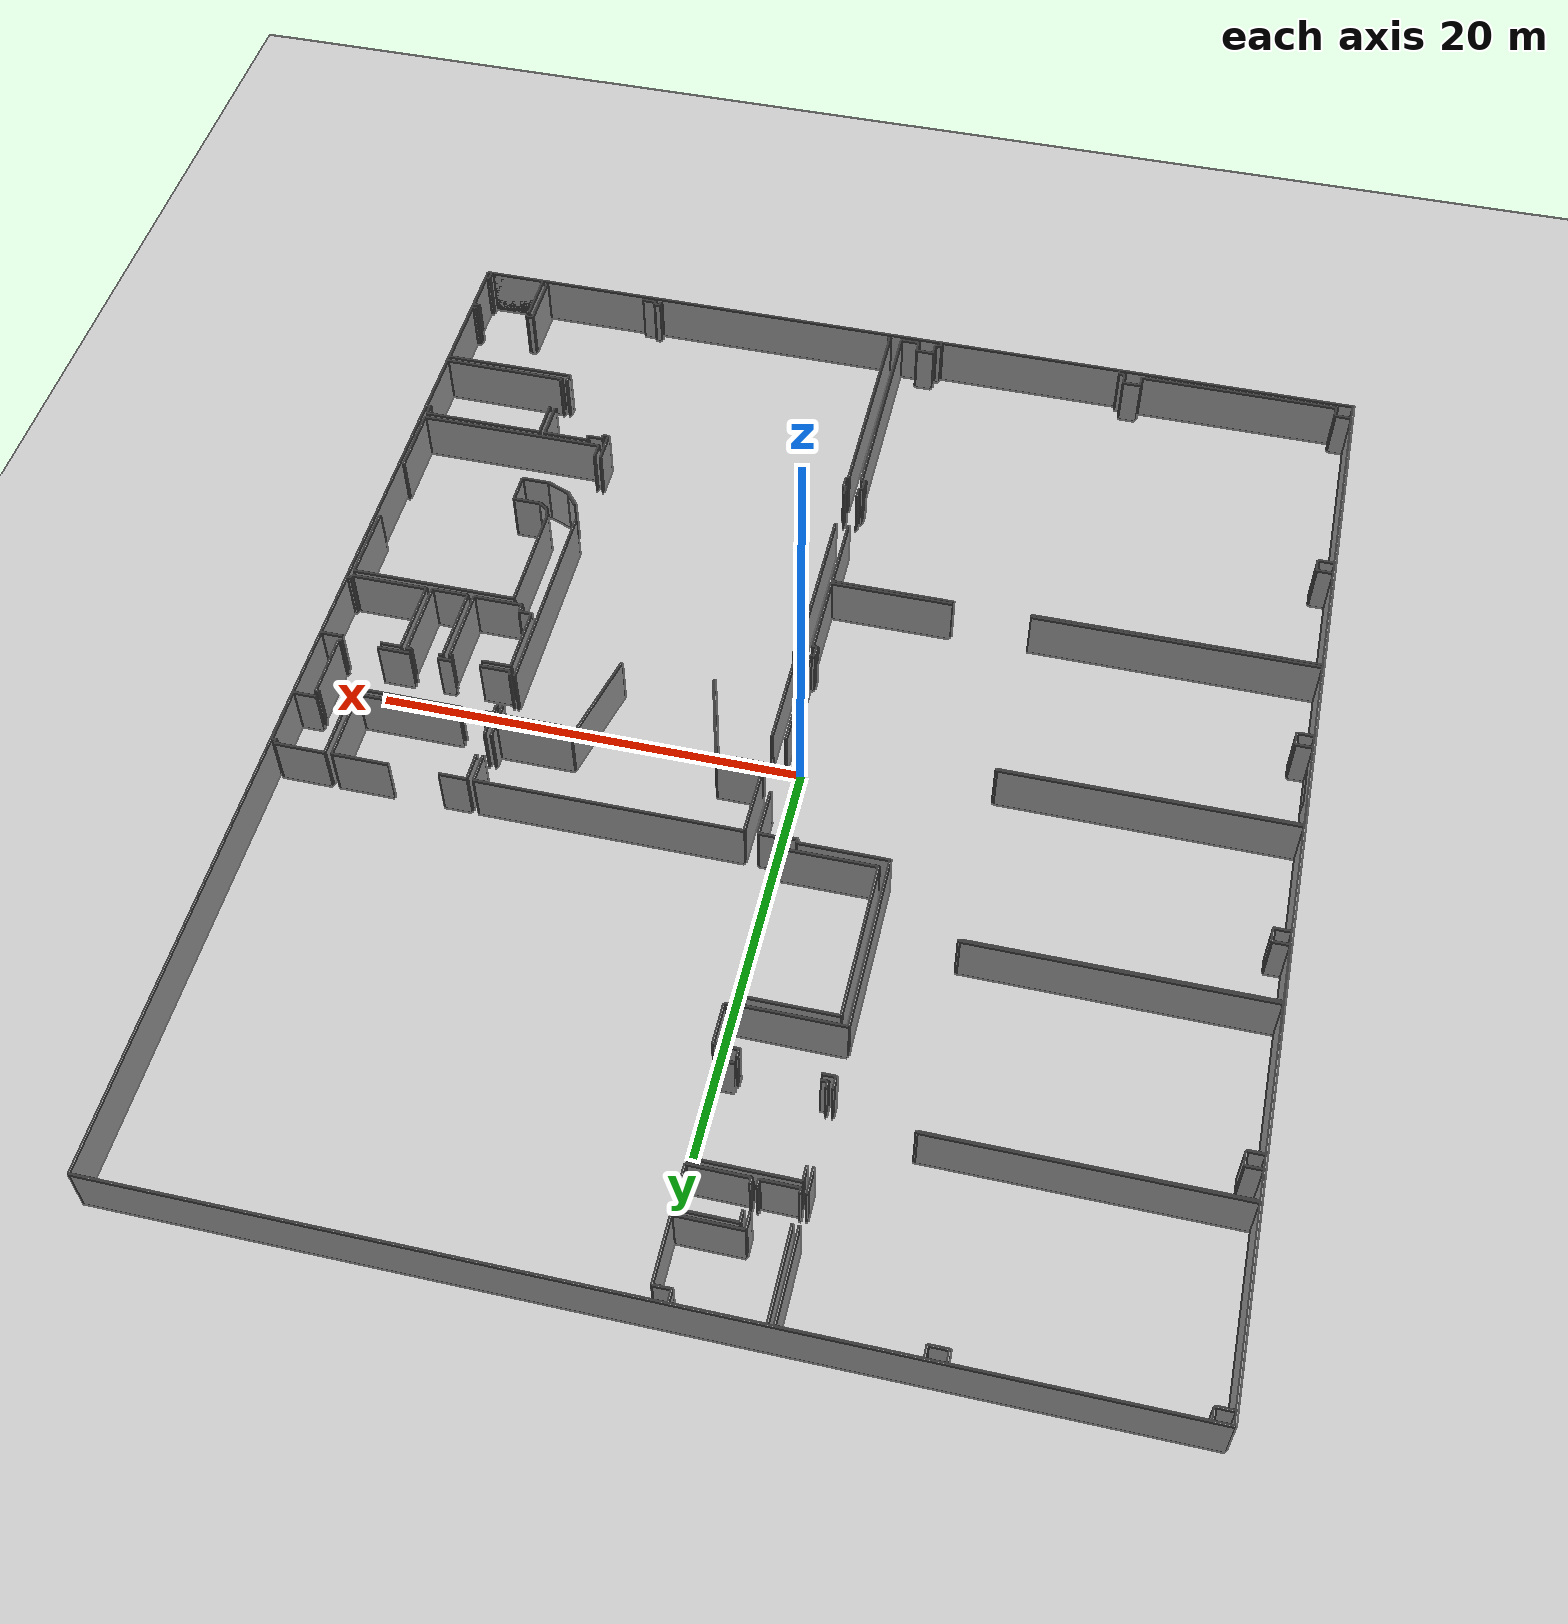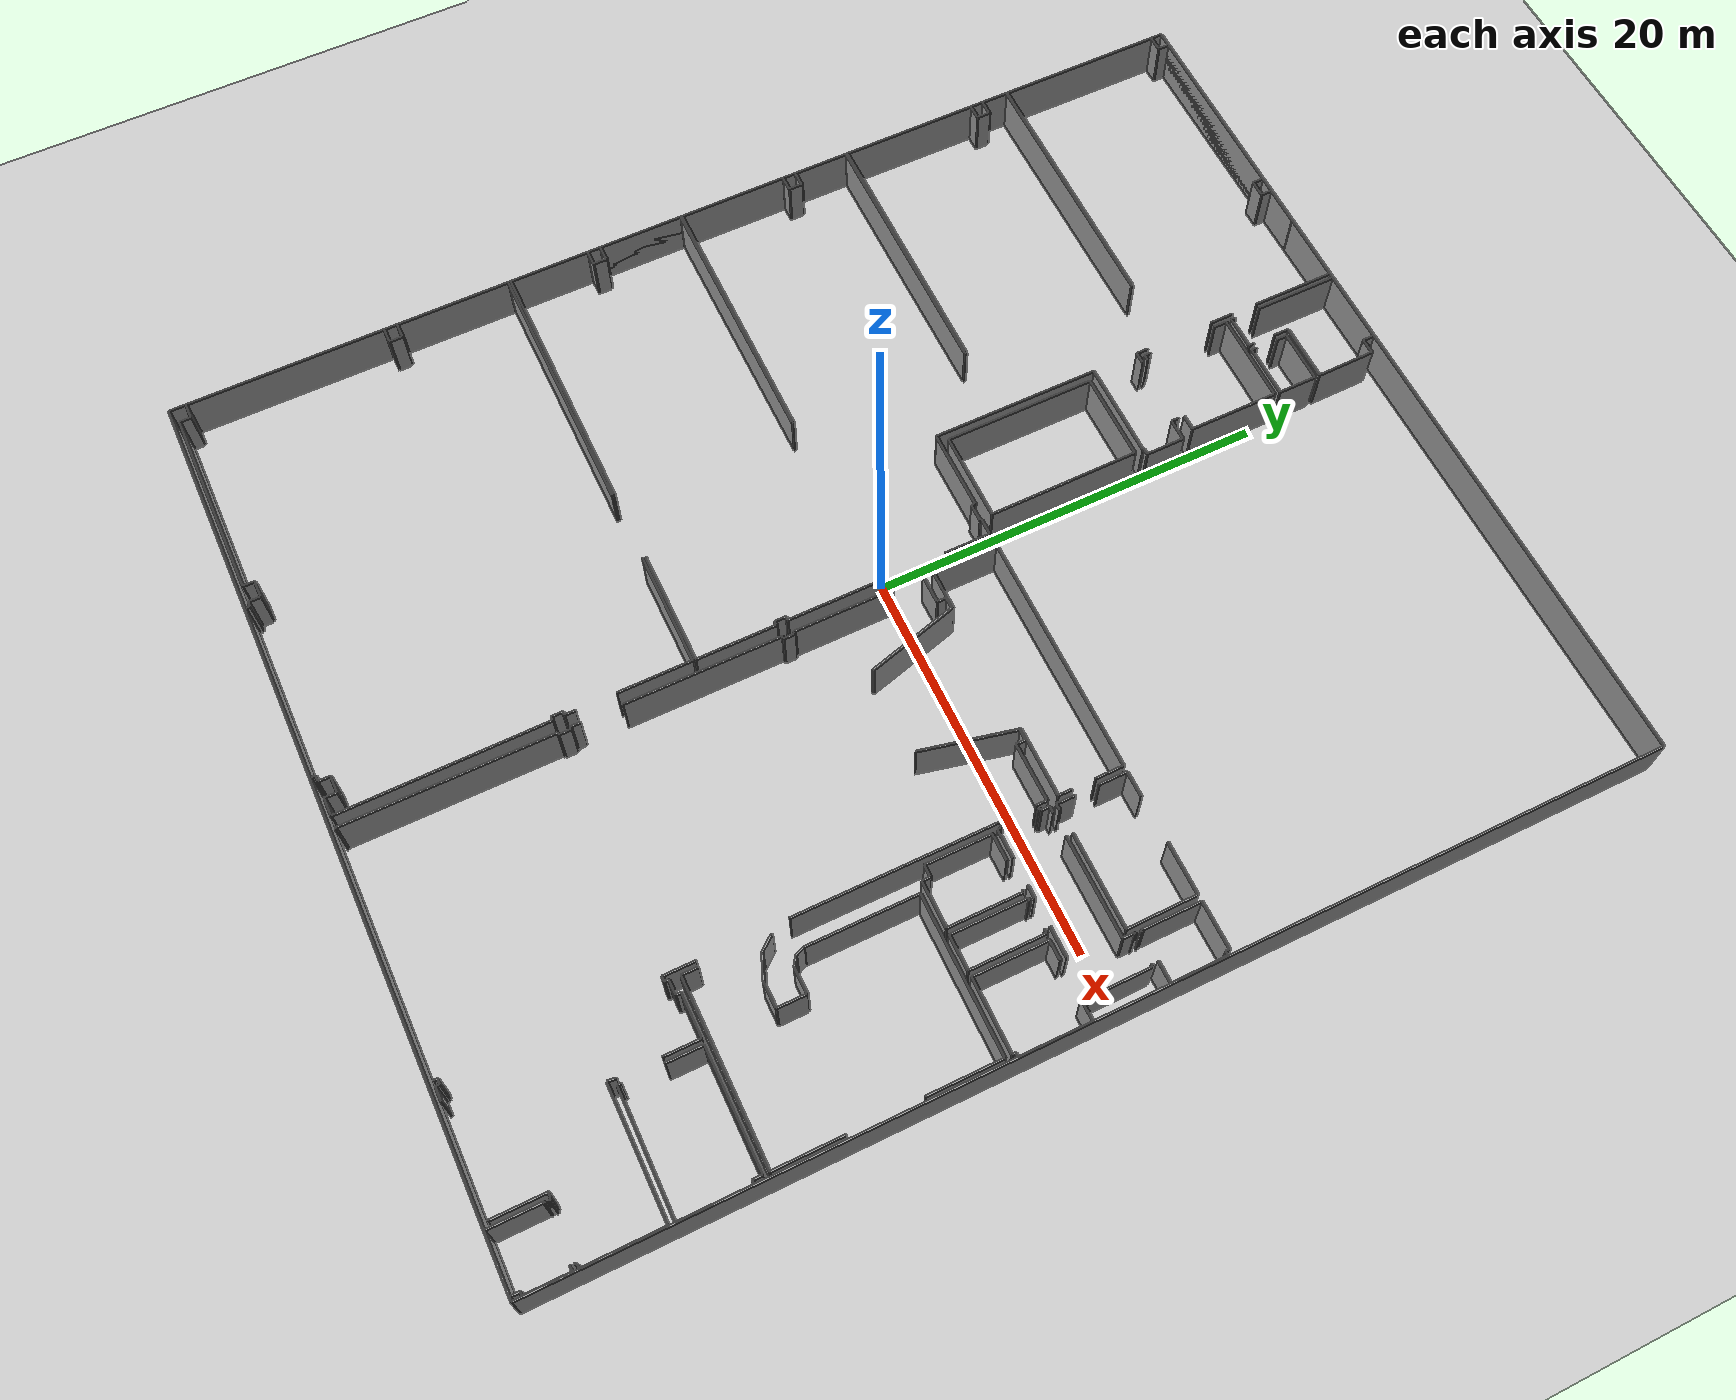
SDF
<sdf version="1.6">
  <world name="default">
    <light name="sun" type="directional">
      <cast_shadows>1</cast_shadows>
      <pose frame="">0 0 10 0 -0 0</pose>
      <diffuse>0.8 0.8 0.8 1</diffuse>
      <specular>0.1 0.1 0.1 1</specular>
      <attenuation>
        <range>1000</range>
        <constant>0.9</constant>
        <linear>0.01</linear>
        <quadratic>0.001</quadratic>
      </attenuation>
      <direction>-0.5 0.5 -1</direction>
    </light>
    <model name="ground_plane">
      <static>1</static>
      <link name="link">
        <collision name="collision">
          <geometry>
            <plane>
              <normal>0 0 1</normal>
              <size>100 100</size>
            </plane>
          </geometry>
          <surface>
            <friction>
              <ode>
                <mu>100</mu>
                <mu2>50</mu2>
              </ode>
              <torsional>
                <ode />
              </torsional>
            </friction>
            <contact>
              <ode />
            </contact>
            <bounce />
          </surface>
          <max_contacts>10</max_contacts>
        </collision>
        <visual name="visual">
          <cast_shadows>0</cast_shadows>
          <geometry>
            <plane>
              <normal>0 0 1</normal>
              <size>100 100</size>
            </plane>
          </geometry>
          <material>
            <script>
              <uri>file://media/materials/scripts/gazebo.material</uri>
              <name>Gazebo/Grey</name>
            </script>
          </material>
        </visual>
        <self_collide>0</self_collide>
        <kinematic>0</kinematic>
        <gravity>1</gravity>
      </link>
    </model>
    <gravity>0 0 -9.8</gravity>
    <magnetic_field>6e-06 2.3e-05 -4.2e-05</magnetic_field>
    <atmosphere type="adiabatic" />
    <physics default="0" name="default_physics" type="ode">
      <max_step_size>0.001</max_step_size>
      <real_time_factor>1</real_time_factor>
      <real_time_update_rate>1000</real_time_update_rate>
    </physics>
    <scene>
      <ambient>0.4 0.4 0.4 1</ambient>
      <background>0.7 0.7 0.7 1</background>
      <shadows>1</shadows>
    </scene>
    <spherical_coordinates>
      <surface_model>EARTH_WGS84</surface_model>
      <latitude_deg>0</latitude_deg>
      <longitude_deg>0</longitude_deg>
      <elevation>0</elevation>
      <heading_deg>0</heading_deg>
    </spherical_coordinates>
  <model name="0510032322">
		<static>1</static>
		<link name="Wall_0">
			<collision name="Wall_0_Collision">
				<geometry>
					<box>
						<size>2.06761739749 0.1 2.5</size>
					</box>
				</geometry>
				<pose frame="">1.03380869874 0 1.25 0 0 0</pose>
			</collision>
			<visual name="Wall_0_Visual">
				<pose frame="">1.03380869874 0 1.25 0 0 0</pose>
				<geometry>
					<box>
						<size>2.06761739749 0.1 2.5</size>
					</box>
				</geometry>
				<material>
					<script>
						<uri>file://media/materials/scripts/gazebo.material</uri>
						<name>Gazebo/Grey</name>
					</script>
					<ambient>1 1 1 1</ambient>
				</material>
			</visual>
			<pose frame="">13.6567595184 -0.00964693487685 0 0 0 3.14159265359</pose>
		</link>
		<link name="Wall_1">
			<collision name="Wall_1_Collision">
				<geometry>
					<box>
						<size>0.5662496906 0.1 2.5</size>
					</box>
				</geometry>
				<pose frame="">0.2831248453 0 1.25 0 0 0</pose>
			</collision>
			<visual name="Wall_1_Visual">
				<pose frame="">0.2831248453 0 1.25 0 0 0</pose>
				<geometry>
					<box>
						<size>0.5662496906 0.1 2.5</size>
					</box>
				</geometry>
				<material>
					<script>
						<uri>file://media/materials/scripts/gazebo.material</uri>
						<name>Gazebo/Grey</name>
					</script>
					<ambient>1 1 1 1</ambient>
				</material>
			</visual>
			<pose frame="">11.5891421209 -0.00964693487685 0 0 0 -1.57079632679</pose>
		</link>
		<link name="Wall_2">
			<collision name="Wall_2_Collision">
				<geometry>
					<box>
						<size>0.859719604222 0.1 2.5</size>
					</box>
				</geometry>
				<pose frame="">0.429859802111 0 1.25 0 0 0</pose>
			</collision>
			<visual name="Wall_2_Visual">
				<pose frame="">0.429859802111 0 1.25 0 0 0</pose>
				<geometry>
					<box>
						<size>0.859719604222 0.1 2.5</size>
					</box>
				</geometry>
				<material>
					<script>
						<uri>file://media/materials/scripts/gazebo.material</uri>
						<name>Gazebo/Grey</name>
					</script>
					<ambient>1 1 1 1</ambient>
				</material>
			</visual>
			<pose frame="">11.5891421209 -0.575896625477 0 0 0 3.14159265359</pose>
		</link>
		<link name="Wall_3">
			<collision name="Wall_3_Collision">
				<geometry>
					<box>
						<size>0.575896625477 0.1 2.5</size>
					</box>
				</geometry>
				<pose frame="">0.287948312738 0 1.25 0 0 0</pose>
			</collision>
			<visual name="Wall_3_Visual">
				<pose frame="">0.287948312738 0 1.25 0 0 0</pose>
				<geometry>
					<box>
						<size>0.575896625477 0.1 2.5</size>
					</box>
				</geometry>
				<material>
					<script>
						<uri>file://media/materials/scripts/gazebo.material</uri>
						<name>Gazebo/Grey</name>
					</script>
					<ambient>1 1 1 1</ambient>
				</material>
			</visual>
			<pose frame="">10.7294225167 -0.575896625477 0 0 0 1.57079632679</pose>
		</link>
		<link name="Wall_4">
			<collision name="Wall_4_Collision">
				<geometry>
					<box>
						<size>9.91514505309 0.1 2.5</size>
					</box>
				</geometry>
				<pose frame="">4.95757252654 0 1.25 0 0 0</pose>
			</collision>
			<visual name="Wall_4_Visual">
				<pose frame="">4.95757252654 0 1.25 0 0 0</pose>
				<geometry>
					<box>
						<size>9.91514505309 0.1 2.5</size>
					</box>
				</geometry>
				<material>
					<script>
						<uri>file://media/materials/scripts/gazebo.material</uri>
						<name>Gazebo/Grey</name>
					</script>
					<ambient>1 1 1 1</ambient>
				</material>
			</visual>
			<pose frame="">10.7294225167 -0.0 0 0 0 3.14159265359</pose>
		</link>
		<link name="Wall_5">
			<collision name="Wall_5_Collision">
				<geometry>
					<box>
						<size>0.592651828158 0.1 2.5</size>
					</box>
				</geometry>
				<pose frame="">0.296325914079 0 1.25 0 0 0</pose>
			</collision>
			<visual name="Wall_5_Visual">
				<pose frame="">0.296325914079 0 1.25 0 0 0</pose>
				<geometry>
					<box>
						<size>0.592651828158 0.1 2.5</size>
					</box>
				</geometry>
				<material>
					<script>
						<uri>file://media/materials/scripts/gazebo.material</uri>
						<name>Gazebo/Grey</name>
					</script>
					<ambient>1 1 1 1</ambient>
				</material>
			</visual>
			<pose frame="">0.814277463618 -0.0 0 0 0 -1.57079632679</pose>
		</link>
		<link name="Wall_6">
			<collision name="Wall_6_Collision">
				<geometry>
					<box>
						<size>0.799680127949 0.1 2.5</size>
					</box>
				</geometry>
				<pose frame="">0.399840063974 0 1.25 0 0 0</pose>
			</collision>
			<visual name="Wall_6_Visual">
				<pose frame="">0.399840063974 0 1.25 0 0 0</pose>
				<geometry>
					<box>
						<size>0.799680127949 0.1 2.5</size>
					</box>
				</geometry>
				<material>
					<script>
						<uri>file://media/materials/scripts/gazebo.material</uri>
						<name>Gazebo/Grey</name>
					</script>
					<ambient>1 1 1 1</ambient>
				</material>
			</visual>
			<pose frame="">0.814277463618 -0.592651828158 0 0 0 3.14159265359</pose>
		</link>
		<link name="Wall_7">
			<collision name="Wall_7_Collision">
				<geometry>
					<box>
						<size>8.6489848505 0.1 2.5</size>
					</box>
				</geometry>
				<pose frame="">4.32449242525 0 1.25 0 0 0</pose>
			</collision>
			<visual name="Wall_7_Visual">
				<pose frame="">4.32449242525 0 1.25 0 0 0</pose>
				<geometry>
					<box>
						<size>8.6489848505 0.1 2.5</size>
					</box>
				</geometry>
				<material>
					<script>
						<uri>file://media/materials/scripts/gazebo.material</uri>
						<name>Gazebo/Grey</name>
					</script>
					<ambient>1 1 1 1</ambient>
				</material>
			</visual>
			<pose frame="">0.0145973356689 -0.592651828158 0 0 0 -1.57079632679</pose>
		</link>
		<link name="Wall_8">
			<collision name="Wall_8_Collision">
				<geometry>
					<box>
						<size>13.6421790487 0.1 2.5</size>
					</box>
				</geometry>
				<pose frame="">6.82108952436 0 1.25 0 0 0</pose>
			</collision>
			<visual name="Wall_8_Visual">
				<pose frame="">6.82108952436 0 1.25 0 0 0</pose>
				<geometry>
					<box>
						<size>13.6421790487 0.1 2.5</size>
					</box>
				</geometry>
				<material>
					<script>
						<uri>file://media/materials/scripts/gazebo.material</uri>
						<name>Gazebo/Grey</name>
					</script>
					<ambient>1 1 1 1</ambient>
				</material>
			</visual>
			<pose frame="">0.0145973356689 -9.24163667866 0 0 0 -0.0015724574153</pose>
		</link>
		<link name="Wall_9">
			<collision name="Wall_9_Collision">
				<geometry>
					<box>
						<size>13.6278187138 0.1 2.5</size>
					</box>
				</geometry>
				<pose frame="">6.81390935689 0 1.25 0 0 0</pose>
			</collision>
			<visual name="Wall_9_Visual">
				<pose frame="">6.81390935689 0 1.25 0 0 0</pose>
				<geometry>
					<box>
						<size>13.6278187138 0.1 2.5</size>
					</box>
				</geometry>
				<material>
					<script>
						<uri>file://media/materials/scripts/gazebo.material</uri>
						<name>Gazebo/Grey</name>
					</script>
					<ambient>1 1 1 1</ambient>
				</material>
			</visual>
			<pose frame="">13.6424160495 -9.29507562055 0 0 0 3.14159265359</pose>
		</link>
		<link name="Wall_10">
			<collision name="Wall_10_Collision">
				<geometry>
					<box>
						<size>1.4079447586 0.1 2.5</size>
					</box>
				</geometry>
				<pose frame="">0.703972379302 0 1.25 0 0 0</pose>
			</collision>
			<visual name="Wall_10_Visual">
				<pose frame="">0.703972379302 0 1.25 0 0 0</pose>
				<geometry>
					<box>
						<size>1.4079447586 0.1 2.5</size>
					</box>
				</geometry>
				<material>
					<script>
						<uri>file://media/materials/scripts/gazebo.material</uri>
						<name>Gazebo/Grey</name>
					</script>
					<ambient>1 1 1 1</ambient>
				</material>
			</visual>
			<pose frame="">0.0145973356689 -9.29507562055 0 0 0 -1.57079632679</pose>
		</link>
		<link name="Wall_11">
			<collision name="Wall_11_Collision">
				<geometry>
					<box>
						<size>0.779116924659 0.1 2.5</size>
					</box>
				</geometry>
				<pose frame="">0.389558462329 0 1.25 0 0 0</pose>
			</collision>
			<visual name="Wall_11_Visual">
				<pose frame="">0.389558462329 0 1.25 0 0 0</pose>
				<geometry>
					<box>
						<size>0.779116924659 0.1 2.5</size>
					</box>
				</geometry>
				<material>
					<script>
						<uri>file://media/materials/scripts/gazebo.material</uri>
						<name>Gazebo/Grey</name>
					</script>
					<ambient>1 1 1 1</ambient>
				</material>
			</visual>
			<pose frame="">0.0145973356689 -10.7030203791 0 0 0 0.0</pose>
		</link>
		<link name="Wall_12">
			<collision name="Wall_12_Collision">
				<geometry>
					<box>
						<size>0.682393709183 0.1 2.5</size>
					</box>
				</geometry>
				<pose frame="">0.341196854591 0 1.25 0 0 0</pose>
			</collision>
			<visual name="Wall_12_Visual">
				<pose frame="">0.341196854591 0 1.25 0 0 0</pose>
				<geometry>
					<box>
						<size>0.682393709183 0.1 2.5</size>
					</box>
				</geometry>
				<material>
					<script>
						<uri>file://media/materials/scripts/gazebo.material</uri>
						<name>Gazebo/Grey</name>
					</script>
					<ambient>1 1 1 1</ambient>
				</material>
			</visual>
			<pose frame="">0.793714260328 -10.7030203791 0 0 0 -1.57079632679</pose>
		</link>
		<link name="Wall_13">
			<collision name="Wall_13_Collision">
				<geometry>
					<box>
						<size>0.782544125207 0.1 2.5</size>
					</box>
				</geometry>
				<pose frame="">0.391272062604 0 1.25 0 0 0</pose>
			</collision>
			<visual name="Wall_13_Visual">
				<pose frame="">0.391272062604 0 1.25 0 0 0</pose>
				<geometry>
					<box>
						<size>0.782544125207 0.1 2.5</size>
					</box>
				</geometry>
				<material>
					<script>
						<uri>file://media/materials/scripts/gazebo.material</uri>
						<name>Gazebo/Grey</name>
					</script>
					<ambient>1 1 1 1</ambient>
				</material>
			</visual>
			<pose frame="">0.793714260328 -11.3854140883 0 0 0 3.14159265359</pose>
		</link>
		<link name="Wall_14">
			<collision name="Wall_14_Collision">
				<geometry>
					<box>
						<size>7.13923954228 0.1 2.5</size>
					</box>
				</geometry>
				<pose frame="">3.56961977114 0 1.25 0 0 0</pose>
			</collision>
			<visual name="Wall_14_Visual">
				<pose frame="">3.56961977114 0 1.25 0 0 0</pose>
				<geometry>
					<box>
						<size>7.13923954228 0.1 2.5</size>
					</box>
				</geometry>
				<material>
					<script>
						<uri>file://media/materials/scripts/gazebo.material</uri>
						<name>Gazebo/Grey</name>
					</script>
					<ambient>1 1 1 1</ambient>
				</material>
			</visual>
			<pose frame="">0.0111701351206 -11.3854140883 0 0 0 -1.57079632679</pose>
		</link>
		<link name="Wall_15">
			<collision name="Wall_15_Collision">
				<geometry>
					<box>
						<size>13.6312729796 0.1 2.5</size>
					</box>
				</geometry>
				<pose frame="">6.81563648982 0 1.25 0 0 0</pose>
			</collision>
			<visual name="Wall_15_Visual">
				<pose frame="">6.81563648982 0 1.25 0 0 0</pose>
				<geometry>
					<box>
						<size>13.6312729796 0.1 2.5</size>
					</box>
				</geometry>
				<material>
					<script>
						<uri>file://media/materials/scripts/gazebo.material</uri>
						<name>Gazebo/Grey</name>
					</script>
					<ambient>1 1 1 1</ambient>
				</material>
			</visual>
			<pose frame="">0.0111701351206 -18.5246536306 0 0 0 -0.00199275267235</pose>
		</link>
		<link name="Wall_16">
			<collision name="Wall_16_Collision">
				<geometry>
					<box>
						<size>13.6482549837 0.1 2.5</size>
					</box>
				</geometry>
				<pose frame="">6.82412749186 0 1.25 0 0 0</pose>
			</collision>
			<visual name="Wall_16_Visual">
				<pose frame="">6.82412749186 0 1.25 0 0 0</pose>
				<geometry>
					<box>
						<size>13.6482549837 0.1 2.5</size>
					</box>
				</geometry>
				<material>
					<script>
						<uri>file://media/materials/scripts/gazebo.material</uri>
						<name>Gazebo/Grey</name>
					</script>
					<ambient>1 1 1 1</ambient>
				</material>
			</visual>
			<pose frame="">13.6576480519 -18.6180765789 0 0 0 3.14159265359</pose>
		</link>
		<link name="Wall_17">
			<collision name="Wall_17_Collision">
				<geometry>
					<box>
						<size>2.87415192653 0.1 2.5</size>
					</box>
				</geometry>
				<pose frame="">1.43707596327 0 1.25 0 0 0</pose>
			</collision>
			<visual name="Wall_17_Visual">
				<pose frame="">1.43707596327 0 1.25 0 0 0</pose>
				<geometry>
					<box>
						<size>2.87415192653 0.1 2.5</size>
					</box>
				</geometry>
				<material>
					<script>
						<uri>file://media/materials/scripts/gazebo.material</uri>
						<name>Gazebo/Grey</name>
					</script>
					<ambient>1 1 1 1</ambient>
				</material>
			</visual>
			<pose frame="">0.00939306816956 -18.6180765789 0 0 0 -1.57079632679</pose>
		</link>
		<link name="Wall_18">
			<collision name="Wall_18_Collision">
				<geometry>
					<box>
						<size>0.779624658073 0.1 2.5</size>
					</box>
				</geometry>
				<pose frame="">0.389812329037 0 1.25 0 0 0</pose>
			</collision>
			<visual name="Wall_18_Visual">
				<pose frame="">0.389812329037 0 1.25 0 0 0</pose>
				<geometry>
					<box>
						<size>0.779624658073 0.1 2.5</size>
					</box>
				</geometry>
				<material>
					<script>
						<uri>file://media/materials/scripts/gazebo.material</uri>
						<name>Gazebo/Grey</name>
					</script>
					<ambient>1 1 1 1</ambient>
				</material>
			</visual>
			<pose frame="">0.00939306816956 -21.4922285054 0 0 0 0.0</pose>
		</link>
		<link name="Wall_19">
			<collision name="Wall_19_Collision">
				<geometry>
					<box>
						<size>0.691913710706 0.1 2.5</size>
					</box>
				</geometry>
				<pose frame="">0.345956855353 0 1.25 0 0 0</pose>
			</collision>
			<visual name="Wall_19_Visual">
				<pose frame="">0.345956855353 0 1.25 0 0 0</pose>
				<geometry>
					<box>
						<size>0.691913710706 0.1 2.5</size>
					</box>
				</geometry>
				<material>
					<script>
						<uri>file://media/materials/scripts/gazebo.material</uri>
						<name>Gazebo/Grey</name>
					</script>
					<ambient>1 1 1 1</ambient>
				</material>
			</visual>
			<pose frame="">0.789017726243 -21.4922285054 0 0 0 -1.57079632679</pose>
		</link>
		<link name="Wall_20">
			<collision name="Wall_20_Collision">
				<geometry>
					<box>
						<size>0.782671058561 0.1 2.5</size>
					</box>
				</geometry>
				<pose frame="">0.39133552928 0 1.25 0 0 0</pose>
			</collision>
			<visual name="Wall_20_Visual">
				<pose frame="">0.39133552928 0 1.25 0 0 0</pose>
				<geometry>
					<box>
						<size>0.782671058561 0.1 2.5</size>
					</box>
				</geometry>
				<material>
					<script>
						<uri>file://media/materials/scripts/gazebo.material</uri>
						<name>Gazebo/Grey</name>
					</script>
					<ambient>1 1 1 1</ambient>
				</material>
			</visual>
			<pose frame="">0.789017726243 -22.1841422161 0 0 0 3.14159265359</pose>
		</link>
		<link name="Wall_21">
			<collision name="Wall_21_Collision">
				<geometry>
					<box>
						<size>5.64041050247 0.1 2.5</size>
					</box>
				</geometry>
				<pose frame="">2.82020525123 0 1.25 0 0 0</pose>
			</collision>
			<visual name="Wall_21_Visual">
				<pose frame="">2.82020525123 0 1.25 0 0 0</pose>
				<geometry>
					<box>
						<size>5.64041050247 0.1 2.5</size>
					</box>
				</geometry>
				<material>
					<script>
						<uri>file://media/materials/scripts/gazebo.material</uri>
						<name>Gazebo/Grey</name>
					</script>
					<ambient>1 1 1 1</ambient>
				</material>
			</visual>
			<pose frame="">0.00634666768213 -22.1841422161 0 0 0 -1.57079632679</pose>
		</link>
		<link name="Wall_22">
			<collision name="Wall_22_Collision">
				<geometry>
					<box>
						<size>13.6513412769 0.1 2.5</size>
					</box>
				</geometry>
				<pose frame="">6.82567063846 0 1.25 0 0 0</pose>
			</collision>
			<visual name="Wall_22_Visual">
				<pose frame="">6.82567063846 0 1.25 0 0 0</pose>
				<geometry>
					<box>
						<size>13.6513412769 0.1 2.5</size>
					</box>
				</geometry>
				<material>
					<script>
						<uri>file://media/materials/scripts/gazebo.material</uri>
						<name>Gazebo/Grey</name>
					</script>
					<ambient>1 1 1 1</ambient>
				</material>
			</visual>
			<pose frame="">0.00634666768213 -27.8245527186 0 0 0 -0.00241754296703</pose>
		</link>
		<link name="Wall_23">
			<collision name="Wall_23_Collision">
				<geometry>
					<box>
						<size>13.6599328523 0.1 2.5</size>
					</box>
				</geometry>
				<pose frame="">6.82996642613 0 1.25 0 0 0</pose>
			</collision>
			<visual name="Wall_23_Visual">
				<pose frame="">6.82996642613 0 1.25 0 0 0</pose>
				<geometry>
					<box>
						<size>13.6599328523 0.1 2.5</size>
					</box>
				</geometry>
				<material>
					<script>
						<uri>file://media/materials/scripts/gazebo.material</uri>
						<name>Gazebo/Grey</name>
					</script>
					<ambient>1 1 1 1</ambient>
				</material>
			</visual>
			<pose frame="">13.6599328523 -27.9007127308 0 0 0 3.14159265359</pose>
		</link>
		<link name="Wall_24">
			<collision name="Wall_24_Collision">
				<geometry>
					<box>
						<size>4.39862150378 0.1 2.5</size>
					</box>
				</geometry>
				<pose frame="">2.19931075189 0 1.25 0 0 0</pose>
			</collision>
			<visual name="Wall_24_Visual">
				<pose frame="">2.19931075189 0 1.25 0 0 0</pose>
				<geometry>
					<box>
						<size>4.39862150378 0.1 2.5</size>
					</box>
				</geometry>
				<material>
					<script>
						<uri>file://media/materials/scripts/gazebo.material</uri>
						<name>Gazebo/Grey</name>
					</script>
					<ambient>1 1 1 1</ambient>
				</material>
			</visual>
			<pose frame="">0.0 -27.9007127308 0 0 0 -1.57079632679</pose>
		</link>
		<link name="Wall_25">
			<collision name="Wall_25_Collision">
				<geometry>
					<box>
						<size>0.806026795631 0.1 2.5</size>
					</box>
				</geometry>
				<pose frame="">0.403013397815 0 1.25 0 0 0</pose>
			</collision>
			<visual name="Wall_25_Visual">
				<pose frame="">0.403013397815 0 1.25 0 0 0</pose>
				<geometry>
					<box>
						<size>0.806026795631 0.1 2.5</size>
					</box>
				</geometry>
				<material>
					<script>
						<uri>file://media/materials/scripts/gazebo.material</uri>
						<name>Gazebo/Grey</name>
					</script>
					<ambient>1 1 1 1</ambient>
				</material>
			</visual>
			<pose frame="">0.0 -32.2993342346 0 0 0 0.0</pose>
		</link>
		<link name="Wall_26">
			<collision name="Wall_26_Collision">
				<geometry>
					<box>
						<size>0.684424642841 0.1 2.5</size>
					</box>
				</geometry>
				<pose frame="">0.342212321421 0 1.25 0 0 0</pose>
			</collision>
			<visual name="Wall_26_Visual">
				<pose frame="">0.342212321421 0 1.25 0 0 0</pose>
				<geometry>
					<box>
						<size>0.684424642841 0.1 2.5</size>
					</box>
				</geometry>
				<material>
					<script>
						<uri>file://media/materials/scripts/gazebo.material</uri>
						<name>Gazebo/Grey</name>
					</script>
					<ambient>1 1 1 1</ambient>
				</material>
			</visual>
			<pose frame="">0.806026795631 -32.2993342346 0 0 0 -1.57079632679</pose>
		</link>
		<link name="Wall_27">
			<collision name="Wall_27_Collision">
				<geometry>
					<box>
						<size>0.801330261546 0.1 2.5</size>
					</box>
				</geometry>
				<pose frame="">0.400665130773 0 1.25 0 0 0</pose>
			</collision>
			<visual name="Wall_27_Visual">
				<pose frame="">0.400665130773 0 1.25 0 0 0</pose>
				<geometry>
					<box>
						<size>0.801330261546 0.1 2.5</size>
					</box>
				</geometry>
				<material>
					<script>
						<uri>file://media/materials/scripts/gazebo.material</uri>
						<name>Gazebo/Grey</name>
					</script>
					<ambient>1 1 1 1</ambient>
				</material>
			</visual>
			<pose frame="">0.806026795631 -32.9837588774 0 0 0 3.14159265359</pose>
		</link>
		<link name="Wall_28">
			<collision name="Wall_28_Collision">
				<geometry>
					<box>
						<size>4.13701186192 0.1 2.5</size>
					</box>
				</geometry>
				<pose frame="">2.06850593096 0 1.25 0 0 0</pose>
			</collision>
			<visual name="Wall_28_Visual">
				<pose frame="">2.06850593096 0 1.25 0 0 0</pose>
				<geometry>
					<box>
						<size>4.13701186192 0.1 2.5</size>
					</box>
				</geometry>
				<material>
					<script>
						<uri>file://media/materials/scripts/gazebo.material</uri>
						<name>Gazebo/Grey</name>
					</script>
					<ambient>1 1 1 1</ambient>
				</material>
			</visual>
			<pose frame="">0.00469653408478 -32.9837588774 0 0 0 -1.57079632679</pose>
		</link>
		<link name="Wall_29">
			<collision name="Wall_29_Collision">
				<geometry>
					<box>
						<size>13.6552683465 0.1 2.5</size>
					</box>
				</geometry>
				<pose frame="">6.82763417323 0 1.25 0 0 0</pose>
			</collision>
			<visual name="Wall_29_Visual">
				<pose frame="">6.82763417323 0 1.25 0 0 0</pose>
				<geometry>
					<box>
						<size>13.6552683465 0.1 2.5</size>
					</box>
				</geometry>
				<material>
					<script>
						<uri>file://media/materials/scripts/gazebo.material</uri>
						<name>Gazebo/Grey</name>
					</script>
					<ambient>1 1 1 1</ambient>
				</material>
			</visual>
			<pose frame="">0.00469653408478 -37.1207707393 0 0 0 -0.00216586695855</pose>
		</link>
		<link name="Wall_30">
			<collision name="Wall_30_Collision">
				<geometry>
					<box>
						<size>0.938164416773 0.1 2.5</size>
					</box>
				</geometry>
				<pose frame="">0.469082208386 0 1.25 0 0 0</pose>
			</collision>
			<visual name="Wall_30_Visual">
				<pose frame="">0.469082208386 0 1.25 0 0 0</pose>
				<geometry>
					<box>
						<size>0.938164416773 0.1 2.5</size>
					</box>
				</geometry>
				<material>
					<script>
						<uri>file://media/materials/scripts/gazebo.material</uri>
						<name>Gazebo/Grey</name>
					</script>
					<ambient>1 1 1 1</ambient>
				</material>
			</visual>
			<pose frame="">23.3180378642 -54.5016279203 0 0 0 3.14159265359</pose>
		</link>
		<link name="Wall_31">
			<collision name="Wall_31_Collision">
				<geometry>
					<box>
						<size>0.594301961755 0.1 2.5</size>
					</box>
				</geometry>
				<pose frame="">0.297150980877 0 1.25 0 0 0</pose>
			</collision>
			<visual name="Wall_31_Visual">
				<pose frame="">0.297150980877 0 1.25 0 0 0</pose>
				<geometry>
					<box>
						<size>0.594301961755 0.1 2.5</size>
					</box>
				</geometry>
				<material>
					<script>
						<uri>file://media/materials/scripts/gazebo.material</uri>
						<name>Gazebo/Grey</name>
					</script>
					<ambient>1 1 1 1</ambient>
				</material>
			</visual>
			<pose frame="">22.3798734474 -54.5016279203 0 0 0 1.57079632679</pose>
		</link>
		<link name="Wall_32">
			<collision name="Wall_32_Collision">
				<geometry>
					<box>
						<size>0.86733560544 0.1 2.5</size>
					</box>
				</geometry>
				<pose frame="">0.43366780272 0 1.25 0 0 0</pose>
			</collision>
			<visual name="Wall_32_Visual">
				<pose frame="">0.43366780272 0 1.25 0 0 0</pose>
				<geometry>
					<box>
						<size>0.86733560544 0.1 2.5</size>
					</box>
				</geometry>
				<material>
					<script>
						<uri>file://media/materials/scripts/gazebo.material</uri>
						<name>Gazebo/Grey</name>
					</script>
					<ambient>1 1 1 1</ambient>
				</material>
			</visual>
			<pose frame="">22.3798734474 -53.9073259585 0 0 0 3.14159265359</pose>
		</link>
		<link name="Wall_33">
			<collision name="Wall_33_Collision">
				<geometry>
					<box>
						<size>0.592651828158 0.1 2.5</size>
					</box>
				</geometry>
				<pose frame="">0.296325914079 0 1.25 0 0 0</pose>
			</collision>
			<visual name="Wall_33_Visual">
				<pose frame="">0.296325914079 0 1.25 0 0 0</pose>
				<geometry>
					<box>
						<size>0.592651828158 0.1 2.5</size>
					</box>
				</geometry>
				<material>
					<script>
						<uri>file://media/materials/scripts/gazebo.material</uri>
						<name>Gazebo/Grey</name>
					</script>
					<ambient>1 1 1 1</ambient>
				</material>
			</visual>
			<pose frame="">21.512537842 -53.9073259585 0 0 0 -1.57079632679</pose>
		</link>
		<link name="Wall_34">
			<collision name="Wall_34_Collision">
				<geometry>
					<box>
						<size>0.291692846671 0.1 2.5</size>
					</box>
				</geometry>
				<pose frame="">0.145846423335 0 1.25 0 0 0</pose>
			</collision>
			<visual name="Wall_34_Visual">
				<pose frame="">0.145846423335 0 1.25 0 0 0</pose>
				<geometry>
					<box>
						<size>0.291692846671 0.1 2.5</size>
					</box>
				</geometry>
				<material>
					<script>
						<uri>file://media/materials/scripts/gazebo.material</uri>
						<name>Gazebo/Grey</name>
					</script>
					<ambient>1 1 1 1</ambient>
				</material>
			</visual>
			<pose frame="">21.512537842 -54.4999777867 0 0 0 3.14159265359</pose>
		</link>
		<link name="Wall_35">
			<collision name="Wall_35_Collision">
				<geometry>
					<box>
						<size>0.195223497902 0.1 2.5</size>
					</box>
				</geometry>
				<pose frame="">0.0976117489512 0 1.25 0 0 0</pose>
			</collision>
			<visual name="Wall_35_Visual">
				<pose frame="">0.0976117489512 0 1.25 0 0 0</pose>
				<geometry>
					<box>
						<size>0.195223497902 0.1 2.5</size>
					</box>
				</geometry>
				<material>
					<script>
						<uri>file://media/materials/scripts/gazebo.material</uri>
						<name>Gazebo/Grey</name>
					</script>
					<ambient>1 1 1 1</ambient>
				</material>
			</visual>
			<pose frame="">21.2208449953 -54.4999777867 0 0 0 -1.57079632679</pose>
		</link>
		<link name="Wall_36">
			<collision name="Wall_36_Collision">
				<geometry>
					<box>
						<size>0.190907763879 0.1 2.5</size>
					</box>
				</geometry>
				<pose frame="">0.0954538819393 0 1.25 0 0 0</pose>
			</collision>
			<visual name="Wall_36_Visual">
				<pose frame="">0.0954538819393 0 1.25 0 0 0</pose>
				<geometry>
					<box>
						<size>0.190907763879 0.1 2.5</size>
					</box>
				</geometry>
				<material>
					<script>
						<uri>file://media/materials/scripts/gazebo.material</uri>
						<name>Gazebo/Grey</name>
					</script>
					<ambient>1 1 1 1</ambient>
				</material>
			</visual>
			<pose frame="">11.9015251042 -54.6952012846 0 0 0 1.57079632679</pose>
		</link>
		<link name="Wall_37">
			<collision name="Wall_37_Collision">
				<geometry>
					<box>
						<size>0.286361645818 0.1 2.5</size>
					</box>
				</geometry>
				<pose frame="">0.143180822909 0 1.25 0 0 0</pose>
			</collision>
			<visual name="Wall_37_Visual">
				<pose frame="">0.143180822909 0 1.25 0 0 0</pose>
				<geometry>
					<box>
						<size>0.286361645818 0.1 2.5</size>
					</box>
				</geometry>
				<material>
					<script>
						<uri>file://media/materials/scripts/gazebo.material</uri>
						<name>Gazebo/Grey</name>
					</script>
					<ambient>1 1 1 1</ambient>
				</material>
			</visual>
			<pose frame="">11.9015251042 -54.5042935207 0 0 0 3.14159265359</pose>
		</link>
		<link name="Wall_38">
			<collision name="Wall_38_Collision">
				<geometry>
					<box>
						<size>0.59760222895 0.1 2.5</size>
					</box>
				</geometry>
				<pose frame="">0.298801114475 0 1.25 0 0 0</pose>
			</collision>
			<visual name="Wall_38_Visual">
				<pose frame="">0.298801114475 0 1.25 0 0 0</pose>
				<geometry>
					<box>
						<size>0.59760222895 0.1 2.5</size>
					</box>
				</geometry>
				<material>
					<script>
						<uri>file://media/materials/scripts/gazebo.material</uri>
						<name>Gazebo/Grey</name>
					</script>
					<ambient>1 1 1 1</ambient>
				</material>
			</visual>
			<pose frame="">11.6151634584 -54.5042935207 0 0 0 1.57079632679</pose>
		</link>
		<link name="Wall_39">
			<collision name="Wall_39_Collision">
				<geometry>
					<box>
						<size>0.888025742084 0.1 2.5</size>
					</box>
				</geometry>
				<pose frame="">0.444012871042 0 1.25 0 0 0</pose>
			</collision>
			<visual name="Wall_39_Visual">
				<pose frame="">0.444012871042 0 1.25 0 0 0</pose>
				<geometry>
					<box>
						<size>0.888025742084 0.1 2.5</size>
					</box>
				</geometry>
				<material>
					<script>
						<uri>file://media/materials/scripts/gazebo.material</uri>
						<name>Gazebo/Grey</name>
					</script>
					<ambient>1 1 1 1</ambient>
				</material>
			</visual>
			<pose frame="">11.6151634584 -53.9066912917 0 0 0 3.14159265359</pose>
		</link>
		<link name="Wall_40">
			<collision name="Wall_40_Collision">
				<geometry>
					<box>
						<size>0.580973959622 0.1 2.5</size>
					</box>
				</geometry>
				<pose frame="">0.290486979811 0 1.25 0 0 0</pose>
			</collision>
			<visual name="Wall_40_Visual">
				<pose frame="">0.290486979811 0 1.25 0 0 0</pose>
				<geometry>
					<box>
						<size>0.580973959622 0.1 2.5</size>
					</box>
				</geometry>
				<material>
					<script>
						<uri>file://media/materials/scripts/gazebo.material</uri>
						<name>Gazebo/Grey</name>
					</script>
					<ambient>1 1 1 1</ambient>
				</material>
			</visual>
			<pose frame="">10.7271377163 -53.9066912917 0 0 0 -1.57079632679</pose>
		</link>
		<link name="Wall_41">
			<collision name="Wall_41_Collision">
				<geometry>
					<box>
						<size>9.91362185285 0.1 2.5</size>
					</box>
				</geometry>
				<pose frame="">4.95681092642 0 1.25 0 0 0</pose>
			</collision>
			<visual name="Wall_41_Visual">
				<pose frame="">4.95681092642 0 1.25 0 0 0</pose>
				<geometry>
					<box>
						<size>9.91362185285 0.1 2.5</size>
					</box>
				</geometry>
				<material>
					<script>
						<uri>file://media/materials/scripts/gazebo.material</uri>
						<name>Gazebo/Grey</name>
					</script>
					<ambient>1 1 1 1</ambient>
				</material>
			</visual>
			<pose frame="">10.7271377163 -54.4876652514 0 0 0 3.14159265359</pose>
		</link>
		<link name="Wall_42">
			<collision name="Wall_42_Collision">
				<geometry>
					<box>
						<size>0.579450759379 0.1 2.5</size>
					</box>
				</geometry>
				<pose frame="">0.289725379689 0 1.25 0 0 0</pose>
			</collision>
			<visual name="Wall_42_Visual">
				<pose frame="">0.289725379689 0 1.25 0 0 0</pose>
				<geometry>
					<box>
						<size>0.579450759379 0.1 2.5</size>
					</box>
				</geometry>
				<material>
					<script>
						<uri>file://media/materials/scripts/gazebo.material</uri>
						<name>Gazebo/Grey</name>
					</script>
					<ambient>1 1 1 1</ambient>
				</material>
			</visual>
			<pose frame="">0.813515863496 -54.4876652514 0 0 0 1.57079632679</pose>
		</link>
		<link name="Wall_43">
			<collision name="Wall_43_Collision">
				<geometry>
					<box>
						<size>0.800949461485 0.1 2.5</size>
					</box>
				</geometry>
				<pose frame="">0.400474730743 0 1.25 0 0 0</pose>
			</collision>
			<visual name="Wall_43_Visual">
				<pose frame="">0.400474730743 0 1.25 0 0 0</pose>
				<geometry>
					<box>
						<size>0.800949461485 0.1 2.5</size>
					</box>
				</geometry>
				<material>
					<script>
						<uri>file://media/materials/scripts/gazebo.material</uri>
						<name>Gazebo/Grey</name>
					</script>
					<ambient>1 1 1 1</ambient>
				</material>
			</visual>
			<pose frame="">0.813515863496 -53.908214492 0 0 0 3.14159265359</pose>
		</link>
		<link name="Wall_44">
			<collision name="Wall_44_Collision">
				<geometry>
					<box>
						<size>10.1210309527 0.1 2.5</size>
					</box>
				</geometry>
				<pose frame="">5.06051547635 0 1.25 0 0 0</pose>
			</collision>
			<visual name="Wall_44_Visual">
				<pose frame="">5.06051547635 0 1.25 0 0 0</pose>
				<geometry>
					<box>
						<size>10.1210309527 0.1 2.5</size>
					</box>
				</geometry>
				<material>
					<script>
						<uri>file://media/materials/scripts/gazebo.material</uri>
						<name>Gazebo/Grey</name>
					</script>
					<ambient>1 1 1 1</ambient>
				</material>
			</visual>
			<pose frame="">0.0125664020106 -53.908214492 0 0 0 1.57079632679</pose>
		</link>
		<link name="Wall_45">
			<collision name="Wall_45_Collision">
				<geometry>
					<box>
						<size>0.793079593559 0.1 2.5</size>
					</box>
				</geometry>
				<pose frame="">0.39653979678 0 1.25 0 0 0</pose>
			</collision>
			<visual name="Wall_45_Visual">
				<pose frame="">0.39653979678 0 1.25 0 0 0</pose>
				<geometry>
					<box>
						<size>0.793079593559 0.1 2.5</size>
					</box>
				</geometry>
				<material>
					<script>
						<uri>file://media/materials/scripts/gazebo.material</uri>
						<name>Gazebo/Grey</name>
					</script>
					<ambient>1 1 1 1</ambient>
				</material>
			</visual>
			<pose frame="">0.0125664020106 -43.7871835393 0 0 0 0.0</pose>
		</link>
		<link name="Wall_46">
			<collision name="Wall_46_Collision">
				<geometry>
					<box>
						<size>0.674904641318 0.1 2.5</size>
					</box>
				</geometry>
				<pose frame="">0.337452320659 0 1.25 0 0 0</pose>
			</collision>
			<visual name="Wall_46_Visual">
				<pose frame="">0.337452320659 0 1.25 0 0 0</pose>
				<geometry>
					<box>
						<size>0.674904641318 0.1 2.5</size>
					</box>
				</geometry>
				<material>
					<script>
						<uri>file://media/materials/scripts/gazebo.material</uri>
						<name>Gazebo/Grey</name>
					</script>
					<ambient>1 1 1 1</ambient>
				</material>
			</visual>
			<pose frame="">0.80564599557 -43.7871835393 0 0 0 1.57079632679</pose>
		</link>
		<link name="Wall_47">
			<collision name="Wall_47_Collision">
				<geometry>
					<box>
						<size>0.791048659901 0.1 2.5</size>
					</box>
				</geometry>
				<pose frame="">0.395524329951 0 1.25 0 0 0</pose>
			</collision>
			<visual name="Wall_47_Visual">
				<pose frame="">0.395524329951 0 1.25 0 0 0</pose>
				<geometry>
					<box>
						<size>0.791048659901 0.1 2.5</size>
					</box>
				</geometry>
				<material>
					<script>
						<uri>file://media/materials/scripts/gazebo.material</uri>
						<name>Gazebo/Grey</name>
					</script>
					<ambient>1 1 1 1</ambient>
				</material>
			</visual>
			<pose frame="">0.80564599557 -43.112278898 0 0 0 3.14159265359</pose>
		</link>
		<link name="Wall_48">
			<collision name="Wall_48_Collision">
				<geometry>
					<box>
						<size>5.85822813732 0.1 2.5</size>
					</box>
				</geometry>
				<pose frame="">2.92911406866 0 1.25 0 0 0</pose>
			</collision>
			<visual name="Wall_48_Visual">
				<pose frame="">2.92911406866 0 1.25 0 0 0</pose>
				<geometry>
					<box>
						<size>5.85822813732 0.1 2.5</size>
					</box>
				</geometry>
				<material>
					<script>
						<uri>file://media/materials/scripts/gazebo.material</uri>
						<name>Gazebo/Grey</name>
					</script>
					<ambient>1 1 1 1</ambient>
				</material>
			</visual>
			<pose frame="">0.0145973356689 -43.112278898 0 0 0 1.57079632679</pose>
		</link>
		<link name="Wall_49">
			<collision name="Wall_49_Collision">
				<geometry>
					<box>
						<size>13.6468587168 0.1 2.5</size>
					</box>
				</geometry>
				<pose frame="">6.82342935842 0 1.25 0 0 0</pose>
			</collision>
			<visual name="Wall_49_Visual">
				<pose frame="">6.82342935842 0 1.25 0 0 0</pose>
				<geometry>
					<box>
						<size>13.6468587168 0.1 2.5</size>
					</box>
				</geometry>
				<material>
					<script>
						<uri>file://media/materials/scripts/gazebo.material</uri>
						<name>Gazebo/Grey</name>
					</script>
					<ambient>1 1 1 1</ambient>
				</material>
			</visual>
			<pose frame="">0.0145973356689 -37.2540507606 0 0 0 0.0</pose>
		</link>
		<link name="Wall_50">
			<collision name="Wall_50_Collision">
				<geometry>
					<box>
						<size>5.89922761054 0.1 2.5</size>
					</box>
				</geometry>
				<pose frame="">2.94961380527 0 1.25 0 0 0</pose>
			</collision>
			<visual name="Wall_50_Visual">
				<pose frame="">2.94961380527 0 1.25 0 0 0</pose>
				<geometry>
					<box>
						<size>5.89922761054 0.1 2.5</size>
					</box>
				</geometry>
				<material>
					<script>
						<uri>file://media/materials/scripts/gazebo.material</uri>
						<name>Gazebo/Grey</name>
					</script>
					<ambient>1 1 1 1</ambient>
				</material>
			</visual>
			<pose frame="">17.3469659755 -37.2540507606 0 0 0 0.0</pose>
		</link>
		<link name="Wall_51">
			<collision name="Wall_51_Collision">
				<geometry>
					<box>
						<size>3.73907579825 0.1 2.5</size>
					</box>
				</geometry>
				<pose frame="">1.86953789913 0 1.25 0 0 0</pose>
			</collision>
			<visual name="Wall_51_Visual">
				<pose frame="">1.86953789913 0 1.25 0 0 0</pose>
				<geometry>
					<box>
						<size>3.73907579825 0.1 2.5</size>
					</box>
				</geometry>
				<material>
					<script>
						<uri>file://media/materials/scripts/gazebo.material</uri>
						<name>Gazebo/Grey</name>
					</script>
					<ambient>1 1 1 1</ambient>
				</material>
			</visual>
			<pose frame="">23.2461935861 -37.2540507606 0 0 0 -1.57079632679</pose>
		</link>
		<link name="Wall_52">
			<collision name="Wall_52_Collision">
				<geometry>
					<box>
						<size>0.529692884751 0.1 2.5</size>
					</box>
				</geometry>
				<pose frame="">0.264846442375 0 1.25 0 0 0</pose>
			</collision>
			<visual name="Wall_52_Visual">
				<pose frame="">0.264846442375 0 1.25 0 0 0</pose>
				<geometry>
					<box>
						<size>0.529692884751 0.1 2.5</size>
					</box>
				</geometry>
				<material>
					<script>
						<uri>file://media/materials/scripts/gazebo.material</uri>
						<name>Gazebo/Grey</name>
					</script>
					<ambient>1 1 1 1</ambient>
				</material>
			</visual>
			<pose frame="">23.2461935861 -42.9816644771 0 0 0 -1.57079632679</pose>
		</link>
		<link name="Wall_53">
			<collision name="Wall_53_Collision">
				<geometry>
					<box>
						<size>0.182022429124 0.1 2.5</size>
					</box>
				</geometry>
				<pose frame="">0.0910112145618 0 1.25 0 0 0</pose>
			</collision>
			<visual name="Wall_53_Visual">
				<pose frame="">0.0910112145618 0 1.25 0 0 0</pose>
				<geometry>
					<box>
						<size>0.182022429124 0.1 2.5</size>
					</box>
				</geometry>
				<material>
					<script>
						<uri>file://media/materials/scripts/gazebo.material</uri>
						<name>Gazebo/Grey</name>
					</script>
					<ambient>1 1 1 1</ambient>
				</material>
			</visual>
			<pose frame="">23.2461935861 -43.5113573618 0 0 0 3.14159265359</pose>
		</link>
		<link name="Wall_54">
			<collision name="Wall_54_Collision">
				<geometry>
					<box>
						<size>0.573357958404 0.1 2.5</size>
					</box>
				</geometry>
				<pose frame="">0.286678979202 0 1.25 0 0 0</pose>
			</collision>
			<visual name="Wall_54_Visual">
				<pose frame="">0.286678979202 0 1.25 0 0 0</pose>
				<geometry>
					<box>
						<size>0.573357958404 0.1 2.5</size>
					</box>
				</geometry>
				<material>
					<script>
						<uri>file://media/materials/scripts/gazebo.material</uri>
						<name>Gazebo/Grey</name>
					</script>
					<ambient>1 1 1 1</ambient>
				</material>
			</visual>
			<pose frame="">23.0641711569 -43.5113573618 0 0 0 -1.57079632679</pose>
		</link>
		<link name="Wall_55">
			<collision name="Wall_55_Collision">
				<geometry>
					<box>
						<size>0.195985098024 0.1 2.5</size>
					</box>
				</geometry>
				<pose frame="">0.0979925490121 0 1.25 0 0 0</pose>
			</collision>
			<visual name="Wall_55_Visual">
				<pose frame="">0.0979925490121 0 1.25 0 0 0</pose>
				<geometry>
					<box>
						<size>0.195985098024 0.1 2.5</size>
					</box>
				</geometry>
				<material>
					<script>
						<uri>file://media/materials/scripts/gazebo.material</uri>
						<name>Gazebo/Grey</name>
					</script>
					<ambient>1 1 1 1</ambient>
				</material>
			</visual>
			<pose frame="">23.0641711569 -44.0847153202 0 0 0 0.0</pose>
		</link>
		<link name="Wall_56">
			<collision name="Wall_56_Collision">
				<geometry>
					<box>
						<size>10.4170734085 0.1 2.5</size>
					</box>
				</geometry>
				<pose frame="">5.20853670424 0 1.25 0 0 0</pose>
			</collision>
			<visual name="Wall_56_Visual">
				<pose frame="">5.20853670424 0 1.25 0 0 0</pose>
				<geometry>
					<box>
						<size>10.4170734085 0.1 2.5</size>
					</box>
				</geometry>
				<material>
					<script>
						<uri>file://media/materials/scripts/gazebo.material</uri>
						<name>Gazebo/Grey</name>
					</script>
					<ambient>1 1 1 1</ambient>
				</material>
			</visual>
			<pose frame="">23.260156255 -44.0847153202 0 0 0 -1.56523988068</pose>
		</link>
		<link name="Wall_57">
			<collision name="Wall_57_Collision">
				<geometry>
					<box>
						<size>8.56432030362 0.1 2.5</size>
					</box>
				</geometry>
				<pose frame="">4.28216015181 0 1.25 0 0 0</pose>
			</collision>
			<visual name="Wall_57_Visual">
				<pose frame="">4.28216015181 0 1.25 0 0 0</pose>
				<geometry>
					<box>
						<size>8.56432030362 0.1 2.5</size>
					</box>
				</geometry>
				<material>
					<script>
						<uri>file://media/materials/scripts/gazebo.material</uri>
						<name>Gazebo/Grey</name>
					</script>
					<ambient>1 1 1 1</ambient>
				</material>
			</visual>
			<pose frame="">17.3497585093 -22.0097357882 0 0 0 1.57079632679</pose>
		</link>
		<link name="Wall_58">
			<collision name="Wall_58_Collision">
				<geometry>
					<box>
						<size>0.60737609718 0.1 2.5</size>
					</box>
				</geometry>
				<pose frame="">0.30368804859 0 1.25 0 0 0</pose>
			</collision>
			<visual name="Wall_58_Visual">
				<pose frame="">0.30368804859 0 1.25 0 0 0</pose>
				<geometry>
					<box>
						<size>0.60737609718 0.1 2.5</size>
					</box>
				</geometry>
				<material>
					<script>
						<uri>file://media/materials/scripts/gazebo.material</uri>
						<name>Gazebo/Grey</name>
					</script>
					<ambient>1 1 1 1</ambient>
				</material>
			</visual>
			<pose frame="">17.3497585093 -11.0284774979 0 0 0 1.57079632679</pose>
		</link>
		<link name="Wall_59">
			<collision name="Wall_59_Collision">
				<geometry>
					<box>
						<size>1.20523219284 0.1 2.5</size>
					</box>
				</geometry>
				<pose frame="">0.602616096419 0 1.25 0 0 0</pose>
			</collision>
			<visual name="Wall_59_Visual">
				<pose frame="">0.602616096419 0 1.25 0 0 0</pose>
				<geometry>
					<box>
						<size>1.20523219284 0.1 2.5</size>
					</box>
				</geometry>
				<material>
					<script>
						<uri>file://media/materials/scripts/gazebo.material</uri>
						<name>Gazebo/Grey</name>
					</script>
					<ambient>1 1 1 1</ambient>
				</material>
			</visual>
			<pose frame="">17.3497585093 -6.83929602762 0 0 0 1.57079632679</pose>
		</link>
		<link name="Wall_60">
			<collision name="Wall_60_Collision">
				<geometry>
					<box>
						<size>4.25353668057 0.1 2.5</size>
					</box>
				</geometry>
				<pose frame="">2.12676834028 0 1.25 0 0 0</pose>
			</collision>
			<visual name="Wall_60_Visual">
				<pose frame="">2.12676834028 0 1.25 0 0 0</pose>
				<geometry>
					<box>
						<size>4.25353668057 0.1 2.5</size>
					</box>
				</geometry>
				<material>
					<script>
						<uri>file://media/materials/scripts/gazebo.material</uri>
						<name>Gazebo/Grey</name>
					</script>
					<ambient>1 1 1 1</ambient>
				</material>
			</visual>
			<pose frame="">17.3497585093 -4.26026414831 0 0 0 1.57079632679</pose>
		</link>
		<link name="Wall_61">
			<collision name="Wall_61_Collision">
				<geometry>
					<box>
						<size>3.64806458369 0.1 2.5</size>
					</box>
				</geometry>
				<pose frame="">1.82403229185 0 1.25 0 0 0</pose>
			</collision>
			<visual name="Wall_61_Visual">
				<pose frame="">1.82403229185 0 1.25 0 0 0</pose>
				<geometry>
					<box>
						<size>3.64806458369 0.1 2.5</size>
					</box>
				</geometry>
				<material>
					<script>
						<uri>file://media/materials/scripts/gazebo.material</uri>
						<name>Gazebo/Grey</name>
					</script>
					<ambient>1 1 1 1</ambient>
				</material>
			</visual>
			<pose frame="">17.3497585093 -0.00672746774306 0 0 0 3.14159265359</pose>
		</link>
		<link name="Wall_62">
			<collision name="Wall_62_Collision">
				<geometry>
					<box>
						<size>0.0757792121247 0.1 2.5</size>
					</box>
				</geometry>
				<pose frame="">0.0378896060623 0 1.25 0 0 0</pose>
			</collision>
			<visual name="Wall_62_Visual">
				<pose frame="">0.0378896060623 0 1.25 0 0 0</pose>
				<geometry>
					<box>
						<size>0.0757792121247 0.1 2.5</size>
					</box>
				</geometry>
				<material>
					<script>
						<uri>file://media/materials/scripts/gazebo.material</uri>
						<name>Gazebo/Grey</name>
					</script>
					<ambient>1 1 1 1</ambient>
				</material>
			</visual>
			<pose frame="">13.7016939256 -9.23313214397 0 0 0 -1.57079632679</pose>
		</link>
		<link name="Wall_63">
			<collision name="Wall_63_Collision">
				<geometry>
					<box>
						<size>0.0943114817565 0.1 2.5</size>
					</box>
				</geometry>
				<pose frame="">0.0471557408783 0 1.25 0 0 0</pose>
			</collision>
			<visual name="Wall_63_Visual">
				<pose frame="">0.0471557408783 0 1.25 0 0 0</pose>
				<geometry>
					<box>
						<size>0.0943114817565 0.1 2.5</size>
					</box>
				</geometry>
				<material>
					<script>
						<uri>file://media/materials/scripts/gazebo.material</uri>
						<name>Gazebo/Grey</name>
					</script>
					<ambient>1 1 1 1</ambient>
				</material>
			</visual>
			<pose frame="">13.7016939256 -18.5240189638 0 0 0 -1.57079632679</pose>
		</link>
		<link name="Wall_64">
			<collision name="Wall_64_Collision">
				<geometry>
					<box>
						<size>0.0882186807817 0.1 2.5</size>
					</box>
				</geometry>
				<pose frame="">0.0441093403908 0 1.25 0 0 0</pose>
			</collision>
			<visual name="Wall_64_Visual">
				<pose frame="">0.0441093403908 0 1.25 0 0 0</pose>
				<geometry>
					<box>
						<size>0.0882186807817 0.1 2.5</size>
					</box>
				</geometry>
				<material>
					<script>
						<uri>file://media/materials/scripts/gazebo.material</uri>
						<name>Gazebo/Grey</name>
					</script>
					<ambient>1 1 1 1</ambient>
				</material>
			</visual>
			<pose frame="">13.7016939256 -27.8235372518 0 0 0 -1.57079632679</pose>
		</link>
		<link name="Wall_65">
			<collision name="Wall_65_Collision">
				<geometry>
					<box>
						<size>2.98356847737 0.1 2.5</size>
					</box>
				</geometry>
				<pose frame="">1.49178423869 0 1.25 0 0 0</pose>
			</collision>
			<visual name="Wall_65_Visual">
				<pose frame="">1.49178423869 0 1.25 0 0 0</pose>
				<geometry>
					<box>
						<size>2.98356847737 0.1 2.5</size>
					</box>
				</geometry>
				<material>
					<script>
						<uri>file://media/materials/scripts/gazebo.material</uri>
						<name>Gazebo/Grey</name>
					</script>
					<ambient>1 1 1 1</ambient>
				</material>
			</visual>
			<pose frame="">22.3246574386 -3.62267791296 0 0 0 3.14159265359</pose>
		</link>
		<link name="Wall_66">
			<collision name="Wall_66_Collision">
				<geometry>
					<box>
						<size>0.778355324537 0.1 2.5</size>
					</box>
				</geometry>
				<pose frame="">0.389177662268 0 1.25 0 0 0</pose>
			</collision>
			<visual name="Wall_66_Visual">
				<pose frame="">0.389177662268 0 1.25 0 0 0</pose>
				<geometry>
					<box>
						<size>0.778355324537 0.1 2.5</size>
					</box>
				</geometry>
				<material>
					<script>
						<uri>file://media/materials/scripts/gazebo.material</uri>
						<name>Gazebo/Grey</name>
					</script>
					<ambient>1 1 1 1</ambient>
				</material>
			</visual>
			<pose frame="">19.3410889612 -3.62267791296 0 0 0 -1.57079632679</pose>
		</link>
		<link name="Wall_67">
			<collision name="Wall_67_Collision">
				<geometry>
					<box>
						<size>0.274429910575 0.1 2.5</size>
					</box>
				</geometry>
				<pose frame="">0.137214955288 0 1.25 0 0 0</pose>
			</collision>
			<visual name="Wall_67_Visual">
				<pose frame="">0.137214955288 0 1.25 0 0 0</pose>
				<geometry>
					<box>
						<size>0.274429910575 0.1 2.5</size>
					</box>
				</geometry>
				<material>
					<script>
						<uri>file://media/materials/scripts/gazebo.material</uri>
						<name>Gazebo/Grey</name>
					</script>
					<ambient>1 1 1 1</ambient>
				</material>
			</visual>
			<pose frame="">19.3410889612 -5.56818542424 0 0 0 -1.57079632679</pose>
		</link>
		<link name="Wall_68">
			<collision name="Wall_68_Collision">
				<geometry>
					<box>
						<size>1.71334640747 0.1 2.5</size>
					</box>
				</geometry>
				<pose frame="">0.856673203734 0 1.25 0 0 0</pose>
			</collision>
			<visual name="Wall_68_Visual">
				<pose frame="">0.856673203734 0 1.25 0 0 0</pose>
				<geometry>
					<box>
						<size>1.71334640747 0.1 2.5</size>
					</box>
				</geometry>
				<material>
					<script>
						<uri>file://media/materials/scripts/gazebo.material</uri>
						<name>Gazebo/Grey</name>
					</script>
					<ambient>1 1 1 1</ambient>
				</material>
			</visual>
			<pose frame="">19.3410889612 -5.84261533482 0 0 0 3.14159265359</pose>
		</link>
		<link name="Wall_69">
			<collision name="Wall_69_Collision">
				<geometry>
					<box>
						<size>0.227464569728 0.1 2.5</size>
					</box>
				</geometry>
				<pose frame="">0.113732284864 0 1.25 0 0 0</pose>
			</collision>
			<visual name="Wall_69_Visual">
				<pose frame="">0.113732284864 0 1.25 0 0 0</pose>
				<geometry>
					<box>
						<size>0.227464569728 0.1 2.5</size>
					</box>
				</geometry>
				<material>
					<script>
						<uri>file://media/materials/scripts/gazebo.material</uri>
						<name>Gazebo/Grey</name>
					</script>
					<ambient>1 1 1 1</ambient>
				</material>
			</visual>
			<pose frame="">17.6277425538 -5.84261533482 0 0 0 1.57079632679</pose>
		</link>
		<link name="Wall_70">
			<collision name="Wall_70_Collision">
				<geometry>
					<box>
						<size>4.25099801349 0.1 2.5</size>
					</box>
				</geometry>
				<pose frame="">2.12549900675 0 1.25 0 0 0</pose>
			</collision>
			<visual name="Wall_70_Visual">
				<pose frame="">2.12549900675 0 1.25 0 0 0</pose>
				<geometry>
					<box>
						<size>4.25099801349 0.1 2.5</size>
					</box>
				</geometry>
				<material>
					<script>
						<uri>file://media/materials/scripts/gazebo.material</uri>
						<name>Gazebo/Grey</name>
					</script>
					<ambient>1 1 1 1</ambient>
				</material>
			</visual>
			<pose frame="">17.6277425538 -4.26026414831 0 0 0 1.57079632679</pose>
		</link>
		<link name="Wall_71">
			<collision name="Wall_71_Collision">
				<geometry>
					<box>
						<size>3.87083261933 0.1 2.5</size>
					</box>
				</geometry>
				<pose frame="">1.93541630967 0 1.25 0 0 0</pose>
			</collision>
			<visual name="Wall_71_Visual">
				<pose frame="">1.93541630967 0 1.25 0 0 0</pose>
				<geometry>
					<box>
						<size>3.87083261933 0.1 2.5</size>
					</box>
				</geometry>
				<material>
					<script>
						<uri>file://media/materials/scripts/gazebo.material</uri>
						<name>Gazebo/Grey</name>
					</script>
					<ambient>1 1 1 1</ambient>
				</material>
			</visual>
			<pose frame="">17.6277425538 -0.00926613481592 0 0 0 0.0</pose>
		</link>
		<link name="Wall_72">
			<collision name="Wall_72_Collision">
				<geometry>
					<box>
						<size>0.595952095352 0.1 2.5</size>
					</box>
				</geometry>
				<pose frame="">0.297976047676 0 1.25 0 0 0</pose>
			</collision>
			<visual name="Wall_72_Visual">
				<pose frame="">0.297976047676 0 1.25 0 0 0</pose>
				<geometry>
					<box>
						<size>0.595952095352 0.1 2.5</size>
					</box>
				</geometry>
				<material>
					<script>
						<uri>file://media/materials/scripts/gazebo.material</uri>
						<name>Gazebo/Grey</name>
					</script>
					<ambient>1 1 1 1</ambient>
				</material>
			</visual>
			<pose frame="">21.4985751731 -0.00926613481592 0 0 0 -1.57079632679</pose>
		</link>
		<link name="Wall_73">
			<collision name="Wall_73_Collision">
				<geometry>
					<box>
						<size>0.790794793194 0.1 2.5</size>
					</box>
				</geometry>
				<pose frame="">0.395397396597 0 1.25 0 0 0</pose>
			</collision>
			<visual name="Wall_73_Visual">
				<pose frame="">0.395397396597 0 1.25 0 0 0</pose>
				<geometry>
					<box>
						<size>0.790794793194 0.1 2.5</size>
					</box>
				</geometry>
				<material>
					<script>
						<uri>file://media/materials/scripts/gazebo.material</uri>
						<name>Gazebo/Grey</name>
					</script>
					<ambient>1 1 1 1</ambient>
				</material>
			</visual>
			<pose frame="">21.4985751731 -0.605218230168 0 0 0 0.0</pose>
		</link>
		<link name="Wall_74">
			<collision name="Wall_74_Collision">
				<geometry>
					<box>
						<size>3.01766600918 0.1 2.5</size>
					</box>
				</geometry>
				<pose frame="">1.50883300459 0 1.25 0 0 0</pose>
			</collision>
			<visual name="Wall_74_Visual">
				<pose frame="">1.50883300459 0 1.25 0 0 0</pose>
				<geometry>
					<box>
						<size>3.01766600918 0.1 2.5</size>
					</box>
				</geometry>
				<material>
					<script>
						<uri>file://media/materials/scripts/gazebo.material</uri>
						<name>Gazebo/Grey</name>
					</script>
					<ambient>1 1 1 1</ambient>
				</material>
			</visual>
			<pose frame="">22.2893699663 -0.605218230168 0 0 0 -1.55910242944</pose>
		</link>
		<link name="Wall_75">
			<collision name="Wall_75_Collision">
				<geometry>
					<box>
						<size>1.98676085122 0.1 2.5</size>
					</box>
				</geometry>
				<pose frame="">0.993380425608 0 1.25 0 0 0</pose>
			</collision>
			<visual name="Wall_75_Visual">
				<pose frame="">0.993380425608 0 1.25 0 0 0</pose>
				<geometry>
					<box>
						<size>1.98676085122 0.1 2.5</size>
					</box>
				</geometry>
				<material>
					<script>
						<uri>file://media/materials/scripts/gazebo.material</uri>
						<name>Gazebo/Grey</name>
					</script>
					<ambient>1 1 1 1</ambient>
				</material>
			</visual>
			<pose frame="">22.3357006404 -5.85848200402 0 0 0 1.57079632679</pose>
		</link>
		<link name="Wall_76">
			<collision name="Wall_76_Collision">
				<geometry>
					<box>
						<size>2.70431509936 0.1 2.5</size>
					</box>
				</geometry>
				<pose frame="">1.35215754968 0 1.25 0 0 0</pose>
			</collision>
			<visual name="Wall_76_Visual">
				<pose frame="">1.35215754968 0 1.25 0 0 0</pose>
				<geometry>
					<box>
						<size>2.70431509936 0.1 2.5</size>
					</box>
				</geometry>
				<material>
					<script>
						<uri>file://media/materials/scripts/gazebo.material</uri>
						<name>Gazebo/Grey</name>
					</script>
					<ambient>1 1 1 1</ambient>
				</material>
			</visual>
			<pose frame="">22.3357006404 -3.87172115281 0 0 0 3.14159265359</pose>
		</link>
		<link name="Wall_77">
			<collision name="Wall_77_Collision">
				<geometry>
					<box>
						<size>0.536547285848 0.1 2.5</size>
					</box>
				</geometry>
				<pose frame="">0.268273642924 0 1.25 0 0 0</pose>
			</collision>
			<visual name="Wall_77_Visual">
				<pose frame="">0.268273642924 0 1.25 0 0 0</pose>
				<geometry>
					<box>
						<size>0.536547285848 0.1 2.5</size>
					</box>
				</geometry>
				<material>
					<script>
						<uri>file://media/materials/scripts/gazebo.material</uri>
						<name>Gazebo/Grey</name>
					</script>
					<ambient>1 1 1 1</ambient>
				</material>
			</visual>
			<pose frame="">19.631385541 -3.87172115281 0 0 0 -1.57079632679</pose>
		</link>
		<link name="Wall_78">
			<collision name="Wall_78_Collision">
				<geometry>
					<box>
						<size>0.275445377405 0.1 2.5</size>
					</box>
				</geometry>
				<pose frame="">0.137722688702 0 1.25 0 0 0</pose>
			</collision>
			<visual name="Wall_78_Visual">
				<pose frame="">0.137722688702 0 1.25 0 0 0</pose>
				<geometry>
					<box>
						<size>0.275445377405 0.1 2.5</size>
					</box>
				</geometry>
				<material>
					<script>
						<uri>file://media/materials/scripts/gazebo.material</uri>
						<name>Gazebo/Grey</name>
					</script>
					<ambient>1 1 1 1</ambient>
				</material>
			</visual>
			<pose frame="">19.631385541 -5.57516675869 0 0 0 -1.57079632679</pose>
		</link>
		<link name="Wall_79">
			<collision name="Wall_79_Collision">
				<geometry>
					<box>
						<size>2.70432655044 0.1 2.5</size>
					</box>
				</geometry>
				<pose frame="">1.35216327522 0 1.25 0 0 0</pose>
			</collision>
			<visual name="Wall_79_Visual">
				<pose frame="">1.35216327522 0 1.25 0 0 0</pose>
				<geometry>
					<box>
						<size>2.70432655044 0.1 2.5</size>
					</box>
				</geometry>
				<material>
					<script>
						<uri>file://media/materials/scripts/gazebo.material</uri>
						<name>Gazebo/Grey</name>
					</script>
					<ambient>1 1 1 1</ambient>
				</material>
			</visual>
			<pose frame="">19.631385541 -5.8506121361 0 0 0 -0.00291010678149</pose>
		</link>
		<link name="Wall_80">
			<collision name="Wall_80_Collision">
				<geometry>
					<box>
						<size>0.801203328193 0.1 2.5</size>
					</box>
				</geometry>
				<pose frame="">0.400601664096 0 1.25 0 0 0</pose>
			</collision>
			<visual name="Wall_80_Visual">
				<pose frame="">0.400601664096 0 1.25 0 0 0</pose>
				<geometry>
					<box>
						<size>0.801203328193 0.1 2.5</size>
					</box>
				</geometry>
				<material>
					<script>
						<uri>file://media/materials/scripts/gazebo.material</uri>
						<name>Gazebo/Grey</name>
					</script>
					<ambient>1 1 1 1</ambient>
				</material>
			</visual>
			<pose frame="">22.3240227718 -10.7221873155 0 0 0 3.14159265359</pose>
		</link>
		<link name="Wall_81">
			<collision name="Wall_81_Collision">
				<geometry>
					<box>
						<size>0.305401648864 0.1 2.5</size>
					</box>
				</geometry>
				<pose frame="">0.152700824432 0 1.25 0 0 0</pose>
			</collision>
			<visual name="Wall_81_Visual">
				<pose frame="">0.152700824432 0 1.25 0 0 0</pose>
				<geometry>
					<box>
						<size>0.305401648864 0.1 2.5</size>
					</box>
				</geometry>
				<material>
					<script>
						<uri>file://media/materials/scripts/gazebo.material</uri>
						<name>Gazebo/Grey</name>
					</script>
					<ambient>1 1 1 1</ambient>
				</material>
			</visual>
			<pose frame="">17.9392370036 -10.7221873155 0 0 0 3.14159265359</pose>
		</link>
		<link name="Wall_82">
			<collision name="Wall_82_Collision">
				<geometry>
					<box>
						<size>0.305528582218 0.1 2.5</size>
					</box>
				</geometry>
				<pose frame="">0.152764291109 0 1.25 0 0 0</pose>
			</collision>
			<visual name="Wall_82_Visual">
				<pose frame="">0.152764291109 0 1.25 0 0 0</pose>
				<geometry>
					<box>
						<size>0.305528582218 0.1 2.5</size>
					</box>
				</geometry>
				<material>
					<script>
						<uri>file://media/materials/scripts/gazebo.material</uri>
						<name>Gazebo/Grey</name>
					</script>
					<ambient>1 1 1 1</ambient>
				</material>
			</visual>
			<pose frame="">17.6338353547 -10.7221873155 0 0 0 1.57079632679</pose>
		</link>
		<link name="Wall_83">
			<collision name="Wall_83_Collision">
				<geometry>
					<box>
						<size>0.68785184339 0.1 2.5</size>
					</box>
				</geometry>
				<pose frame="">0.343925921695 0 1.25 0 0 0</pose>
			</collision>
			<visual name="Wall_83_Visual">
				<pose frame="">0.343925921695 0 1.25 0 0 0</pose>
				<geometry>
					<box>
						<size>0.68785184339 0.1 2.5</size>
					</box>
				</geometry>
				<material>
					<script>
						<uri>file://media/materials/scripts/gazebo.material</uri>
						<name>Gazebo/Grey</name>
					</script>
					<ambient>1 1 1 1</ambient>
				</material>
			</visual>
			<pose frame="">17.6338353547 -6.82876055927 0 0 0 1.57079632679</pose>
		</link>
		<link name="Wall_84">
			<collision name="Wall_84_Collision">
				<geometry>
					<box>
						<size>4.68599861643 0.1 2.5</size>
					</box>
				</geometry>
				<pose frame="">2.34299930821 0 1.25 0 0 0</pose>
			</collision>
			<visual name="Wall_84_Visual">
				<pose frame="">2.34299930821 0 1.25 0 0 0</pose>
				<geometry>
					<box>
						<size>4.68599861643 0.1 2.5</size>
					</box>
				</geometry>
				<material>
					<script>
						<uri>file://media/materials/scripts/gazebo.material</uri>
						<name>Gazebo/Grey</name>
					</script>
					<ambient>1 1 1 1</ambient>
				</material>
			</visual>
			<pose frame="">17.6338353547 -6.14090871588 0 0 0 0.0</pose>
		</link>
		<link name="Wall_85">
			<collision name="Wall_85_Collision">
				<geometry>
					<box>
						<size>4.58128051464 0.1 2.5</size>
					</box>
				</geometry>
				<pose frame="">2.29064025732 0 1.25 0 0 0</pose>
			</collision>
			<visual name="Wall_85_Visual">
				<pose frame="">2.29064025732 0 1.25 0 0 0</pose>
				<geometry>
					<box>
						<size>4.58128051464 0.1 2.5</size>
					</box>
				</geometry>
				<material>
					<script>
						<uri>file://media/materials/scripts/gazebo.material</uri>
						<name>Gazebo/Grey</name>
					</script>
					<ambient>1 1 1 1</ambient>
				</material>
			</visual>
			<pose frame="">22.3198339712 -6.14090871588 0 0 0 -1.569881997</pose>
		</link>
		<link name="Wall_86">
			<collision name="Wall_86_Collision">
				<geometry>
					<box>
						<size>0.302355248377 0.1 2.5</size>
					</box>
				</geometry>
				<pose frame="">0.151177624188 0 1.25 0 0 0</pose>
			</collision>
			<visual name="Wall_86_Visual">
				<pose frame="">0.151177624188 0 1.25 0 0 0</pose>
				<geometry>
					<box>
						<size>0.302355248377 0.1 2.5</size>
					</box>
				</geometry>
				<material>
					<script>
						<uri>file://media/materials/scripts/gazebo.material</uri>
						<name>Gazebo/Grey</name>
					</script>
					<ambient>1 1 1 1</ambient>
				</material>
			</visual>
			<pose frame="">22.6143193516 -13.3566890704 0 0 0 3.14159265359</pose>
		</link>
		<link name="Wall_87">
			<collision name="Wall_87_Collision">
				<geometry>
					<box>
						<size>0.0699402778571 0.1 2.5</size>
					</box>
				</geometry>
				<pose frame="">0.0349701389286 0 1.25 0 0 0</pose>
			</collision>
			<visual name="Wall_87_Visual">
				<pose frame="">0.0349701389286 0 1.25 0 0 0</pose>
				<geometry>
					<box>
						<size>0.0699402778571 0.1 2.5</size>
					</box>
				</geometry>
				<material>
					<script>
						<uri>file://media/materials/scripts/gazebo.material</uri>
						<name>Gazebo/Grey</name>
					</script>
					<ambient>1 1 1 1</ambient>
				</material>
			</visual>
			<pose frame="">22.3119641032 -13.3566890704 0 0 0 -1.57079632679</pose>
		</link>
		<link name="Wall_88">
			<collision name="Wall_88_Collision">
				<geometry>
					<box>
						<size>4.96639439462 0.1 2.5</size>
					</box>
				</geometry>
				<pose frame="">2.48319719731 0 1.25 0 0 0</pose>
			</collision>
			<visual name="Wall_88_Visual">
				<pose frame="">2.48319719731 0 1.25 0 0 0</pose>
				<geometry>
					<box>
						<size>4.96639439462 0.1 2.5</size>
					</box>
				</geometry>
				<material>
					<script>
						<uri>file://media/materials/scripts/gazebo.material</uri>
						<name>Gazebo/Grey</name>
					</script>
					<ambient>1 1 1 1</ambient>
				</material>
			</visual>
			<pose frame="">22.3119641032 -13.4266293483 0 0 0 3.14159265359</pose>
		</link>
		<link name="Wall_89">
			<collision name="Wall_89_Collision">
				<geometry>
					<box>
						<size>0.619815565837 0.1 2.5</size>
					</box>
				</geometry>
				<pose frame="">0.309907782919 0 1.25 0 0 0</pose>
			</collision>
			<visual name="Wall_89_Visual">
				<pose frame="">0.309907782919 0 1.25 0 0 0</pose>
				<geometry>
					<box>
						<size>0.619815565837 0.1 2.5</size>
					</box>
				</geometry>
				<material>
					<script>
						<uri>file://media/materials/scripts/gazebo.material</uri>
						<name>Gazebo/Grey</name>
					</script>
					<ambient>1 1 1 1</ambient>
				</material>
			</visual>
			<pose frame="">17.3455697086 -11.0190844297 0 0 0 0.0</pose>
		</link>
		<link name="Wall_90">
			<collision name="Wall_90_Collision">
				<geometry>
					<box>
						<size>0.372422459588 0.1 2.5</size>
					</box>
				</geometry>
				<pose frame="">0.186211229794 0 1.25 0 0 0</pose>
			</collision>
			<visual name="Wall_90_Visual">
				<pose frame="">0.186211229794 0 1.25 0 0 0</pose>
				<geometry>
					<box>
						<size>0.372422459588 0.1 2.5</size>
					</box>
				</geometry>
				<material>
					<script>
						<uri>file://media/materials/scripts/gazebo.material</uri>
						<name>Gazebo/Grey</name>
					</script>
					<ambient>1 1 1 1</ambient>
				</material>
			</visual>
			<pose frame="">21.4994637066 -11.0190844297 0 0 0 -1.57079632679</pose>
		</link>
		<link name="Wall_91">
			<collision name="Wall_91_Collision">
				<geometry>
					<box>
						<size>1.10762044389 0.1 2.5</size>
					</box>
				</geometry>
				<pose frame="">0.553810221943 0 1.25 0 0 0</pose>
			</collision>
			<visual name="Wall_91_Visual">
				<pose frame="">0.553810221943 0 1.25 0 0 0</pose>
				<geometry>
					<box>
						<size>1.10762044389 0.1 2.5</size>
					</box>
				</geometry>
				<material>
					<script>
						<uri>file://media/materials/scripts/gazebo.material</uri>
						<name>Gazebo/Grey</name>
					</script>
					<ambient>1 1 1 1</ambient>
				</material>
			</visual>
			<pose frame="">21.4994637066 -11.3915068893 0 0 0 0.0</pose>
		</link>
		<link name="Wall_92">
			<collision name="Wall_92_Collision">
				<geometry>
					<box>
						<size>1.96519549995 0.1 2.5</size>
					</box>
				</geometry>
				<pose frame="">0.982597749976 0 1.25 0 0 0</pose>
			</collision>
			<visual name="Wall_92_Visual">
				<pose frame="">0.982597749976 0 1.25 0 0 0</pose>
				<geometry>
					<box>
						<size>1.96519549995 0.1 2.5</size>
					</box>
				</geometry>
				<material>
					<script>
						<uri>file://media/materials/scripts/gazebo.material</uri>
						<name>Gazebo/Grey</name>
					</script>
					<ambient>1 1 1 1</ambient>
				</material>
			</visual>
			<pose frame="">22.6070841505 -11.3915068893 0 0 0 -1.56711464856</pose>
		</link>
		<link name="Wall_93">
			<collision name="Wall_93_Collision">
				<geometry>
					<box>
						<size>5.86520947177 0.1 2.5</size>
					</box>
				</geometry>
				<pose frame="">2.93260473588 0 1.25 0 0 0</pose>
			</collision>
			<visual name="Wall_93_Visual">
				<pose frame="">2.93260473588 0 1.25 0 0 0</pose>
				<geometry>
					<box>
						<size>5.86520947177 0.1 2.5</size>
					</box>
				</geometry>
				<material>
					<script>
						<uri>file://media/materials/scripts/gazebo.material</uri>
						<name>Gazebo/Grey</name>
					</script>
					<ambient>1 1 1 1</ambient>
				</material>
			</visual>
			<pose frame="">23.260156255 -37.1269904737 0 0 0 3.14159265359</pose>
		</link>
		<link name="Wall_94">
			<collision name="Wall_94_Collision">
				<geometry>
					<box>
						<size>4.10451692339 0.1 2.5</size>
					</box>
				</geometry>
				<pose frame="">2.05225846169 0 1.25 0 0 0</pose>
			</collision>
			<visual name="Wall_94_Visual">
				<pose frame="">2.05225846169 0 1.25 0 0 0</pose>
				<geometry>
					<box>
						<size>4.10451692339 0.1 2.5</size>
					</box>
				</geometry>
				<material>
					<script>
						<uri>file://media/materials/scripts/gazebo.material</uri>
						<name>Gazebo/Grey</name>
					</script>
					<ambient>1 1 1 1</ambient>
				</material>
			</visual>
			<pose frame="">17.3949467832 -21.9983117864 0 0 0 0.0</pose>
		</link>
		<link name="Wall_95">
			<collision name="Wall_95_Collision">
				<geometry>
					<box>
						<size>0.191034697232 0.1 2.5</size>
					</box>
				</geometry>
				<pose frame="">0.0955173486161 0 1.25 0 0 0</pose>
			</collision>
			<visual name="Wall_95_Visual">
				<pose frame="">0.0955173486161 0 1.25 0 0 0</pose>
				<geometry>
					<box>
						<size>0.191034697232 0.1 2.5</size>
					</box>
				</geometry>
				<material>
					<script>
						<uri>file://media/materials/scripts/gazebo.material</uri>
						<name>Gazebo/Grey</name>
					</script>
					<ambient>1 1 1 1</ambient>
				</material>
			</visual>
			<pose frame="">21.4994637066 -21.9983117864 0 0 0 -1.57079632679</pose>
		</link>
		<link name="Wall_96">
			<collision name="Wall_96_Collision">
				<geometry>
					<box>
						<size>0.889802809035 0.1 2.5</size>
					</box>
				</geometry>
				<pose frame="">0.444901404518 0 1.25 0 0 0</pose>
			</collision>
			<visual name="Wall_96_Visual">
				<pose frame="">0.444901404518 0 1.25 0 0 0</pose>
				<geometry>
					<box>
						<size>0.889802809035 0.1 2.5</size>
					</box>
				</geometry>
				<material>
					<script>
						<uri>file://media/materials/scripts/gazebo.material</uri>
						<name>Gazebo/Grey</name>
					</script>
					<ambient>1 1 1 1</ambient>
				</material>
			</visual>
			<pose frame="">21.4994637066 -22.1893464836 0 0 0 0.0</pose>
		</link>
		<link name="Wall_97">
			<collision name="Wall_97_Collision">
				<geometry>
					<box>
						<size>0.0821258798068 0.1 2.5</size>
					</box>
				</geometry>
				<pose frame="">0.0410629399034 0 1.25 0 0 0</pose>
			</collision>
			<visual name="Wall_97_Visual">
				<pose frame="">0.0410629399034 0 1.25 0 0 0</pose>
				<geometry>
					<box>
						<size>0.0821258798068 0.1 2.5</size>
					</box>
				</geometry>
				<material>
					<script>
						<uri>file://media/materials/scripts/gazebo.material</uri>
						<name>Gazebo/Grey</name>
					</script>
					<ambient>1 1 1 1</ambient>
				</material>
			</visual>
			<pose frame="">22.3892665156 -22.1893464836 0 0 0 1.57079632679</pose>
		</link>
		<link name="Wall_98">
			<collision name="Wall_98_Collision">
				<geometry>
					<box>
						<size>0.856673203734 0.1 2.5</size>
					</box>
				</geometry>
				<pose frame="">0.428336601867 0 1.25 0 0 0</pose>
			</collision>
			<visual name="Wall_98_Visual">
				<pose frame="">0.428336601867 0 1.25 0 0 0</pose>
				<geometry>
					<box>
						<size>0.856673203734 0.1 2.5</size>
					</box>
				</geometry>
				<material>
					<script>
						<uri>file://media/materials/scripts/gazebo.material</uri>
						<name>Gazebo/Grey</name>
					</script>
					<ambient>1 1 1 1</ambient>
				</material>
			</visual>
			<pose frame="">22.3892665156 -22.1072206038 0 0 0 0.0</pose>
		</link>
		<link name="Wall_99">
			<collision name="Wall_99_Collision">
				<geometry>
					<box>
						<size>2.35321744318 0.1 2.5</size>
					</box>
				</geometry>
				<pose frame="">1.17660872159 0 1.25 0 0 0</pose>
			</collision>
			<visual name="Wall_99_Visual">
				<pose frame="">1.17660872159 0 1.25 0 0 0</pose>
				<geometry>
					<box>
						<size>2.35321744318 0.1 2.5</size>
					</box>
				</geometry>
				<material>
					<script>
						<uri>file://media/materials/scripts/gazebo.material</uri>
						<name>Gazebo/Grey</name>
					</script>
					<ambient>1 1 1 1</ambient>
				</material>
			</visual>
			<pose frame="">23.2459397194 -22.1072206038 0 0 0 -1.57079632679</pose>
		</link>
		<link name="Wall_100">
			<collision name="Wall_100_Collision">
				<geometry>
					<box>
						<size>5.06070587638 0.1 2.5</size>
					</box>
				</geometry>
				<pose frame="">2.53035293819 0 1.25 0 0 0</pose>
			</collision>
			<visual name="Wall_100_Visual">
				<pose frame="">2.53035293819 0 1.25 0 0 0</pose>
				<geometry>
					<box>
						<size>5.06070587638 0.1 2.5</size>
					</box>
				</geometry>
				<material>
					<script>
						<uri>file://media/materials/scripts/gazebo.material</uri>
						<name>Gazebo/Grey</name>
					</script>
					<ambient>1 1 1 1</ambient>
				</material>
			</visual>
			<pose frame="">23.2459397194 -27.4531457258 0 0 0 -1.57079632679</pose>
		</link>
		<link name="Wall_101">
			<collision name="Wall_101_Collision">
				<geometry>
					<box>
						<size>0.194208031073 0.1 2.5</size>
					</box>
				</geometry>
				<pose frame="">0.0971040155366 0 1.25 0 0 0</pose>
			</collision>
			<visual name="Wall_101_Visual">
				<pose frame="">0.0971040155366 0 1.25 0 0 0</pose>
				<geometry>
					<box>
						<size>0.194208031073 0.1 2.5</size>
					</box>
				</geometry>
				<material>
					<script>
						<uri>file://media/materials/scripts/gazebo.material</uri>
						<name>Gazebo/Grey</name>
					</script>
					<ambient>1 1 1 1</ambient>
				</material>
			</visual>
			<pose frame="">23.2459397194 -32.5138516022 0 0 0 3.14159265359</pose>
		</link>
		<link name="Wall_102">
			<collision name="Wall_102_Collision">
				<geometry>
					<box>
						<size>0.57183475816 0.1 2.5</size>
					</box>
				</geometry>
				<pose frame="">0.28591737908 0 1.25 0 0 0</pose>
			</collision>
			<visual name="Wall_102_Visual">
				<pose frame="">0.28591737908 0 1.25 0 0 0</pose>
				<geometry>
					<box>
						<size>0.57183475816 0.1 2.5</size>
					</box>
				</geometry>
				<material>
					<script>
						<uri>file://media/materials/scripts/gazebo.material</uri>
						<name>Gazebo/Grey</name>
					</script>
					<ambient>1 1 1 1</ambient>
				</material>
			</visual>
			<pose frame="">23.0517316883 -32.5138516022 0 0 0 -1.57079632679</pose>
		</link>
		<link name="Wall_103">
			<collision name="Wall_103_Collision">
				<geometry>
					<box>
						<size>0.203981899304 0.1 2.5</size>
					</box>
				</geometry>
				<pose frame="">0.101990949652 0 1.25 0 0 0</pose>
			</collision>
			<visual name="Wall_103_Visual">
				<pose frame="">0.101990949652 0 1.25 0 0 0</pose>
				<geometry>
					<box>
						<size>0.203981899304 0.1 2.5</size>
					</box>
				</geometry>
				<material>
					<script>
						<uri>file://media/materials/scripts/gazebo.material</uri>
						<name>Gazebo/Grey</name>
					</script>
					<ambient>1 1 1 1</ambient>
				</material>
			</visual>
			<pose frame="">23.0517316883 -33.0856863604 0 0 0 0.0</pose>
		</link>
		<link name="Wall_104">
			<collision name="Wall_104_Collision">
				<geometry>
					<box>
						<size>4.04130655522 0.1 2.5</size>
					</box>
				</geometry>
				<pose frame="">2.02065327761 0 1.25 0 0 0</pose>
			</collision>
			<visual name="Wall_104_Visual">
				<pose frame="">2.02065327761 0 1.25 0 0 0</pose>
				<geometry>
					<box>
						<size>4.04130655522 0.1 2.5</size>
					</box>
				</geometry>
				<material>
					<script>
						<uri>file://media/materials/scripts/gazebo.material</uri>
						<name>Gazebo/Grey</name>
					</script>
					<ambient>1 1 1 1</ambient>
				</material>
			</visual>
			<pose frame="">23.2557135876 -33.0856863604 0 0 0 -1.56969701195</pose>
		</link>
		<link name="Wall_105">
			<collision name="Wall_105_Collision">
				<geometry>
					<box>
						<size>4.56960073114 0.1 2.5</size>
					</box>
				</geometry>
				<pose frame="">2.28480036557 0 1.25 0 0 0</pose>
			</collision>
			<visual name="Wall_105_Visual">
				<pose frame="">2.28480036557 0 1.25 0 0 0</pose>
				<geometry>
					<box>
						<size>4.56960073114 0.1 2.5</size>
					</box>
				</geometry>
				<material>
					<script>
						<uri>file://media/materials/scripts/gazebo.material</uri>
						<name>Gazebo/Grey</name>
					</script>
					<ambient>1 1 1 1</ambient>
				</material>
			</visual>
			<pose frame="">22.3357006404 -21.5430018469 0 0 0 3.14159265359</pose>
		</link>
		<link name="Wall_106">
			<collision name="Wall_106_Collision">
				<geometry>
					<box>
						<size>7.68848016349 0.1 2.5</size>
					</box>
				</geometry>
				<pose frame="">3.84424008175 0 1.25 0 0 0</pose>
			</collision>
			<visual name="Wall_106_Visual">
				<pose frame="">3.84424008175 0 1.25 0 0 0</pose>
				<geometry>
					<box>
						<size>7.68848016349 0.1 2.5</size>
					</box>
				</geometry>
				<material>
					<script>
						<uri>file://media/materials/scripts/gazebo.material</uri>
						<name>Gazebo/Grey</name>
					</script>
					<ambient>1 1 1 1</ambient>
				</material>
			</visual>
			<pose frame="">17.7660999092 -21.5430018469 0 0 0 1.57079632679</pose>
		</link>
		<link name="Wall_107">
			<collision name="Wall_107_Collision">
				<geometry>
					<box>
						<size>4.53101299163 0.1 2.5</size>
					</box>
				</geometry>
				<pose frame="">2.26550649581 0 1.25 0 0 0</pose>
			</collision>
			<visual name="Wall_107_Visual">
				<pose frame="">2.26550649581 0 1.25 0 0 0</pose>
				<geometry>
					<box>
						<size>4.53101299163 0.1 2.5</size>
					</box>
				</geometry>
				<material>
					<script>
						<uri>file://media/materials/scripts/gazebo.material</uri>
						<name>Gazebo/Grey</name>
					</script>
					<ambient>1 1 1 1</ambient>
				</material>
			</visual>
			<pose frame="">17.7660999092 -13.8545216834 0 0 0 0.0</pose>
		</link>
		<link name="Wall_108">
			<collision name="Wall_108_Collision">
				<geometry>
					<box>
						<size>7.68857699695 0.1 2.5</size>
					</box>
				</geometry>
				<pose frame="">3.84428849847 0 1.25 0 0 0</pose>
			</collision>
			<visual name="Wall_108_Visual">
				<pose frame="">3.84428849847 0 1.25 0 0 0</pose>
				<geometry>
					<box>
						<size>7.68857699695 0.1 2.5</size>
					</box>
				</geometry>
				<material>
					<script>
						<uri>file://media/materials/scripts/gazebo.material</uri>
						<name>Gazebo/Grey</name>
					</script>
					<ambient>1 1 1 1</ambient>
				</material>
			</visual>
			<pose frame="">22.2971129009 -13.8545216834 0 0 0 -1.5657774655</pose>
		</link>
		<link name="Wall_109">
			<collision name="Wall_109_Collision">
				<geometry>
					<box>
						<size>3.56111523645 0.1 2.5</size>
					</box>
				</geometry>
				<pose frame="">1.78055761822 0 1.25 0 0 0</pose>
			</collision>
			<visual name="Wall_109_Visual">
				<pose frame="">1.78055761822 0 1.25 0 0 0</pose>
				<geometry>
					<box>
						<size>3.56111523645 0.1 2.5</size>
					</box>
				</geometry>
				<material>
					<script>
						<uri>file://media/materials/scripts/gazebo.material</uri>
						<name>Gazebo/Grey</name>
					</script>
					<ambient>1 1 1 1</ambient>
				</material>
			</visual>
			<pose frame="">36.2705711366 -25.3908595292 0 0 0 3.14159265359</pose>
		</link>
		<link name="Wall_110">
			<collision name="Wall_110_Collision">
				<geometry>
					<box>
						<size>4.80413171516 0.1 2.5</size>
					</box>
				</geometry>
				<pose frame="">2.40206585758 0 1.25 0 0 0</pose>
			</collision>
			<visual name="Wall_110_Visual">
				<pose frame="">2.40206585758 0 1.25 0 0 0</pose>
				<geometry>
					<box>
						<size>4.80413171516 0.1 2.5</size>
					</box>
				</geometry>
				<material>
					<script>
						<uri>file://media/materials/scripts/gazebo.material</uri>
						<name>Gazebo/Grey</name>
					</script>
					<ambient>1 1 1 1</ambient>
				</material>
			</visual>
			<pose frame="">32.7094559002 -25.3908595292 0 0 0 -1.79072910683</pose>
		</link>
		<link name="Wall_111">
			<collision name="Wall_111_Collision">
				<geometry>
					<box>
						<size>4.85428621968 0.1 2.5</size>
					</box>
				</geometry>
				<pose frame="">2.42714310984 0 1.25 0 0 0</pose>
			</collision>
			<visual name="Wall_111_Visual">
				<pose frame="">2.42714310984 0 1.25 0 0 0</pose>
				<geometry>
					<box>
						<size>4.85428621968 0.1 2.5</size>
					</box>
				</geometry>
				<material>
					<script>
						<uri>file://media/materials/scripts/gazebo.material</uri>
						<name>Gazebo/Grey</name>
					</script>
					<ambient>1 1 1 1</ambient>
				</material>
			</visual>
			<pose frame="">27.2612224951 -30.0792698793 0 0 0 1.84072698844</pose>
		</link>
		<link name="Wall_112">
			<collision name="Wall_112_Collision">
				<geometry>
					<box>
						<size>2.085388067 0.1 2.5</size>
					</box>
				</geometry>
				<pose frame="">1.0426940335 0 1.25 0 0 0</pose>
			</collision>
			<visual name="Wall_112_Visual">
				<pose frame="">1.0426940335 0 1.25 0 0 0</pose>
				<geometry>
					<box>
						<size>2.085388067 0.1 2.5</size>
					</box>
				</geometry>
				<material>
					<script>
						<uri>file://media/materials/scripts/gazebo.material</uri>
						<name>Gazebo/Grey</name>
					</script>
					<ambient>1 1 1 1</ambient>
				</material>
			</visual>
			<pose frame="">25.9667561547 -25.4007603308 0 0 0 3.14159265359</pose>
		</link>
		<link name="Wall_113">
			<collision name="Wall_113_Collision">
				<geometry>
					<box>
						<size>3.29772852764 0.1 2.5</size>
					</box>
				</geometry>
				<pose frame="">1.64886426382 0 1.25 0 0 0</pose>
			</collision>
			<visual name="Wall_113_Visual">
				<pose frame="">1.64886426382 0 1.25 0 0 0</pose>
				<geometry>
					<box>
						<size>3.29772852764 0.1 2.5</size>
					</box>
				</geometry>
				<material>
					<script>
						<uri>file://media/materials/scripts/gazebo.material</uri>
						<name>Gazebo/Grey</name>
					</script>
					<ambient>1 1 1 1</ambient>
				</material>
			</visual>
			<pose frame="">23.8813680877 -25.4007603308 0 0 0 1.57079632679</pose>
		</link>
		<link name="Wall_114">
			<collision name="Wall_114_Collision">
				<geometry>
					<box>
						<size>12.391360916 0.1 2.5</size>
					</box>
				</geometry>
				<pose frame="">6.19568045798 0 1.25 0 0 0</pose>
			</collision>
			<visual name="Wall_114_Visual">
				<pose frame="">6.19568045798 0 1.25 0 0 0</pose>
				<geometry>
					<box>
						<size>12.391360916 0.1 2.5</size>
					</box>
				</geometry>
				<material>
					<script>
						<uri>file://media/materials/scripts/gazebo.material</uri>
						<name>Gazebo/Grey</name>
					</script>
					<ambient>1 1 1 1</ambient>
				</material>
			</visual>
			<pose frame="">23.8813680877 -22.1030318032 0 0 0 0.0</pose>
		</link>
		<link name="Wall_115">
			<collision name="Wall_115_Collision">
				<geometry>
					<box>
						<size>1.42863489525 0.1 2.5</size>
					</box>
				</geometry>
				<pose frame="">0.714317447624 0 1.25 0 0 0</pose>
			</collision>
			<visual name="Wall_115_Visual">
				<pose frame="">0.714317447624 0 1.25 0 0 0</pose>
				<geometry>
					<box>
						<size>1.42863489525 0.1 2.5</size>
					</box>
				</geometry>
				<material>
					<script>
						<uri>file://media/materials/scripts/gazebo.material</uri>
						<name>Gazebo/Grey</name>
					</script>
					<ambient>1 1 1 1</ambient>
				</material>
			</visual>
			<pose frame="">36.2727290036 -22.1030318032 0 0 0 -1.57079632679</pose>
		</link>
		<link name="Wall_116">
			<collision name="Wall_116_Collision">
				<geometry>
					<box>
						<size>0.687093631744 0.1 2.5</size>
					</box>
				</geometry>
				<pose frame="">0.343546815872 0 1.25 0 0 0</pose>
			</collision>
			<visual name="Wall_116_Visual">
				<pose frame="">0.343546815872 0 1.25 0 0 0</pose>
				<geometry>
					<box>
						<size>0.687093631744 0.1 2.5</size>
					</box>
				</geometry>
				<material>
					<script>
						<uri>file://media/materials/scripts/gazebo.material</uri>
						<name>Gazebo/Grey</name>
					</script>
					<ambient>1 1 1 1</ambient>
				</material>
			</visual>
			<pose frame="">36.2727290036 -24.7037692859 0 0 0 -1.57393690394</pose>
		</link>
		<link name="Wall_117">
			<collision name="Wall_117_Collision">
				<geometry>
					<box>
						<size>4.85735864384 0.1 2.5</size>
					</box>
				</geometry>
				<pose frame="">2.42867932192 0 1.25 0 0 0</pose>
			</collision>
			<visual name="Wall_117_Visual">
				<pose frame="">2.42867932192 0 1.25 0 0 0</pose>
				<geometry>
					<box>
						<size>4.85735864384 0.1 2.5</size>
					</box>
				</geometry>
				<material>
					<script>
						<uri>file://media/materials/scripts/gazebo.material</uri>
						<name>Gazebo/Grey</name>
					</script>
					<ambient>1 1 1 1</ambient>
				</material>
			</visual>
			<pose frame="">42.9452346046 -25.6391411689 0 0 0 3.14159265359</pose>
		</link>
		<link name="Wall_118">
			<collision name="Wall_118_Collision">
				<geometry>
					<box>
						<size>0.328122719166 0.1 2.5</size>
					</box>
				</geometry>
				<pose frame="">0.164061359583 0 1.25 0 0 0</pose>
			</collision>
			<visual name="Wall_118_Visual">
				<pose frame="">0.164061359583 0 1.25 0 0 0</pose>
				<geometry>
					<box>
						<size>0.328122719166 0.1 2.5</size>
					</box>
				</geometry>
				<material>
					<script>
						<uri>file://media/materials/scripts/gazebo.material</uri>
						<name>Gazebo/Grey</name>
					</script>
					<ambient>1 1 1 1</ambient>
				</material>
			</visual>
			<pose frame="">36.91678884 -25.6391411689 0 0 0 3.14159265359</pose>
		</link>
		<link name="Wall_119">
			<collision name="Wall_119_Collision">
				<geometry>
					<box>
						<size>0.938164416773 0.1 2.5</size>
					</box>
				</geometry>
				<pose frame="">0.469082208386 0 1.25 0 0 0</pose>
			</collision>
			<visual name="Wall_119_Visual">
				<pose frame="">0.469082208386 0 1.25 0 0 0</pose>
				<geometry>
					<box>
						<size>0.938164416773 0.1 2.5</size>
					</box>
				</geometry>
				<material>
					<script>
						<uri>file://media/materials/scripts/gazebo.material</uri>
						<name>Gazebo/Grey</name>
					</script>
					<ambient>1 1 1 1</ambient>
				</material>
			</visual>
			<pose frame="">36.5886661209 -25.6391411689 0 0 0 1.57079632679</pose>
		</link>
		<link name="Wall_120">
			<collision name="Wall_120_Collision">
				<geometry>
					<box>
						<size>1.41797249354 0.1 2.5</size>
					</box>
				</geometry>
				<pose frame="">0.708986246771 0 1.25 0 0 0</pose>
			</collision>
			<visual name="Wall_120_Visual">
				<pose frame="">0.708986246771 0 1.25 0 0 0</pose>
				<geometry>
					<box>
						<size>1.41797249354 0.1 2.5</size>
					</box>
				</geometry>
				<material>
					<script>
						<uri>file://media/materials/scripts/gazebo.material</uri>
						<name>Gazebo/Grey</name>
					</script>
					<ambient>1 1 1 1</ambient>
				</material>
			</visual>
			<pose frame="">36.5886661209 -23.527224031 0 0 0 1.57079632679</pose>
		</link>
		<link name="Wall_121">
			<collision name="Wall_121_Collision">
				<geometry>
					<box>
						<size>1.31756821081 0.1 2.5</size>
					</box>
				</geometry>
				<pose frame="">0.658784105405 0 1.25 0 0 0</pose>
			</collision>
			<visual name="Wall_121_Visual">
				<pose frame="">0.658784105405 0 1.25 0 0 0</pose>
				<geometry>
					<box>
						<size>1.31756821081 0.1 2.5</size>
					</box>
				</geometry>
				<material>
					<script>
						<uri>file://media/materials/scripts/gazebo.material</uri>
						<name>Gazebo/Grey</name>
					</script>
					<ambient>1 1 1 1</ambient>
				</material>
			</visual>
			<pose frame="">36.5886661209 -22.1092515375 0 0 0 0.0</pose>
		</link>
		<link name="Wall_122">
			<collision name="Wall_122_Collision">
				<geometry>
					<box>
						<size>2.65252629107 0.1 2.5</size>
					</box>
				</geometry>
				<pose frame="">1.32626314554 0 1.25 0 0 0</pose>
			</collision>
			<visual name="Wall_122_Visual">
				<pose frame="">1.32626314554 0 1.25 0 0 0</pose>
				<geometry>
					<box>
						<size>2.65252629107 0.1 2.5</size>
					</box>
				</geometry>
				<material>
					<script>
						<uri>file://media/materials/scripts/gazebo.material</uri>
						<name>Gazebo/Grey</name>
					</script>
					<ambient>1 1 1 1</ambient>
				</material>
			</visual>
			<pose frame="">40.2675755095 -22.1092515375 0 0 0 0.0</pose>
		</link>
		<link name="Wall_123">
			<collision name="Wall_123_Collision">
				<geometry>
					<box>
						<size>3.52997910306 0.1 2.5</size>
					</box>
				</geometry>
				<pose frame="">1.76498955153 0 1.25 0 0 0</pose>
			</collision>
			<visual name="Wall_123_Visual">
				<pose frame="">1.76498955153 0 1.25 0 0 0</pose>
				<geometry>
					<box>
						<size>3.52997910306 0.1 2.5</size>
					</box>
				</geometry>
				<material>
					<script>
						<uri>file://media/materials/scripts/gazebo.material</uri>
						<name>Gazebo/Grey</name>
					</script>
					<ambient>1 1 1 1</ambient>
				</material>
			</visual>
			<pose frame="">42.9201018005 -22.1092515375 0 0 0 -1.56367644998</pose>
		</link>
		<link name="Wall_124">
			<collision name="Wall_124_Collision">
				<geometry>
					<box>
						<size>0.172756294308 0.1 2.5</size>
					</box>
				</geometry>
				<pose frame="">0.0863781471538 0 1.25 0 0 0</pose>
			</collision>
			<visual name="Wall_124_Visual">
				<pose frame="">0.0863781471538 0 1.25 0 0 0</pose>
				<geometry>
					<box>
						<size>0.172756294308 0.1 2.5</size>
					</box>
				</geometry>
				<material>
					<script>
						<uri>file://media/materials/scripts/gazebo.material</uri>
						<name>Gazebo/Grey</name>
					</script>
					<ambient>1 1 1 1</ambient>
				</material>
			</visual>
			<pose frame="">44.9077511852 -28.5078349613 0 0 0 3.14159265359</pose>
		</link>
		<link name="Wall_125">
			<collision name="Wall_125_Collision">
				<geometry>
					<box>
						<size>1.55556824889 0.1 2.5</size>
					</box>
				</geometry>
				<pose frame="">0.777784124445 0 1.25 0 0 0</pose>
			</collision>
			<visual name="Wall_125_Visual">
				<pose frame="">0.777784124445 0 1.25 0 0 0</pose>
				<geometry>
					<box>
						<size>1.55556824889 0.1 2.5</size>
					</box>
				</geometry>
				<material>
					<script>
						<uri>file://media/materials/scripts/gazebo.material</uri>
						<name>Gazebo/Grey</name>
					</script>
					<ambient>1 1 1 1</ambient>
				</material>
			</visual>
			<pose frame="">42.9725252756 -28.5078349613 0 0 0 3.14159265359</pose>
		</link>
		<link name="Wall_126">
			<collision name="Wall_126_Collision">
				<geometry>
					<box>
						<size>0.680489708878 0.1 2.5</size>
					</box>
				</geometry>
				<pose frame="">0.340244854439 0 1.25 0 0 0</pose>
			</collision>
			<visual name="Wall_126_Visual">
				<pose frame="">0.340244854439 0 1.25 0 0 0</pose>
				<geometry>
					<box>
						<size>0.680489708878 0.1 2.5</size>
					</box>
				</geometry>
				<material>
					<script>
						<uri>file://media/materials/scripts/gazebo.material</uri>
						<name>Gazebo/Grey</name>
					</script>
					<ambient>1 1 1 1</ambient>
				</material>
			</visual>
			<pose frame="">40.048107741 -28.5078349613 0 0 0 3.14159265359</pose>
		</link>
		<link name="Wall_127">
			<collision name="Wall_127_Collision">
				<geometry>
					<box>
						<size>1.46366850085 0.1 2.5</size>
					</box>
				</geometry>
				<pose frame="">0.731834250427 0 1.25 0 0 0</pose>
			</collision>
			<visual name="Wall_127_Visual">
				<pose frame="">0.731834250427 0 1.25 0 0 0</pose>
				<geometry>
					<box>
						<size>1.46366850085 0.1 2.5</size>
					</box>
				</geometry>
				<material>
					<script>
						<uri>file://media/materials/scripts/gazebo.material</uri>
						<name>Gazebo/Grey</name>
					</script>
					<ambient>1 1 1 1</ambient>
				</material>
			</visual>
			<pose frame="">38.0145084823 -28.5078349613 0 0 0 3.14159265359</pose>
		</link>
		<link name="Wall_128">
			<collision name="Wall_128_Collision">
				<geometry>
					<box>
						<size>0.144069356384 0.1 2.5</size>
					</box>
				</geometry>
				<pose frame="">0.0720346781922 0 1.25 0 0 0</pose>
			</collision>
			<visual name="Wall_128_Visual">
				<pose frame="">0.0720346781922 0 1.25 0 0 0</pose>
				<geometry>
					<box>
						<size>0.144069356384 0.1 2.5</size>
					</box>
				</geometry>
				<material>
					<script>
						<uri>file://media/materials/scripts/gazebo.material</uri>
						<name>Gazebo/Grey</name>
					</script>
					<ambient>1 1 1 1</ambient>
				</material>
			</visual>
			<pose frame="">36.5508399815 -28.5078349613 0 0 0 1.57079632679</pose>
		</link>
		<link name="Wall_129">
			<collision name="Wall_129_Collision">
				<geometry>
					<box>
						<size>0.0680362775525 0.1 2.5</size>
					</box>
				</geometry>
				<pose frame="">0.0340181387762 0 1.25 0 0 0</pose>
			</collision>
			<visual name="Wall_129_Visual">
				<pose frame="">0.0340181387762 0 1.25 0 0 0</pose>
				<geometry>
					<box>
						<size>0.0680362775525 0.1 2.5</size>
					</box>
				</geometry>
				<material>
					<script>
						<uri>file://media/materials/scripts/gazebo.material</uri>
						<name>Gazebo/Grey</name>
					</script>
					<ambient>1 1 1 1</ambient>
				</material>
			</visual>
			<pose frame="">36.5508399815 -28.3637656049 0 0 0 3.14159265359</pose>
		</link>
		<link name="Wall_130">
			<collision name="Wall_130_Collision">
				<geometry>
					<box>
						<size>0.11919041907 0.1 2.5</size>
					</box>
				</geometry>
				<pose frame="">0.0595952095352 0 1.25 0 0 0</pose>
			</collision>
			<visual name="Wall_130_Visual">
				<pose frame="">0.0595952095352 0 1.25 0 0 0</pose>
				<geometry>
					<box>
						<size>0.11919041907 0.1 2.5</size>
					</box>
				</geometry>
				<material>
					<script>
						<uri>file://media/materials/scripts/gazebo.material</uri>
						<name>Gazebo/Grey</name>
					</script>
					<ambient>1 1 1 1</ambient>
				</material>
			</visual>
			<pose frame="">36.4828037039 -28.3637656049 0 0 0 1.57079632679</pose>
		</link>
		<link name="Wall_131">
			<collision name="Wall_131_Collision">
				<geometry>
					<box>
						<size>0.128710420594 0.1 2.5</size>
					</box>
				</geometry>
				<pose frame="">0.0643552102968 0 1.25 0 0 0</pose>
			</collision>
			<visual name="Wall_131_Visual">
				<pose frame="">0.0643552102968 0 1.25 0 0 0</pose>
				<geometry>
					<box>
						<size>0.128710420594 0.1 2.5</size>
					</box>
				</geometry>
				<material>
					<script>
						<uri>file://media/materials/scripts/gazebo.material</uri>
						<name>Gazebo/Grey</name>
					</script>
					<ambient>1 1 1 1</ambient>
				</material>
			</visual>
			<pose frame="">36.4828037039 -26.4994954399 0 0 0 1.57079632679</pose>
		</link>
		<link name="Wall_132">
			<collision name="Wall_132_Collision">
				<geometry>
					<box>
						<size>0.0789525459657 0.1 2.5</size>
					</box>
				</geometry>
				<pose frame="">0.0394762729829 0 1.25 0 0 0</pose>
			</collision>
			<visual name="Wall_132_Visual">
				<pose frame="">0.0394762729829 0 1.25 0 0 0</pose>
				<geometry>
					<box>
						<size>0.0789525459657 0.1 2.5</size>
					</box>
				</geometry>
				<material>
					<script>
						<uri>file://media/materials/scripts/gazebo.material</uri>
						<name>Gazebo/Grey</name>
					</script>
					<ambient>1 1 1 1</ambient>
				</material>
			</visual>
			<pose frame="">36.4828037039 -26.3707850193 0 0 0 0.0</pose>
		</link>
		<link name="Wall_133">
			<collision name="Wall_133_Collision">
				<geometry>
					<box>
						<size>0.414945133058 0.1 2.5</size>
					</box>
				</geometry>
				<pose frame="">0.207472566529 0 1.25 0 0 0</pose>
			</collision>
			<visual name="Wall_133_Visual">
				<pose frame="">0.207472566529 0 1.25 0 0 0</pose>
				<geometry>
					<box>
						<size>0.414945133058 0.1 2.5</size>
					</box>
				</geometry>
				<material>
					<script>
						<uri>file://media/materials/scripts/gazebo.material</uri>
						<name>Gazebo/Grey</name>
					</script>
					<ambient>1 1 1 1</ambient>
				</material>
			</visual>
			<pose frame="">36.5617562499 -26.3707850193 0 0 0 1.57079632679</pose>
		</link>
		<link name="Wall_134">
			<collision name="Wall_134_Collision">
				<geometry>
					<box>
						<size>0.356936590443 0.1 2.5</size>
					</box>
				</geometry>
				<pose frame="">0.178468295222 0 1.25 0 0 0</pose>
			</collision>
			<visual name="Wall_134_Visual">
				<pose frame="">0.178468295222 0 1.25 0 0 0</pose>
				<geometry>
					<box>
						<size>0.356936590443 0.1 2.5</size>
					</box>
				</geometry>
				<material>
					<script>
						<uri>file://media/materials/scripts/gazebo.material</uri>
						<name>Gazebo/Grey</name>
					</script>
					<ambient>1 1 1 1</ambient>
				</material>
			</visual>
			<pose frame="">36.5617562499 -25.9558398863 0 0 0 0.0</pose>
		</link>
		<link name="Wall_135">
			<collision name="Wall_135_Collision">
				<geometry>
					<box>
						<size>5.15920615881 0.1 2.5</size>
					</box>
				</geometry>
				<pose frame="">2.5796030794 0 1.25 0 0 0</pose>
			</collision>
			<visual name="Wall_135_Visual">
				<pose frame="">2.5796030794 0 1.25 0 0 0</pose>
				<geometry>
					<box>
						<size>5.15920615881 0.1 2.5</size>
					</box>
				</geometry>
				<material>
					<script>
						<uri>file://media/materials/scripts/gazebo.material</uri>
						<name>Gazebo/Grey</name>
					</script>
					<ambient>1 1 1 1</ambient>
				</material>
			</visual>
			<pose frame="">38.0805138262 -25.9558398863 0 0 0 0.0</pose>
		</link>
		<link name="Wall_136">
			<collision name="Wall_136_Collision">
				<geometry>
					<box>
						<size>0.569676891148 0.1 2.5</size>
					</box>
				</geometry>
				<pose frame="">0.284838445574 0 1.25 0 0 0</pose>
			</collision>
			<visual name="Wall_136_Visual">
				<pose frame="">0.284838445574 0 1.25 0 0 0</pose>
				<geometry>
					<box>
						<size>0.569676891148 0.1 2.5</size>
					</box>
				</geometry>
				<material>
					<script>
						<uri>file://media/materials/scripts/gazebo.material</uri>
						<name>Gazebo/Grey</name>
					</script>
					<ambient>1 1 1 1</ambient>
				</material>
			</visual>
			<pose frame="">43.239719985 -25.9558398863 0 0 0 1.57079632679</pose>
		</link>
		<link name="Wall_137">
			<collision name="Wall_137_Collision">
				<geometry>
					<box>
						<size>0.109797350901 0.1 2.5</size>
					</box>
				</geometry>
				<pose frame="">0.0548986754505 0 1.25 0 0 0</pose>
			</collision>
			<visual name="Wall_137_Visual">
				<pose frame="">0.0548986754505 0 1.25 0 0 0</pose>
				<geometry>
					<box>
						<size>0.109797350901 0.1 2.5</size>
					</box>
				</geometry>
				<material>
					<script>
						<uri>file://media/materials/scripts/gazebo.material</uri>
						<name>Gazebo/Grey</name>
					</script>
					<ambient>1 1 1 1</ambient>
				</material>
			</visual>
			<pose frame="">43.239719985 -25.3861629951 0 0 0 0.0</pose>
		</link>
		<link name="Wall_138">
			<collision name="Wall_138_Collision">
				<geometry>
					<box>
						<size>0.148131223701 0.1 2.5</size>
					</box>
				</geometry>
				<pose frame="">0.0740656118505 0 1.25 0 0 0</pose>
			</collision>
			<visual name="Wall_138_Visual">
				<pose frame="">0.0740656118505 0 1.25 0 0 0</pose>
				<geometry>
					<box>
						<size>0.148131223701 0.1 2.5</size>
					</box>
				</geometry>
				<material>
					<script>
						<uri>file://media/materials/scripts/gazebo.material</uri>
						<name>Gazebo/Grey</name>
					</script>
					<ambient>1 1 1 1</ambient>
				</material>
			</visual>
			<pose frame="">44.7346140909 -25.3861629951 0 0 0 0.0</pose>
		</link>
		<link name="Wall_139">
			<collision name="Wall_139_Collision">
				<geometry>
					<box>
						<size>3.12177211816 0.1 2.5</size>
					</box>
				</geometry>
				<pose frame="">1.56088605908 0 1.25 0 0 0</pose>
			</collision>
			<visual name="Wall_139_Visual">
				<pose frame="">1.56088605908 0 1.25 0 0 0</pose>
				<geometry>
					<box>
						<size>3.12177211816 0.1 2.5</size>
					</box>
				</geometry>
				<material>
					<script>
						<uri>file://media/materials/scripts/gazebo.material</uri>
						<name>Gazebo/Grey</name>
					</script>
					<ambient>1 1 1 1</ambient>
				</material>
			</visual>
			<pose frame="">44.8827453146 -25.3861629951 0 0 0 -1.56278608866</pose>
		</link>
		<link name="Wall_140">
			<collision name="Wall_140_Collision">
				<geometry>
					<box>
						<size>1.11739431212 0.1 2.5</size>
					</box>
				</geometry>
				<pose frame="">0.558697156058 0 1.25 0 0 0</pose>
			</collision>
			<visual name="Wall_140_Visual">
				<pose frame="">0.558697156058 0 1.25 0 0 0</pose>
				<geometry>
					<box>
						<size>1.11739431212 0.1 2.5</size>
					</box>
				</geometry>
				<material>
					<script>
						<uri>file://media/materials/scripts/gazebo.material</uri>
						<name>Gazebo/Grey</name>
					</script>
					<ambient>1 1 1 1</ambient>
				</material>
			</visual>
			<pose frame="">45.8650825384 -25.0824114799 0 0 0 3.14159265359</pose>
		</link>
		<link name="Wall_141">
			<collision name="Wall_141_Collision">
				<geometry>
					<box>
						<size>0.115255485108 0.1 2.5</size>
					</box>
				</geometry>
				<pose frame="">0.0576277425538 0 1.25 0 0 0</pose>
			</collision>
			<visual name="Wall_141_Visual">
				<pose frame="">0.0576277425538 0 1.25 0 0 0</pose>
				<geometry>
					<box>
						<size>0.115255485108 0.1 2.5</size>
					</box>
				</geometry>
				<material>
					<script>
						<uri>file://media/materials/scripts/gazebo.material</uri>
						<name>Gazebo/Grey</name>
					</script>
					<ambient>1 1 1 1</ambient>
				</material>
			</visual>
			<pose frame="">43.3736346731 -25.0824114799 0 0 0 3.14159265359</pose>
		</link>
		<link name="Wall_142">
			<collision name="Wall_142_Collision">
				<geometry>
					<box>
						<size>2.98141061036 0.1 2.5</size>
					</box>
				</geometry>
				<pose frame="">1.49070530518 0 1.25 0 0 0</pose>
			</collision>
			<visual name="Wall_142_Visual">
				<pose frame="">1.49070530518 0 1.25 0 0 0</pose>
				<geometry>
					<box>
						<size>2.98141061036 0.1 2.5</size>
					</box>
				</geometry>
				<material>
					<script>
						<uri>file://media/materials/scripts/gazebo.material</uri>
						<name>Gazebo/Grey</name>
					</script>
					<ambient>1 1 1 1</ambient>
				</material>
			</visual>
			<pose frame="">43.258379188 -25.0824114799 0 0 0 1.57079632679</pose>
		</link>
		<link name="Wall_143">
			<collision name="Wall_143_Collision">
				<geometry>
					<box>
						<size>2.38393531476 0.1 2.5</size>
					</box>
				</geometry>
				<pose frame="">1.19196765738 0 1.25 0 0 0</pose>
			</collision>
			<visual name="Wall_143_Visual">
				<pose frame="">1.19196765738 0 1.25 0 0 0</pose>
				<geometry>
					<box>
						<size>2.38393531476 0.1 2.5</size>
					</box>
				</geometry>
				<material>
					<script>
						<uri>file://media/materials/scripts/gazebo.material</uri>
						<name>Gazebo/Grey</name>
					</script>
					<ambient>1 1 1 1</ambient>
				</material>
			</visual>
			<pose frame="">43.258379188 -22.1010008695 0 0 0 0.0</pose>
		</link>
		<link name="Wall_144">
			<collision name="Wall_144_Collision">
				<geometry>
					<box>
						<size>0.191796297354 0.1 2.5</size>
					</box>
				</geometry>
				<pose frame="">0.095898148677 0 1.25 0 0 0</pose>
			</collision>
			<visual name="Wall_144_Visual">
				<pose frame="">0.095898148677 0 1.25 0 0 0</pose>
				<geometry>
					<box>
						<size>0.191796297354 0.1 2.5</size>
					</box>
				</geometry>
				<material>
					<script>
						<uri>file://media/materials/scripts/gazebo.material</uri>
						<name>Gazebo/Grey</name>
					</script>
					<ambient>1 1 1 1</ambient>
				</material>
			</visual>
			<pose frame="">45.6423145028 -22.1010008695 0 0 0 -1.57079632679</pose>
		</link>
		<link name="Wall_145">
			<collision name="Wall_145_Collision">
				<geometry>
					<box>
						<size>0.202077898999 0.1 2.5</size>
					</box>
				</geometry>
				<pose frame="">0.1010389495 0 1.25 0 0 0</pose>
			</collision>
			<visual name="Wall_145_Visual">
				<pose frame="">0.1010389495 0 1.25 0 0 0</pose>
				<geometry>
					<box>
						<size>0.202077898999 0.1 2.5</size>
					</box>
				</geometry>
				<material>
					<script>
						<uri>file://media/materials/scripts/gazebo.material</uri>
						<name>Gazebo/Grey</name>
					</script>
					<ambient>1 1 1 1</ambient>
				</material>
			</visual>
			<pose frame="">45.6423145028 -22.2927971668 0 0 0 0.0</pose>
		</link>
		<link name="Wall_146">
			<collision name="Wall_146_Collision">
				<geometry>
					<box>
						<size>2.78969103972 0.1 2.5</size>
					</box>
				</geometry>
				<pose frame="">1.39484551986 0 1.25 0 0 0</pose>
			</collision>
			<visual name="Wall_146_Visual">
				<pose frame="">1.39484551986 0 1.25 0 0 0</pose>
				<geometry>
					<box>
						<size>2.78969103972 0.1 2.5</size>
					</box>
				</geometry>
				<material>
					<script>
						<uri>file://media/materials/scripts/gazebo.material</uri>
						<name>Gazebo/Grey</name>
					</script>
					<ambient>1 1 1 1</ambient>
				</material>
			</visual>
			<pose frame="">45.8443924018 -22.2927971668 0 0 0 -1.56337961791</pose>
		</link>
		<link name="Wall_147">
			<collision name="Wall_147_Collision">
				<geometry>
					<box>
						<size>0.202966432475 0.1 2.5</size>
					</box>
				</geometry>
				<pose frame="">0.101483216237 0 1.25 0 0 0</pose>
			</collision>
			<visual name="Wall_147_Visual">
				<pose frame="">0.101483216237 0 1.25 0 0 0</pose>
				<geometry>
					<box>
						<size>0.202966432475 0.1 2.5</size>
					</box>
				</geometry>
				<material>
					<script>
						<uri>file://media/materials/scripts/gazebo.material</uri>
						<name>Gazebo/Grey</name>
					</script>
					<ambient>1 1 1 1</ambient>
				</material>
			</visual>
			<pose frame="">45.8594974709 -32.3261171722 0 0 0 3.14159265359</pose>
		</link>
		<link name="Wall_148">
			<collision name="Wall_148_Collision">
				<geometry>
					<box>
						<size>0.186592029855 0.1 2.5</size>
					</box>
				</geometry>
				<pose frame="">0.0932960149274 0 1.25 0 0 0</pose>
			</collision>
			<visual name="Wall_148_Visual">
				<pose frame="">0.0932960149274 0 1.25 0 0 0</pose>
				<geometry>
					<box>
						<size>0.186592029855 0.1 2.5</size>
					</box>
				</geometry>
				<material>
					<script>
						<uri>file://media/materials/scripts/gazebo.material</uri>
						<name>Gazebo/Grey</name>
					</script>
					<ambient>1 1 1 1</ambient>
				</material>
			</visual>
			<pose frame="">45.6565310384 -32.3261171722 0 0 0 -1.57079632679</pose>
		</link>
		<link name="Wall_149">
			<collision name="Wall_149_Collision">
				<geometry>
					<box>
						<size>3.704169126 0.1 2.5</size>
					</box>
				</geometry>
				<pose frame="">1.852084563 0 1.25 0 0 0</pose>
			</collision>
			<visual name="Wall_149_Visual">
				<pose frame="">1.852084563 0 1.25 0 0 0</pose>
				<geometry>
					<box>
						<size>3.704169126 0.1 2.5</size>
					</box>
				</geometry>
				<material>
					<script>
						<uri>file://media/materials/scripts/gazebo.material</uri>
						<name>Gazebo/Grey</name>
					</script>
					<ambient>1 1 1 1</ambient>
				</material>
			</visual>
			<pose frame="">45.6565310384 -32.512709202 0 0 0 3.14159265359</pose>
		</link>
		<link name="Wall_150">
			<collision name="Wall_150_Collision">
				<geometry>
					<box>
						<size>3.70988112691 0.1 2.5</size>
					</box>
				</geometry>
				<pose frame="">1.85494056346 0 1.25 0 0 0</pose>
			</collision>
			<visual name="Wall_150_Visual">
				<pose frame="">1.85494056346 0 1.25 0 0 0</pose>
				<geometry>
					<box>
						<size>3.70988112691 0.1 2.5</size>
					</box>
				</geometry>
				<material>
					<script>
						<uri>file://media/materials/scripts/gazebo.material</uri>
						<name>Gazebo/Grey</name>
					</script>
					<ambient>1 1 1 1</ambient>
				</material>
			</visual>
			<pose frame="">41.9523619124 -32.512709202 0 0 0 1.57079632679</pose>
		</link>
		<link name="Wall_151">
			<collision name="Wall_151_Collision">
				<geometry>
					<box>
						<size>0.996299892741 0.1 2.5</size>
					</box>
				</geometry>
				<pose frame="">0.498149946371 0 1.25 0 0 0</pose>
			</collision>
			<visual name="Wall_151_Visual">
				<pose frame="">0.498149946371 0 1.25 0 0 0</pose>
				<geometry>
					<box>
						<size>0.996299892741 0.1 2.5</size>
					</box>
				</geometry>
				<material>
					<script>
						<uri>file://media/materials/scripts/gazebo.material</uri>
						<name>Gazebo/Grey</name>
					</script>
					<ambient>1 1 1 1</ambient>
				</material>
			</visual>
			<pose frame="">41.9523619124 -28.8028280751 0 0 0 0.0</pose>
		</link>
		<link name="Wall_152">
			<collision name="Wall_152_Collision">
				<geometry>
					<box>
						<size>1.06547857048 0.1 2.5</size>
					</box>
				</geometry>
				<pose frame="">0.532739285238 0 1.25 0 0 0</pose>
			</collision>
			<visual name="Wall_152_Visual">
				<pose frame="">0.532739285238 0 1.25 0 0 0</pose>
				<geometry>
					<box>
						<size>1.06547857048 0.1 2.5</size>
					</box>
				</geometry>
				<material>
					<script>
						<uri>file://media/materials/scripts/gazebo.material</uri>
						<name>Gazebo/Grey</name>
					</script>
					<ambient>1 1 1 1</ambient>
				</material>
			</visual>
			<pose frame="">44.8126781034 -28.8028280751 0 0 0 0.0</pose>
		</link>
		<link name="Wall_153">
			<collision name="Wall_153_Collision">
				<geometry>
					<box>
						<size>3.52333850592 0.1 2.5</size>
					</box>
				</geometry>
				<pose frame="">1.76166925296 0 1.25 0 0 0</pose>
			</collision>
			<visual name="Wall_153_Visual">
				<pose frame="">1.76166925296 0 1.25 0 0 0</pose>
				<geometry>
					<box>
						<size>3.52333850592 0.1 2.5</size>
					</box>
				</geometry>
				<material>
					<script>
						<uri>file://media/materials/scripts/gazebo.material</uri>
						<name>Gazebo/Grey</name>
					</script>
					<ambient>1 1 1 1</ambient>
				</material>
			</visual>
			<pose frame="">45.8781566738 -28.8028280751 0 0 0 -1.57609223866</pose>
		</link>
		<link name="Wall_154">
			<collision name="Wall_154_Collision">
				<geometry>
					<box>
						<size>1.75523441417 0.1 2.5</size>
					</box>
				</geometry>
				<pose frame="">0.877617207085 0 1.25 0 0 0</pose>
			</collision>
			<visual name="Wall_154_Visual">
				<pose frame="">0.877617207085 0 1.25 0 0 0</pose>
				<geometry>
					<box>
						<size>1.75523441417 0.1 2.5</size>
					</box>
				</geometry>
				<material>
					<script>
						<uri>file://media/materials/scripts/gazebo.material</uri>
						<name>Gazebo/Grey</name>
					</script>
					<ambient>1 1 1 1</ambient>
				</material>
			</visual>
			<pose frame="">41.6498797306 -32.5391113396 0 0 0 3.14159265359</pose>
		</link>
		<link name="Wall_155">
			<collision name="Wall_155_Collision">
				<geometry>
					<box>
						<size>3.78654887251 0.1 2.5</size>
					</box>
				</geometry>
				<pose frame="">1.89327443626 0 1.25 0 0 0</pose>
			</collision>
			<visual name="Wall_155_Visual">
				<pose frame="">1.89327443626 0 1.25 0 0 0</pose>
				<geometry>
					<box>
						<size>3.78654887251 0.1 2.5</size>
					</box>
				</geometry>
				<material>
					<script>
						<uri>file://media/materials/scripts/gazebo.material</uri>
						<name>Gazebo/Grey</name>
					</script>
					<ambient>1 1 1 1</ambient>
				</material>
			</visual>
			<pose frame="">39.8946453165 -32.5391113396 0 0 0 1.57079632679</pose>
		</link>
		<link name="Wall_156">
			<collision name="Wall_156_Collision">
				<geometry>
					<box>
						<size>0.169329093759 0.1 2.5</size>
					</box>
				</geometry>
				<pose frame="">0.0846645468797 0 1.25 0 0 0</pose>
			</collision>
			<visual name="Wall_156_Visual">
				<pose frame="">0.0846645468797 0 1.25 0 0 0</pose>
				<geometry>
					<box>
						<size>0.169329093759 0.1 2.5</size>
					</box>
				</geometry>
				<material>
					<script>
						<uri>file://media/materials/scripts/gazebo.material</uri>
						<name>Gazebo/Grey</name>
					</script>
					<ambient>1 1 1 1</ambient>
				</material>
			</visual>
			<pose frame="">39.8946453165 -28.7525624671 0 0 0 0.0</pose>
		</link>
		<link name="Wall_157">
			<collision name="Wall_157_Collision">
				<geometry>
					<box>
						<size>0.230891770276 0.1 2.5</size>
					</box>
				</geometry>
				<pose frame="">0.115445885138 0 1.25 0 0 0</pose>
			</collision>
			<visual name="Wall_157_Visual">
				<pose frame="">0.115445885138 0 1.25 0 0 0</pose>
				<geometry>
					<box>
						<size>0.230891770276 0.1 2.5</size>
					</box>
				</geometry>
				<material>
					<script>
						<uri>file://media/materials/scripts/gazebo.material</uri>
						<name>Gazebo/Grey</name>
					</script>
					<ambient>1 1 1 1</ambient>
				</material>
			</visual>
			<pose frame="">41.4098487589 -28.7525624671 0 0 0 0.0</pose>
		</link>
		<link name="Wall_158">
			<collision name="Wall_158_Collision">
				<geometry>
					<box>
						<size>3.78655990167 0.1 2.5</size>
					</box>
				</geometry>
				<pose frame="">1.89327995084 0 1.25 0 0 0</pose>
			</collision>
			<visual name="Wall_158_Visual">
				<pose frame="">1.89327995084 0 1.25 0 0 0</pose>
				<geometry>
					<box>
						<size>3.78655990167 0.1 2.5</size>
					</box>
				</geometry>
				<material>
					<script>
						<uri>file://media/materials/scripts/gazebo.material</uri>
						<name>Gazebo/Grey</name>
					</script>
					<ambient>1 1 1 1</ambient>
				</material>
			</visual>
			<pose frame="">41.6407405292 -28.7525624671 0 0 0 -1.56838273489</pose>
		</link>
		<link name="Wall_159">
			<collision name="Wall_159_Collision">
				<geometry>
					<box>
						<size>2.35842171068 0.1 2.5</size>
					</box>
				</geometry>
				<pose frame="">1.17921085534 0 1.25 0 0 0</pose>
			</collision>
			<visual name="Wall_159_Visual">
				<pose frame="">1.17921085534 0 1.25 0 0 0</pose>
				<geometry>
					<box>
						<size>2.35842171068 0.1 2.5</size>
					</box>
				</geometry>
				<material>
					<script>
						<uri>file://media/materials/scripts/gazebo.material</uri>
						<name>Gazebo/Grey</name>
					</script>
					<ambient>1 1 1 1</ambient>
				</material>
			</visual>
			<pose frame="">39.5749001987 -32.524894804 0 0 0 3.14159265359</pose>
		</link>
		<link name="Wall_160">
			<collision name="Wall_160_Collision">
				<geometry>
					<box>
						<size>0.418245400253 0.1 2.5</size>
					</box>
				</geometry>
				<pose frame="">0.209122700126 0 1.25 0 0 0</pose>
			</collision>
			<visual name="Wall_160_Visual">
				<pose frame="">0.209122700126 0 1.25 0 0 0</pose>
				<geometry>
					<box>
						<size>0.418245400253 0.1 2.5</size>
					</box>
				</geometry>
				<material>
					<script>
						<uri>file://media/materials/scripts/gazebo.material</uri>
						<name>Gazebo/Grey</name>
					</script>
					<ambient>1 1 1 1</ambient>
				</material>
			</visual>
			<pose frame="">37.216478488 -32.524894804 0 0 0 1.57079632679</pose>
		</link>
		<link name="Wall_161">
			<collision name="Wall_161_Collision">
				<geometry>
					<box>
						<size>0.603695029925 0.1 2.5</size>
					</box>
				</geometry>
				<pose frame="">0.301847514962 0 1.25 0 0 0</pose>
			</collision>
			<visual name="Wall_161_Visual">
				<pose frame="">0.301847514962 0 1.25 0 0 0</pose>
				<geometry>
					<box>
						<size>0.603695029925 0.1 2.5</size>
					</box>
				</geometry>
				<material>
					<script>
						<uri>file://media/materials/scripts/gazebo.material</uri>
						<name>Gazebo/Grey</name>
					</script>
					<ambient>1 1 1 1</ambient>
				</material>
			</visual>
			<pose frame="">37.216478488 -32.1066494037 0 0 0 3.14159265359</pose>
		</link>
		<link name="Wall_162">
			<collision name="Wall_162_Collision">
				<geometry>
					<box>
						<size>3.3035674619 0.1 2.5</size>
					</box>
				</geometry>
				<pose frame="">1.65178373095 0 1.25 0 0 0</pose>
			</collision>
			<visual name="Wall_162_Visual">
				<pose frame="">1.65178373095 0 1.25 0 0 0</pose>
				<geometry>
					<box>
						<size>3.3035674619 0.1 2.5</size>
					</box>
				</geometry>
				<material>
					<script>
						<uri>file://media/materials/scripts/gazebo.material</uri>
						<name>Gazebo/Grey</name>
					</script>
					<ambient>1 1 1 1</ambient>
				</material>
			</visual>
			<pose frame="">36.612783458 -32.1066494037 0 0 0 1.57079632679</pose>
		</link>
		<link name="Wall_163">
			<collision name="Wall_163_Collision">
				<geometry>
					<box>
						<size>1.39385515635 0.1 2.5</size>
					</box>
				</geometry>
				<pose frame="">0.696927578175 0 1.25 0 0 0</pose>
			</collision>
			<visual name="Wall_163_Visual">
				<pose frame="">0.696927578175 0 1.25 0 0 0</pose>
				<geometry>
					<box>
						<size>1.39385515635 0.1 2.5</size>
					</box>
				</geometry>
				<material>
					<script>
						<uri>file://media/materials/scripts/gazebo.material</uri>
						<name>Gazebo/Grey</name>
					</script>
					<ambient>1 1 1 1</ambient>
				</material>
			</visual>
			<pose frame="">36.612783458 -28.8030819418 0 0 0 0.0</pose>
		</link>
		<link name="Wall_164">
			<collision name="Wall_164_Collision">
				<geometry>
					<box>
						<size>0.11360535151 0.1 2.5</size>
					</box>
				</geometry>
				<pose frame="">0.0568026757551 0 1.25 0 0 0</pose>
			</collision>
			<visual name="Wall_164_Visual">
				<pose frame="">0.0568026757551 0 1.25 0 0 0</pose>
				<geometry>
					<box>
						<size>0.11360535151 0.1 2.5</size>
					</box>
				</geometry>
				<material>
					<script>
						<uri>file://media/materials/scripts/gazebo.material</uri>
						<name>Gazebo/Grey</name>
					</script>
					<ambient>1 1 1 1</ambient>
				</material>
			</visual>
			<pose frame="">39.4600255136 -28.8030819418 0 0 0 0.0</pose>
		</link>
		<link name="Wall_165">
			<collision name="Wall_165_Collision">
				<geometry>
					<box>
						<size>3.72181307861 0.1 2.5</size>
					</box>
				</geometry>
				<pose frame="">1.86090653931 0 1.25 0 0 0</pose>
			</collision>
			<visual name="Wall_165_Visual">
				<pose frame="">1.86090653931 0 1.25 0 0 0</pose>
				<geometry>
					<box>
						<size>3.72181307861 0.1 2.5</size>
					</box>
				</geometry>
				<material>
					<script>
						<uri>file://media/materials/scripts/gazebo.material</uri>
						<name>Gazebo/Grey</name>
					</script>
					<ambient>1 1 1 1</ambient>
				</material>
			</visual>
			<pose frame="">39.5736308651 -28.8030819418 0 0 0 -1.57045527432</pose>
		</link>
		<link name="Wall_166">
			<collision name="Wall_166_Collision">
				<geometry>
					<box>
						<size>0.696737178145 0.1 2.5</size>
					</box>
				</geometry>
				<pose frame="">0.348368589072 0 1.25 0 0 0</pose>
			</collision>
			<visual name="Wall_166_Visual">
				<pose frame="">0.348368589072 0 1.25 0 0 0</pose>
				<geometry>
					<box>
						<size>0.696737178145 0.1 2.5</size>
					</box>
				</geometry>
				<material>
					<script>
						<uri>file://media/materials/scripts/gazebo.material</uri>
						<name>Gazebo/Grey</name>
					</script>
					<ambient>1 1 1 1</ambient>
				</material>
			</visual>
			<pose frame="">37.2414843586 -54.5089900548 0 0 0 3.14159265359</pose>
		</link>
		<link name="Wall_167">
			<collision name="Wall_167_Collision">
				<geometry>
					<box>
						<size>0.195604297963 0.1 2.5</size>
					</box>
				</geometry>
				<pose frame="">0.0978021489817 0 1.25 0 0 0</pose>
			</collision>
			<visual name="Wall_167_Visual">
				<pose frame="">0.0978021489817 0 1.25 0 0 0</pose>
				<geometry>
					<box>
						<size>0.195604297963 0.1 2.5</size>
					</box>
				</geometry>
				<material>
					<script>
						<uri>file://media/materials/scripts/gazebo.material</uri>
						<name>Gazebo/Grey</name>
					</script>
					<ambient>1 1 1 1</ambient>
				</material>
			</visual>
			<pose frame="">36.5447471805 -54.5089900548 0 0 0 1.57079632679</pose>
		</link>
		<link name="Wall_168">
			<collision name="Wall_168_Collision">
				<geometry>
					<box>
						<size>0.281538178379 0.1 2.5</size>
					</box>
				</geometry>
				<pose frame="">0.14076908919 0 1.25 0 0 0</pose>
			</collision>
			<visual name="Wall_168_Visual">
				<pose frame="">0.14076908919 0 1.25 0 0 0</pose>
				<geometry>
					<box>
						<size>0.281538178379 0.1 2.5</size>
					</box>
				</geometry>
				<material>
					<script>
						<uri>file://media/materials/scripts/gazebo.material</uri>
						<name>Gazebo/Grey</name>
					</script>
					<ambient>1 1 1 1</ambient>
				</material>
			</visual>
			<pose frame="">36.5447471805 -54.3133857568 0 0 0 3.14159265359</pose>
		</link>
		<link name="Wall_169">
			<collision name="Wall_169_Collision">
				<geometry>
					<box>
						<size>0.205124299487 0.1 2.5</size>
					</box>
				</geometry>
				<pose frame="">0.102562149743 0 1.25 0 0 0</pose>
			</collision>
			<visual name="Wall_169_Visual">
				<pose frame="">0.102562149743 0 1.25 0 0 0</pose>
				<geometry>
					<box>
						<size>0.205124299487 0.1 2.5</size>
					</box>
				</geometry>
				<material>
					<script>
						<uri>file://media/materials/scripts/gazebo.material</uri>
						<name>Gazebo/Grey</name>
					</script>
					<ambient>1 1 1 1</ambient>
				</material>
			</visual>
			<pose frame="">36.2632090021 -54.3133857568 0 0 0 -1.57079632679</pose>
		</link>
		<link name="Wall_170">
			<collision name="Wall_170_Collision">
				<geometry>
					<box>
						<size>0.111955217913 0.1 2.5</size>
					</box>
				</geometry>
				<pose frame="">0.0559776089564 0 1.25 0 0 0</pose>
			</collision>
			<visual name="Wall_170_Visual">
				<pose frame="">0.0559776089564 0 1.25 0 0 0</pose>
				<geometry>
					<box>
						<size>0.111955217913 0.1 2.5</size>
					</box>
				</geometry>
				<material>
					<script>
						<uri>file://media/materials/scripts/gazebo.material</uri>
						<name>Gazebo/Grey</name>
					</script>
					<ambient>1 1 1 1</ambient>
				</material>
			</visual>
			<pose frame="">24.028991578 -54.5185100563 0 0 0 3.14159265359</pose>
		</link>
		<link name="Wall_171">
			<collision name="Wall_171_Collision">
				<geometry>
					<box>
						<size>10.4191974004 0.1 2.5</size>
					</box>
				</geometry>
				<pose frame="">5.2095987002 0 1.25 0 0 0</pose>
			</collision>
			<visual name="Wall_171_Visual">
				<pose frame="">5.2095987002 0 1.25 0 0 0</pose>
				<geometry>
					<box>
						<size>10.4191974004 0.1 2.5</size>
					</box>
				</geometry>
				<material>
					<script>
						<uri>file://media/materials/scripts/gazebo.material</uri>
						<name>Gazebo/Grey</name>
					</script>
					<ambient>1 1 1 1</ambient>
				</material>
			</visual>
			<pose frame="">23.9170363601 -54.5185100563 0 0 0 1.57079632679</pose>
		</link>
		<link name="Wall_172">
			<collision name="Wall_172_Collision">
				<geometry>
					<box>
						<size>0.112462951327 0.1 2.5</size>
					</box>
				</geometry>
				<pose frame="">0.0562314756637 0 1.25 0 0 0</pose>
			</collision>
			<visual name="Wall_172_Visual">
				<pose frame="">0.0562314756637 0 1.25 0 0 0</pose>
				<geometry>
					<box>
						<size>0.112462951327 0.1 2.5</size>
					</box>
				</geometry>
				<material>
					<script>
						<uri>file://media/materials/scripts/gazebo.material</uri>
						<name>Gazebo/Grey</name>
					</script>
					<ambient>1 1 1 1</ambient>
				</material>
			</visual>
			<pose frame="">23.9170363601 -44.0993126559 0 0 0 0.0</pose>
		</link>
		<link name="Wall_173">
			<collision name="Wall_173_Collision">
				<geometry>
					<box>
						<size>0.602425696388 0.1 2.5</size>
					</box>
				</geometry>
				<pose frame="">0.301212848194 0 1.25 0 0 0</pose>
			</collision>
			<visual name="Wall_173_Visual">
				<pose frame="">0.301212848194 0 1.25 0 0 0</pose>
				<geometry>
					<box>
						<size>0.602425696388 0.1 2.5</size>
					</box>
				</geometry>
				<material>
					<script>
						<uri>file://media/materials/scripts/gazebo.material</uri>
						<name>Gazebo/Grey</name>
					</script>
					<ambient>1 1 1 1</ambient>
				</material>
			</visual>
			<pose frame="">24.0294993114 -44.0993126559 0 0 0 1.57079632679</pose>
		</link>
		<link name="Wall_174">
			<collision name="Wall_174_Collision">
				<geometry>
					<box>
						<size>0.13797655541 0.1 2.5</size>
					</box>
				</geometry>
				<pose frame="">0.0689882777048 0 1.25 0 0 0</pose>
			</collision>
			<visual name="Wall_174_Visual">
				<pose frame="">0.0689882777048 0 1.25 0 0 0</pose>
				<geometry>
					<box>
						<size>0.13797655541 0.1 2.5</size>
					</box>
				</geometry>
				<material>
					<script>
						<uri>file://media/materials/scripts/gazebo.material</uri>
						<name>Gazebo/Grey</name>
					</script>
					<ambient>1 1 1 1</ambient>
				</material>
			</visual>
			<pose frame="">24.0294993114 -43.4968869595 0 0 0 3.14159265359</pose>
		</link>
		<link name="Wall_175">
			<collision name="Wall_175_Collision">
				<geometry>
					<box>
						<size>0.50075208012 0.1 2.5</size>
					</box>
				</geometry>
				<pose frame="">0.25037604006 0 1.25 0 0 0</pose>
			</collision>
			<visual name="Wall_175_Visual">
				<pose frame="">0.25037604006 0 1.25 0 0 0</pose>
				<geometry>
					<box>
						<size>0.50075208012 0.1 2.5</size>
					</box>
				</geometry>
				<material>
					<script>
						<uri>file://media/materials/scripts/gazebo.material</uri>
						<name>Gazebo/Grey</name>
					</script>
					<ambient>1 1 1 1</ambient>
				</material>
			</visual>
			<pose frame="">23.891522756 -43.4968869595 0 0 0 1.57079632679</pose>
		</link>
		<link name="Wall_176">
			<collision name="Wall_176_Collision">
				<geometry>
					<box>
						<size>7.87405672652 0.1 2.5</size>
					</box>
				</geometry>
				<pose frame="">3.93702836326 0 1.25 0 0 0</pose>
			</collision>
			<visual name="Wall_176_Visual">
				<pose frame="">3.93702836326 0 1.25 0 0 0</pose>
				<geometry>
					<box>
						<size>7.87405672652 0.1 2.5</size>
					</box>
				</geometry>
				<material>
					<script>
						<uri>file://media/materials/scripts/gazebo.material</uri>
						<name>Gazebo/Grey</name>
					</script>
					<ambient>1 1 1 1</ambient>
				</material>
			</visual>
			<pose frame="">23.891522756 -40.9625356207 0 0 0 1.57079632679</pose>
		</link>
		<link name="Wall_177">
			<collision name="Wall_177_Collision">
				<geometry>
					<box>
						<size>0.145211756567 0.1 2.5</size>
					</box>
				</geometry>
				<pose frame="">0.0726058782836 0 1.25 0 0 0</pose>
			</collision>
			<visual name="Wall_177_Visual">
				<pose frame="">0.0726058782836 0 1.25 0 0 0</pose>
				<geometry>
					<box>
						<size>0.145211756567 0.1 2.5</size>
					</box>
				</geometry>
				<material>
					<script>
						<uri>file://media/materials/scripts/gazebo.material</uri>
						<name>Gazebo/Grey</name>
					</script>
					<ambient>1 1 1 1</ambient>
				</material>
			</visual>
			<pose frame="">23.891522756 -33.0884788942 0 0 0 0.0</pose>
		</link>
		<link name="Wall_178">
			<collision name="Wall_178_Collision">
				<geometry>
					<box>
						<size>0.56485342371 0.1 2.5</size>
					</box>
				</geometry>
				<pose frame="">0.282426711855 0 1.25 0 0 0</pose>
			</collision>
			<visual name="Wall_178_Visual">
				<pose frame="">0.282426711855 0 1.25 0 0 0</pose>
				<geometry>
					<box>
						<size>0.56485342371 0.1 2.5</size>
					</box>
				</geometry>
				<material>
					<script>
						<uri>file://media/materials/scripts/gazebo.material</uri>
						<name>Gazebo/Grey</name>
					</script>
					<ambient>1 1 1 1</ambient>
				</material>
			</visual>
			<pose frame="">24.0367345125 -33.0884788942 0 0 0 1.57079632679</pose>
		</link>
		<link name="Wall_179">
			<collision name="Wall_179_Collision">
				<geometry>
					<box>
						<size>0.137849622056 0.1 2.5</size>
					</box>
				</geometry>
				<pose frame="">0.068924811028 0 1.25 0 0 0</pose>
			</collision>
			<visual name="Wall_179_Visual">
				<pose frame="">0.068924811028 0 1.25 0 0 0</pose>
				<geometry>
					<box>
						<size>0.137849622056 0.1 2.5</size>
					</box>
				</geometry>
				<material>
					<script>
						<uri>file://media/materials/scripts/gazebo.material</uri>
						<name>Gazebo/Grey</name>
					</script>
					<ambient>1 1 1 1</ambient>
				</material>
			</visual>
			<pose frame="">24.0367345125 -32.5236254704 0 0 0 3.14159265359</pose>
		</link>
		<link name="Wall_180">
			<collision name="Wall_180_Collision">
				<geometry>
					<box>
						<size>5.05842107601 0.1 2.5</size>
					</box>
				</geometry>
				<pose frame="">2.52921053801 0 1.25 0 0 0</pose>
			</collision>
			<visual name="Wall_180_Visual">
				<pose frame="">2.52921053801 0 1.25 0 0 0</pose>
				<geometry>
					<box>
						<size>5.05842107601 0.1 2.5</size>
					</box>
				</geometry>
				<material>
					<script>
						<uri>file://media/materials/scripts/gazebo.material</uri>
						<name>Gazebo/Grey</name>
					</script>
					<ambient>1 1 1 1</ambient>
				</material>
			</visual>
			<pose frame="">23.8988848905 -32.5236254704 0 0 0 1.57079632679</pose>
		</link>
		<link name="Wall_181">
			<collision name="Wall_181_Collision">
				<geometry>
					<box>
						<size>1.47547330274 0.1 2.5</size>
					</box>
				</geometry>
				<pose frame="">0.737736651371 0 1.25 0 0 0</pose>
			</collision>
			<visual name="Wall_181_Visual">
				<pose frame="">0.737736651371 0 1.25 0 0 0</pose>
				<geometry>
					<box>
						<size>1.47547330274 0.1 2.5</size>
					</box>
				</geometry>
				<material>
					<script>
						<uri>file://media/materials/scripts/gazebo.material</uri>
						<name>Gazebo/Grey</name>
					</script>
					<ambient>1 1 1 1</ambient>
				</material>
			</visual>
			<pose frame="">23.8988848905 -25.9190292137 0 0 0 0.0</pose>
		</link>
		<link name="Wall_182">
			<collision name="Wall_182_Collision">
				<geometry>
					<box>
						<size>0.466987808051 0.1 2.5</size>
					</box>
				</geometry>
				<pose frame="">0.233493904026 0 1.25 0 0 0</pose>
			</collision>
			<visual name="Wall_182_Visual">
				<pose frame="">0.233493904026 0 1.25 0 0 0</pose>
				<geometry>
					<box>
						<size>0.466987808051 0.1 2.5</size>
					</box>
				</geometry>
				<material>
					<script>
						<uri>file://media/materials/scripts/gazebo.material</uri>
						<name>Gazebo/Grey</name>
					</script>
					<ambient>1 1 1 1</ambient>
				</material>
			</visual>
			<pose frame="">25.3743581932 -25.9190292137 0 0 0 1.57079632679</pose>
		</link>
		<link name="Wall_183">
			<collision name="Wall_183_Collision">
				<geometry>
					<box>
						<size>0.559395289503 0.1 2.5</size>
					</box>
				</geometry>
				<pose frame="">0.279697644752 0 1.25 0 0 0</pose>
			</collision>
			<visual name="Wall_183_Visual">
				<pose frame="">0.279697644752 0 1.25 0 0 0</pose>
				<geometry>
					<box>
						<size>0.559395289503 0.1 2.5</size>
					</box>
				</geometry>
				<material>
					<script>
						<uri>file://media/materials/scripts/gazebo.material</uri>
						<name>Gazebo/Grey</name>
					</script>
					<ambient>1 1 1 1</ambient>
				</material>
			</visual>
			<pose frame="">25.3743581932 -25.4520414057 0 0 0 0.0</pose>
		</link>
		<link name="Wall_184">
			<collision name="Wall_184_Collision">
				<geometry>
					<box>
						<size>4.84649726288 0.1 2.5</size>
					</box>
				</geometry>
				<pose frame="">2.42324863144 0 1.25 0 0 0</pose>
			</collision>
			<visual name="Wall_184_Visual">
				<pose frame="">2.42324863144 0 1.25 0 0 0</pose>
				<geometry>
					<box>
						<size>4.84649726288 0.1 2.5</size>
					</box>
				</geometry>
				<material>
					<script>
						<uri>file://media/materials/scripts/gazebo.material</uri>
						<name>Gazebo/Grey</name>
					</script>
					<ambient>1 1 1 1</ambient>
				</material>
			</visual>
			<pose frame="">25.9337534827 -25.4520414057 0 0 0 -1.30009481915</pose>
		</link>
		<link name="Wall_185">
			<collision name="Wall_185_Collision">
				<geometry>
					<box>
						<size>4.79698125447 0.1 2.5</size>
					</box>
				</geometry>
				<pose frame="">2.39849062724 0 1.25 0 0 0</pose>
			</collision>
			<visual name="Wall_185_Visual">
				<pose frame="">2.39849062724 0 1.25 0 0 0</pose>
				<geometry>
					<box>
						<size>4.79698125447 0.1 2.5</size>
					</box>
				</geometry>
				<material>
					<script>
						<uri>file://media/materials/scripts/gazebo.material</uri>
						<name>Gazebo/Grey</name>
					</script>
					<ambient>1 1 1 1</ambient>
				</material>
			</visual>
			<pose frame="">31.6598439989 -30.1220464195 0 0 0 1.34629815814</pose>
		</link>
		<link name="Wall_186">
			<collision name="Wall_186_Collision">
				<geometry>
					<box>
						<size>0.560156889625 0.1 2.5</size>
					</box>
				</geometry>
				<pose frame="">0.280078444813 0 1.25 0 0 0</pose>
			</collision>
			<visual name="Wall_186_Visual">
				<pose frame="">0.280078444813 0 1.25 0 0 0</pose>
				<geometry>
					<box>
						<size>0.560156889625 0.1 2.5</size>
					</box>
				</geometry>
				<material>
					<script>
						<uri>file://media/materials/scripts/gazebo.material</uri>
						<name>Gazebo/Grey</name>
					</script>
					<ambient>1 1 1 1</ambient>
				</material>
			</visual>
			<pose frame="">32.7277343031 -25.4454408713 0 0 0 0.0</pose>
		</link>
		<link name="Wall_187">
			<collision name="Wall_187_Collision">
				<geometry>
					<box>
						<size>0.481331277013 0.1 2.5</size>
					</box>
				</geometry>
				<pose frame="">0.240665638507 0 1.25 0 0 0</pose>
			</collision>
			<visual name="Wall_187_Visual">
				<pose frame="">0.240665638507 0 1.25 0 0 0</pose>
				<geometry>
					<box>
						<size>0.481331277013 0.1 2.5</size>
					</box>
				</geometry>
				<material>
					<script>
						<uri>file://media/materials/scripts/gazebo.material</uri>
						<name>Gazebo/Grey</name>
					</script>
					<ambient>1 1 1 1</ambient>
				</material>
			</visual>
			<pose frame="">33.2878911927 -25.4454408713 0 0 0 -1.57079632679</pose>
		</link>
		<link name="Wall_188">
			<collision name="Wall_188_Collision">
				<geometry>
					<box>
						<size>2.97658714292 0.1 2.5</size>
					</box>
				</geometry>
				<pose frame="">1.48829357146 0 1.25 0 0 0</pose>
			</collision>
			<visual name="Wall_188_Visual">
				<pose frame="">1.48829357146 0 1.25 0 0 0</pose>
				<geometry>
					<box>
						<size>2.97658714292 0.1 2.5</size>
					</box>
				</geometry>
				<material>
					<script>
						<uri>file://media/materials/scripts/gazebo.material</uri>
						<name>Gazebo/Grey</name>
					</script>
					<ambient>1 1 1 1</ambient>
				</material>
			</visual>
			<pose frame="">33.2878911927 -25.9267721483 0 0 0 0.0</pose>
		</link>
		<link name="Wall_189">
			<collision name="Wall_189_Collision">
				<geometry>
					<box>
						<size>0.551525421577 0.1 2.5</size>
					</box>
				</geometry>
				<pose frame="">0.275762710789 0 1.25 0 0 0</pose>
			</collision>
			<visual name="Wall_189_Visual">
				<pose frame="">0.275762710789 0 1.25 0 0 0</pose>
				<geometry>
					<box>
						<size>0.551525421577 0.1 2.5</size>
					</box>
				</geometry>
				<material>
					<script>
						<uri>file://media/materials/scripts/gazebo.material</uri>
						<name>Gazebo/Grey</name>
					</script>
					<ambient>1 1 1 1</ambient>
				</material>
			</visual>
			<pose frame="">36.2644783356 -25.9267721483 0 0 0 -1.57079632679</pose>
		</link>
		<link name="Wall_190">
			<collision name="Wall_190_Collision">
				<geometry>
					<box>
						<size>10.1428634895 0.1 2.5</size>
					</box>
				</geometry>
				<pose frame="">5.07143174476 0 1.25 0 0 0</pose>
			</collision>
			<visual name="Wall_190_Visual">
				<pose frame="">5.07143174476 0 1.25 0 0 0</pose>
				<geometry>
					<box>
						<size>10.1428634895 0.1 2.5</size>
					</box>
				</geometry>
				<material>
					<script>
						<uri>file://media/materials/scripts/gazebo.material</uri>
						<name>Gazebo/Grey</name>
					</script>
					<ambient>1 1 1 1</ambient>
				</material>
			</visual>
			<pose frame="">36.2644783356 -28.2302317168 0 0 0 -1.57079632679</pose>
		</link>
		<link name="Wall_191">
			<collision name="Wall_191_Collision">
				<geometry>
					<box>
						<size>1.56077251639 0.1 2.5</size>
					</box>
				</geometry>
				<pose frame="">0.780386258195 0 1.25 0 0 0</pose>
			</collision>
			<visual name="Wall_191_Visual">
				<pose frame="">0.780386258195 0 1.25 0 0 0</pose>
				<geometry>
					<box>
						<size>1.56077251639 0.1 2.5</size>
					</box>
				</geometry>
				<material>
					<script>
						<uri>file://media/materials/scripts/gazebo.material</uri>
						<name>Gazebo/Grey</name>
					</script>
					<ambient>1 1 1 1</ambient>
				</material>
			</visual>
			<pose frame="">36.2644783356 -42.7152313678 0 0 0 -1.57079632679</pose>
		</link>
		<link name="Wall_192">
			<collision name="Wall_192_Collision">
				<geometry>
					<box>
						<size>0.271002710027 0.1 2.5</size>
					</box>
				</geometry>
				<pose frame="">0.135501355014 0 1.25 0 0 0</pose>
			</collision>
			<visual name="Wall_192_Visual">
				<pose frame="">0.135501355014 0 1.25 0 0 0</pose>
				<geometry>
					<box>
						<size>0.271002710027 0.1 2.5</size>
					</box>
				</geometry>
				<material>
					<script>
						<uri>file://media/materials/scripts/gazebo.material</uri>
						<name>Gazebo/Grey</name>
					</script>
					<ambient>1 1 1 1</ambient>
				</material>
			</visual>
			<pose frame="">36.2644783356 -44.2760038842 0 0 0 0.0</pose>
		</link>
		<link name="Wall_193">
			<collision name="Wall_193_Collision">
				<geometry>
					<box>
						<size>0.208678433389 0.1 2.5</size>
					</box>
				</geometry>
				<pose frame="">0.104339216694 0 1.25 0 0 0</pose>
			</collision>
			<visual name="Wall_193_Visual">
				<pose frame="">0.104339216694 0 1.25 0 0 0</pose>
				<geometry>
					<box>
						<size>0.208678433389 0.1 2.5</size>
					</box>
				</geometry>
				<material>
					<script>
						<uri>file://media/materials/scripts/gazebo.material</uri>
						<name>Gazebo/Grey</name>
					</script>
					<ambient>1 1 1 1</ambient>
				</material>
			</visual>
			<pose frame="">36.5354810457 -44.2760038842 0 0 0 1.57079632679</pose>
		</link>
		<link name="Wall_194">
			<collision name="Wall_194_Collision">
				<geometry>
					<box>
						<size>0.734436384176 0.1 2.5</size>
					</box>
				</geometry>
				<pose frame="">0.367218192088 0 1.25 0 0 0</pose>
			</collision>
			<visual name="Wall_194_Visual">
				<pose frame="">0.367218192088 0 1.25 0 0 0</pose>
				<geometry>
					<box>
						<size>0.734436384176 0.1 2.5</size>
					</box>
				</geometry>
				<material>
					<script>
						<uri>file://media/materials/scripts/gazebo.material</uri>
						<name>Gazebo/Grey</name>
					</script>
					<ambient>1 1 1 1</ambient>
				</material>
			</visual>
			<pose frame="">36.5354810457 -44.0673254508 0 0 0 0.0</pose>
		</link>
		<link name="Wall_195">
			<collision name="Wall_195_Collision">
				<geometry>
					<box>
						<size>0.258690174724 0.1 2.5</size>
					</box>
				</geometry>
				<pose frame="">0.129345087362 0 1.25 0 0 0</pose>
			</collision>
			<visual name="Wall_195_Visual">
				<pose frame="">0.129345087362 0 1.25 0 0 0</pose>
				<geometry>
					<box>
						<size>0.258690174724 0.1 2.5</size>
					</box>
				</geometry>
				<material>
					<script>
						<uri>file://media/materials/scripts/gazebo.material</uri>
						<name>Gazebo/Grey</name>
					</script>
					<ambient>1 1 1 1</ambient>
				</material>
			</visual>
			<pose frame="">37.2699174299 -44.0673254508 0 0 0 1.57079632679</pose>
		</link>
		<link name="Wall_196">
			<collision name="Wall_196_Collision">
				<geometry>
					<box>
						<size>2.17754168174 0.1 2.5</size>
					</box>
				</geometry>
				<pose frame="">1.08877084087 0 1.25 0 0 0</pose>
			</collision>
			<visual name="Wall_196_Visual">
				<pose frame="">1.08877084087 0 1.25 0 0 0</pose>
				<geometry>
					<box>
						<size>2.17754168174 0.1 2.5</size>
					</box>
				</geometry>
				<material>
					<script>
						<uri>file://media/materials/scripts/gazebo.material</uri>
						<name>Gazebo/Grey</name>
					</script>
					<ambient>1 1 1 1</ambient>
				</material>
			</visual>
			<pose frame="">37.2699174299 -43.808635276 0 0 0 0.0</pose>
		</link>
		<link name="Wall_197">
			<collision name="Wall_197_Collision">
				<geometry>
					<box>
						<size>1.80016882136 0.1 2.5</size>
					</box>
				</geometry>
				<pose frame="">0.90008441068 0 1.25 0 0 0</pose>
			</collision>
			<visual name="Wall_197_Visual">
				<pose frame="">0.90008441068 0 1.25 0 0 0</pose>
				<geometry>
					<box>
						<size>1.80016882136 0.1 2.5</size>
					</box>
				</geometry>
				<material>
					<script>
						<uri>file://media/materials/scripts/gazebo.material</uri>
						<name>Gazebo/Grey</name>
					</script>
					<ambient>1 1 1 1</ambient>
				</material>
			</visual>
			<pose frame="">39.4474591116 -43.808635276 0 0 0 -1.57079632679</pose>
		</link>
		<link name="Wall_198">
			<collision name="Wall_198_Collision">
				<geometry>
					<box>
						<size>0.413773529386 0.1 2.5</size>
					</box>
				</geometry>
				<pose frame="">0.206886764693 0 1.25 0 0 0</pose>
			</collision>
			<visual name="Wall_198_Visual">
				<pose frame="">0.206886764693 0 1.25 0 0 0</pose>
				<geometry>
					<box>
						<size>0.413773529386 0.1 2.5</size>
					</box>
				</geometry>
				<material>
					<script>
						<uri>file://media/materials/scripts/gazebo.material</uri>
						<name>Gazebo/Grey</name>
					</script>
					<ambient>1 1 1 1</ambient>
				</material>
			</visual>
			<pose frame="">39.4474591116 -47.6553505582 0 0 0 -1.7105241874</pose>
		</link>
		<link name="Wall_199">
			<collision name="Wall_199_Collision">
				<geometry>
					<box>
						<size>9.10366012325 0.1 2.5</size>
					</box>
				</geometry>
				<pose frame="">4.55183006163 0 1.25 0 0 0</pose>
			</collision>
			<visual name="Wall_199_Visual">
				<pose frame="">4.55183006163 0 1.25 0 0 0</pose>
				<geometry>
					<box>
						<size>9.10366012325 0.1 2.5</size>
					</box>
				</geometry>
				<material>
					<script>
						<uri>file://media/materials/scripts/gazebo.material</uri>
						<name>Gazebo/Grey</name>
					</script>
					<ambient>1 1 1 1</ambient>
				</material>
			</visual>
			<pose frame="">45.6669395734 -43.5310320316 0 0 0 3.14159265359</pose>
		</link>
		<link name="Wall_200">
			<collision name="Wall_200_Collision">
				<geometry>
					<box>
						<size>0.795618260632 0.1 2.5</size>
					</box>
				</geometry>
				<pose frame="">0.397809130316 0 1.25 0 0 0</pose>
			</collision>
			<visual name="Wall_200_Visual">
				<pose frame="">0.397809130316 0 1.25 0 0 0</pose>
				<geometry>
					<box>
						<size>0.795618260632 0.1 2.5</size>
					</box>
				</geometry>
				<material>
					<script>
						<uri>file://media/materials/scripts/gazebo.material</uri>
						<name>Gazebo/Grey</name>
					</script>
					<ambient>1 1 1 1</ambient>
				</material>
			</visual>
			<pose frame="">36.5632794501 -43.5310320316 0 0 0 1.57079632679</pose>
		</link>
		<link name="Wall_201">
			<collision name="Wall_201_Collision">
				<geometry>
					<box>
						<size>0.934194135686 0.1 2.5</size>
					</box>
				</geometry>
				<pose frame="">0.467097067843 0 1.25 0 0 0</pose>
			</collision>
			<visual name="Wall_201_Visual">
				<pose frame="">0.467097067843 0 1.25 0 0 0</pose>
				<geometry>
					<box>
						<size>0.934194135686 0.1 2.5</size>
					</box>
				</geometry>
				<material>
					<script>
						<uri>file://media/materials/scripts/gazebo.material</uri>
						<name>Gazebo/Grey</name>
					</script>
					<ambient>1 1 1 1</ambient>
				</material>
			</visual>
			<pose frame="">36.5632794501 -39.3399465611 0 0 0 -0.882686346011</pose>
		</link>
		<link name="Wall_202">
			<collision name="Wall_202_Collision">
				<geometry>
					<box>
						<size>1.22122420559 0.1 2.5</size>
					</box>
				</geometry>
				<pose frame="">0.610612102797 0 1.25 0 0 0</pose>
			</collision>
			<visual name="Wall_202_Visual">
				<pose frame="">0.610612102797 0 1.25 0 0 0</pose>
				<geometry>
					<box>
						<size>1.22122420559 0.1 2.5</size>
					</box>
				</geometry>
				<material>
					<script>
						<uri>file://media/materials/scripts/gazebo.material</uri>
						<name>Gazebo/Grey</name>
					</script>
					<ambient>1 1 1 1</ambient>
				</material>
			</visual>
			<pose frame="">37.1565659451 -40.0615626765 0 0 0 -0.375681091266</pose>
		</link>
		<link name="Wall_203">
			<collision name="Wall_203_Collision">
				<geometry>
					<box>
						<size>1.32518421203 0.1 2.5</size>
					</box>
				</geometry>
				<pose frame="">0.662592106015 0 1.25 0 0 0</pose>
			</collision>
			<visual name="Wall_203_Visual">
				<pose frame="">0.662592106015 0 1.25 0 0 0</pose>
				<geometry>
					<box>
						<size>1.32518421203 0.1 2.5</size>
					</box>
				</geometry>
				<material>
					<script>
						<uri>file://media/materials/scripts/gazebo.material</uri>
						<name>Gazebo/Grey</name>
					</script>
					<ambient>1 1 1 1</ambient>
				</material>
			</visual>
			<pose frame="">38.2926194602 -40.5096374149 0 0 0 0.0</pose>
		</link>
		<link name="Wall_204">
			<collision name="Wall_204_Collision">
				<geometry>
					<box>
						<size>1.43256982921 0.1 2.5</size>
					</box>
				</geometry>
				<pose frame="">0.716284914606 0 1.25 0 0 0</pose>
			</collision>
			<visual name="Wall_204_Visual">
				<pose frame="">0.716284914606 0 1.25 0 0 0</pose>
				<geometry>
					<box>
						<size>1.43256982921 0.1 2.5</size>
					</box>
				</geometry>
				<material>
					<script>
						<uri>file://media/materials/scripts/gazebo.material</uri>
						<name>Gazebo/Grey</name>
					</script>
					<ambient>1 1 1 1</ambient>
				</material>
			</visual>
			<pose frame="">39.6178036722 -40.5096374149 0 0 0 1.57079632679</pose>
		</link>
		<link name="Wall_205">
			<collision name="Wall_205_Collision">
				<geometry>
					<box>
						<size>1.3189644777 0.1 2.5</size>
					</box>
				</geometry>
				<pose frame="">0.65948223885 0 1.25 0 0 0</pose>
			</collision>
			<visual name="Wall_205_Visual">
				<pose frame="">0.65948223885 0 1.25 0 0 0</pose>
				<geometry>
					<box>
						<size>1.3189644777 0.1 2.5</size>
					</box>
				</geometry>
				<material>
					<script>
						<uri>file://media/materials/scripts/gazebo.material</uri>
						<name>Gazebo/Grey</name>
					</script>
					<ambient>1 1 1 1</ambient>
				</material>
			</visual>
			<pose frame="">39.6178036722 -39.0770675857 0 0 0 3.14159265359</pose>
		</link>
		<link name="Wall_206">
			<collision name="Wall_206_Collision">
				<geometry>
					<box>
						<size>0.470529768932 0.1 2.5</size>
					</box>
				</geometry>
				<pose frame="">0.235264884466 0 1.25 0 0 0</pose>
			</collision>
			<visual name="Wall_206_Visual">
				<pose frame="">0.235264884466 0 1.25 0 0 0</pose>
				<geometry>
					<box>
						<size>0.470529768932 0.1 2.5</size>
					</box>
				</geometry>
				<material>
					<script>
						<uri>file://media/materials/scripts/gazebo.material</uri>
						<name>Gazebo/Grey</name>
					</script>
					<ambient>1 1 1 1</ambient>
				</material>
			</visual>
			<pose frame="">38.2988391945 -39.0770675857 0 0 0 2.57267027563</pose>
		</link>
		<link name="Wall_207">
			<collision name="Wall_207_Collision">
				<geometry>
					<box>
						<size>0.513782627392 0.1 2.5</size>
					</box>
				</geometry>
				<pose frame="">0.256891313696 0 1.25 0 0 0</pose>
			</collision>
			<visual name="Wall_207_Visual">
				<pose frame="">0.256891313696 0 1.25 0 0 0</pose>
				<geometry>
					<box>
						<size>0.513782627392 0.1 2.5</size>
					</box>
				</geometry>
				<material>
					<script>
						<uri>file://media/materials/scripts/gazebo.material</uri>
						<name>Gazebo/Grey</name>
					</script>
					<ambient>1 1 1 1</ambient>
				</material>
			</visual>
			<pose frame="">37.9024263311 -38.8235816784 0 0 0 1.97718035878</pose>
		</link>
		<link name="Wall_208">
			<collision name="Wall_208_Collision">
				<geometry>
					<box>
						<size>5.52134701675 0.1 2.5</size>
					</box>
				</geometry>
				<pose frame="">2.76067350837 0 1.25 0 0 0</pose>
			</collision>
			<visual name="Wall_208_Visual">
				<pose frame="">2.76067350837 0 1.25 0 0 0</pose>
				<geometry>
					<box>
						<size>5.52134701675 0.1 2.5</size>
					</box>
				</geometry>
				<material>
					<script>
						<uri>file://media/materials/scripts/gazebo.material</uri>
						<name>Gazebo/Grey</name>
					</script>
					<ambient>1 1 1 1</ambient>
				</material>
			</visual>
			<pose frame="">37.6993329652 -38.3516434696 0 0 0 1.57079632679</pose>
		</link>
		<link name="Wall_209">
			<collision name="Wall_209_Collision">
				<geometry>
					<box>
						<size>7.95719807315 0.1 2.5</size>
					</box>
				</geometry>
				<pose frame="">3.97859903658 0 1.25 0 0 0</pose>
			</collision>
			<visual name="Wall_209_Visual">
				<pose frame="">3.97859903658 0 1.25 0 0 0</pose>
				<geometry>
					<box>
						<size>7.95719807315 0.1 2.5</size>
					</box>
				</geometry>
				<material>
					<script>
						<uri>file://media/materials/scripts/gazebo.material</uri>
						<name>Gazebo/Grey</name>
					</script>
					<ambient>1 1 1 1</ambient>
				</material>
			</visual>
			<pose frame="">37.6993329652 -32.8302964528 0 0 0 0.0</pose>
		</link>
		<link name="Wall_210">
			<collision name="Wall_210_Collision">
				<geometry>
					<box>
						<size>3.69718779155 0.1 2.5</size>
					</box>
				</geometry>
				<pose frame="">1.84859389578 0 1.25 0 0 0</pose>
			</collision>
			<visual name="Wall_210_Visual">
				<pose frame="">1.84859389578 0 1.25 0 0 0</pose>
				<geometry>
					<box>
						<size>3.69718779155 0.1 2.5</size>
					</box>
				</geometry>
				<material>
					<script>
						<uri>file://media/materials/scripts/gazebo.material</uri>
						<name>Gazebo/Grey</name>
					</script>
					<ambient>1 1 1 1</ambient>
				</material>
			</visual>
			<pose frame="">45.6565310384 -32.8302964528 0 0 0 -1.57079632679</pose>
		</link>
		<link name="Wall_211">
			<collision name="Wall_211_Collision">
				<geometry>
					<box>
						<size>3.41972732062 0.1 2.5</size>
					</box>
				</geometry>
				<pose frame="">1.70986366031 0 1.25 0 0 0</pose>
			</collision>
			<visual name="Wall_211_Visual">
				<pose frame="">1.70986366031 0 1.25 0 0 0</pose>
				<geometry>
					<box>
						<size>3.41972732062 0.1 2.5</size>
					</box>
				</geometry>
				<material>
					<script>
						<uri>file://media/materials/scripts/gazebo.material</uri>
						<name>Gazebo/Grey</name>
					</script>
					<ambient>1 1 1 1</ambient>
				</material>
			</visual>
			<pose frame="">45.6565310384 -40.1113205511 0 0 0 -1.56775264813</pose>
		</link>
		<link name="Wall_212">
			<collision name="Wall_212_Collision">
				<geometry>
					<box>
						<size>3.46946935512 0.1 2.5</size>
					</box>
				</geometry>
				<pose frame="">1.73473467756 0 1.25 0 0 0</pose>
			</collision>
			<visual name="Wall_212_Visual">
				<pose frame="">1.73473467756 0 1.25 0 0 0</pose>
				<geometry>
					<box>
						<size>3.46946935512 0.1 2.5</size>
					</box>
				</geometry>
				<material>
					<script>
						<uri>file://media/materials/scripts/gazebo.material</uri>
						<name>Gazebo/Grey</name>
					</script>
					<ambient>1 1 1 1</ambient>
				</material>
			</visual>
			<pose frame="">45.8598782709 -47.7642593756 0 0 0 1.57079632679</pose>
		</link>
		<link name="Wall_213">
			<collision name="Wall_213_Collision">
				<geometry>
					<box>
						<size>0.197889098329 0.1 2.5</size>
					</box>
				</geometry>
				<pose frame="">0.0989445491645 0 1.25 0 0 0</pose>
			</collision>
			<visual name="Wall_213_Visual">
				<pose frame="">0.0989445491645 0 1.25 0 0 0</pose>
				<geometry>
					<box>
						<size>0.197889098329 0.1 2.5</size>
					</box>
				</geometry>
				<material>
					<script>
						<uri>file://media/materials/scripts/gazebo.material</uri>
						<name>Gazebo/Grey</name>
					</script>
					<ambient>1 1 1 1</ambient>
				</material>
			</visual>
			<pose frame="">45.8598782709 -44.2947900205 0 0 0 3.14159265359</pose>
		</link>
		<link name="Wall_214">
			<collision name="Wall_214_Collision">
				<geometry>
					<box>
						<size>0.47739634305 0.1 2.5</size>
					</box>
				</geometry>
				<pose frame="">0.238698171525 0 1.25 0 0 0</pose>
			</collision>
			<visual name="Wall_214_Visual">
				<pose frame="">0.238698171525 0 1.25 0 0 0</pose>
				<geometry>
					<box>
						<size>0.47739634305 0.1 2.5</size>
					</box>
				</geometry>
				<material>
					<script>
						<uri>file://media/materials/scripts/gazebo.material</uri>
						<name>Gazebo/Grey</name>
					</script>
					<ambient>1 1 1 1</ambient>
				</material>
			</visual>
			<pose frame="">45.6619891726 -44.2947900205 0 0 0 1.57079632679</pose>
		</link>
		<link name="Wall_215">
			<collision name="Wall_215_Collision">
				<geometry>
					<box>
						<size>5.92740681505 0.1 2.5</size>
					</box>
				</geometry>
				<pose frame="">2.96370340753 0 1.25 0 0 0</pose>
			</collision>
			<visual name="Wall_215_Visual">
				<pose frame="">2.96370340753 0 1.25 0 0 0</pose>
				<geometry>
					<box>
						<size>5.92740681505 0.1 2.5</size>
					</box>
				</geometry>
				<material>
					<script>
						<uri>file://media/materials/scripts/gazebo.material</uri>
						<name>Gazebo/Grey</name>
					</script>
					<ambient>1 1 1 1</ambient>
				</material>
			</visual>
			<pose frame="">45.6619891726 -43.8173936774 0 0 0 3.14159265359</pose>
		</link>
		<link name="Wall_216">
			<collision name="Wall_216_Collision">
				<geometry>
					<box>
						<size>1.80588082227 0.1 2.5</size>
					</box>
				</geometry>
				<pose frame="">0.902940411137 0 1.25 0 0 0</pose>
			</collision>
			<visual name="Wall_216_Visual">
				<pose frame="">0.902940411137 0 1.25 0 0 0</pose>
				<geometry>
					<box>
						<size>1.80588082227 0.1 2.5</size>
					</box>
				</geometry>
				<material>
					<script>
						<uri>file://media/materials/scripts/gazebo.material</uri>
						<name>Gazebo/Grey</name>
					</script>
					<ambient>1 1 1 1</ambient>
				</material>
			</visual>
			<pose frame="">39.7345823575 -43.8173936774 0 0 0 -1.57079632679</pose>
		</link>
		<link name="Wall_217">
			<collision name="Wall_217_Collision">
				<geometry>
					<box>
						<size>0.191923230708 0.1 2.5</size>
					</box>
				</geometry>
				<pose frame="">0.0959616153539 0 1.25 0 0 0</pose>
			</collision>
			<visual name="Wall_217_Visual">
				<pose frame="">0.0959616153539 0 1.25 0 0 0</pose>
				<geometry>
					<box>
						<size>0.191923230708 0.1 2.5</size>
					</box>
				</geometry>
				<material>
					<script>
						<uri>file://media/materials/scripts/gazebo.material</uri>
						<name>Gazebo/Grey</name>
					</script>
					<ambient>1 1 1 1</ambient>
				</material>
			</visual>
			<pose frame="">39.7345823575 -47.5526614751 0 0 0 -1.57079632679</pose>
		</link>
		<link name="Wall_218">
			<collision name="Wall_218_Collision">
				<geometry>
					<box>
						<size>6.12532751117 0.1 2.5</size>
					</box>
				</geometry>
				<pose frame="">3.06266375559 0 1.25 0 0 0</pose>
			</collision>
			<visual name="Wall_218_Visual">
				<pose frame="">3.06266375559 0 1.25 0 0 0</pose>
				<geometry>
					<box>
						<size>6.12532751117 0.1 2.5</size>
					</box>
				</geometry>
				<material>
					<script>
						<uri>file://media/materials/scripts/gazebo.material</uri>
						<name>Gazebo/Grey</name>
					</script>
					<ambient>1 1 1 1</ambient>
				</material>
			</visual>
			<pose frame="">39.7345823575 -47.7445847058 0 0 0 -0.00321202476271</pose>
		</link>
		<link name="Wall_219">
			<collision name="Wall_219_Collision">
				<geometry>
					<box>
						<size>2.62713962034 0.1 2.5</size>
					</box>
				</geometry>
				<pose frame="">1.31356981017 0 1.25 0 0 0</pose>
			</collision>
			<visual name="Wall_219_Visual">
				<pose frame="">1.31356981017 0 1.25 0 0 0</pose>
				<geometry>
					<box>
						<size>2.62713962034 0.1 2.5</size>
					</box>
				</geometry>
				<material>
					<script>
						<uri>file://media/materials/scripts/gazebo.material</uri>
						<name>Gazebo/Grey</name>
					</script>
					<ambient>1 1 1 1</ambient>
				</material>
			</visual>
			<pose frame="">42.5360014724 -54.5136865889 0 0 0 1.57079632679</pose>
		</link>
		<link name="Wall_220">
			<collision name="Wall_220_Collision">
				<geometry>
					<box>
						<size>0.275699244112 0.1 2.5</size>
					</box>
				</geometry>
				<pose frame="">0.137849622056 0 1.25 0 0 0</pose>
			</collision>
			<visual name="Wall_220_Visual">
				<pose frame="">0.137849622056 0 1.25 0 0 0</pose>
				<geometry>
					<box>
						<size>0.275699244112 0.1 2.5</size>
					</box>
				</geometry>
				<material>
					<script>
						<uri>file://media/materials/scripts/gazebo.material</uri>
						<name>Gazebo/Grey</name>
					</script>
					<ambient>1 1 1 1</ambient>
				</material>
			</visual>
			<pose frame="">42.5360014724 -51.8865469685 0 0 0 0.0</pose>
		</link>
		<link name="Wall_221">
			<collision name="Wall_221_Collision">
				<geometry>
					<box>
						<size>0.0695594777962 0.1 2.5</size>
					</box>
				</geometry>
				<pose frame="">0.0347797388981 0 1.25 0 0 0</pose>
			</collision>
			<visual name="Wall_221_Visual">
				<pose frame="">0.0347797388981 0 1.25 0 0 0</pose>
				<geometry>
					<box>
						<size>0.0695594777962 0.1 2.5</size>
					</box>
				</geometry>
				<material>
					<script>
						<uri>file://media/materials/scripts/gazebo.material</uri>
						<name>Gazebo/Grey</name>
					</script>
					<ambient>1 1 1 1</ambient>
				</material>
			</visual>
			<pose frame="">42.8117007165 -51.8865469685 0 0 0 -1.57079632679</pose>
		</link>
		<link name="Wall_222">
			<collision name="Wall_222_Collision">
				<geometry>
					<box>
						<size>0.103577616572 0.1 2.5</size>
					</box>
				</geometry>
				<pose frame="">0.0517888082862 0 1.25 0 0 0</pose>
			</collision>
			<visual name="Wall_222_Visual">
				<pose frame="">0.0517888082862 0 1.25 0 0 0</pose>
				<geometry>
					<box>
						<size>0.103577616572 0.1 2.5</size>
					</box>
				</geometry>
				<material>
					<script>
						<uri>file://media/materials/scripts/gazebo.material</uri>
						<name>Gazebo/Grey</name>
					</script>
					<ambient>1 1 1 1</ambient>
				</material>
			</visual>
			<pose frame="">42.8117007165 -51.9561064463 0 0 0 0.0</pose>
		</link>
		<link name="Wall_223">
			<collision name="Wall_223_Collision">
				<geometry>
					<box>
						<size>0.109797350901 0.1 2.5</size>
					</box>
				</geometry>
				<pose frame="">0.0548986754505 0 1.25 0 0 0</pose>
			</collision>
			<visual name="Wall_223_Visual">
				<pose frame="">0.0548986754505 0 1.25 0 0 0</pose>
				<geometry>
					<box>
						<size>0.109797350901 0.1 2.5</size>
					</box>
				</geometry>
				<material>
					<script>
						<uri>file://media/materials/scripts/gazebo.material</uri>
						<name>Gazebo/Grey</name>
					</script>
					<ambient>1 1 1 1</ambient>
				</material>
			</visual>
			<pose frame="">45.5576499559 -51.9561064463 0 0 0 0.0</pose>
		</link>
		<link name="Wall_224">
			<collision name="Wall_224_Collision">
				<geometry>
					<box>
						<size>0.0718442781617 0.1 2.5</size>
					</box>
				</geometry>
				<pose frame="">0.0359221390809 0 1.25 0 0 0</pose>
			</collision>
			<visual name="Wall_224_Visual">
				<pose frame="">0.0359221390809 0 1.25 0 0 0</pose>
				<geometry>
					<box>
						<size>0.0718442781617 0.1 2.5</size>
					</box>
				</geometry>
				<material>
					<script>
						<uri>file://media/materials/scripts/gazebo.material</uri>
						<name>Gazebo/Grey</name>
					</script>
					<ambient>1 1 1 1</ambient>
				</material>
			</visual>
			<pose frame="">45.6674473068 -51.9561064463 0 0 0 1.57079632679</pose>
		</link>
		<link name="Wall_225">
			<collision name="Wall_225_Collision">
				<geometry>
					<box>
						<size>0.186592029855 0.1 2.5</size>
					</box>
				</geometry>
				<pose frame="">0.0932960149274 0 1.25 0 0 0</pose>
			</collision>
			<visual name="Wall_225_Visual">
				<pose frame="">0.0932960149274 0 1.25 0 0 0</pose>
				<geometry>
					<box>
						<size>0.186592029855 0.1 2.5</size>
					</box>
				</geometry>
				<material>
					<script>
						<uri>file://media/materials/scripts/gazebo.material</uri>
						<name>Gazebo/Grey</name>
					</script>
					<ambient>1 1 1 1</ambient>
				</material>
			</visual>
			<pose frame="">45.6674473068 -51.8842621681 0 0 0 0.0</pose>
		</link>
		<link name="Wall_226">
			<collision name="Wall_226_Collision">
				<geometry>
					<box>
						<size>3.8224710116 0.1 2.5</size>
					</box>
				</geometry>
				<pose frame="">1.9112355058 0 1.25 0 0 0</pose>
			</collision>
			<visual name="Wall_226_Visual">
				<pose frame="">1.9112355058 0 1.25 0 0 0</pose>
				<geometry>
					<box>
						<size>3.8224710116 0.1 2.5</size>
					</box>
				</geometry>
				<material>
					<script>
						<uri>file://media/materials/scripts/gazebo.material</uri>
						<name>Gazebo/Grey</name>
					</script>
					<ambient>1 1 1 1</ambient>
				</material>
			</visual>
			<pose frame="">45.8540393366 -51.8842621681 0 0 0 1.57079632679</pose>
		</link>
		<link name="Wall_227">
			<collision name="Wall_227_Collision">
				<geometry>
					<box>
						<size>6.42247820794 0.1 2.5</size>
					</box>
				</geometry>
				<pose frame="">3.21123910397 0 1.25 0 0 0</pose>
			</collision>
			<visual name="Wall_227_Visual">
				<pose frame="">3.21123910397 0 1.25 0 0 0</pose>
				<geometry>
					<box>
						<size>6.42247820794 0.1 2.5</size>
					</box>
				</geometry>
				<material>
					<script>
						<uri>file://media/materials/scripts/gazebo.material</uri>
						<name>Gazebo/Grey</name>
					</script>
					<ambient>1 1 1 1</ambient>
				</material>
			</visual>
			<pose frame="">45.8540393366 -48.0617911566 0 0 0 -3.13846994895</pose>
		</link>
		<link name="Wall_228">
			<collision name="Wall_228_Collision">
				<geometry>
					<box>
						<size>2.8260441855 0.1 2.5</size>
					</box>
				</geometry>
				<pose frame="">1.41302209275 0 1.25 0 0 0</pose>
			</collision>
			<visual name="Wall_228_Visual">
				<pose frame="">1.41302209275 0 1.25 0 0 0</pose>
				<geometry>
					<box>
						<size>2.8260441855 0.1 2.5</size>
					</box>
				</geometry>
				<material>
					<script>
						<uri>file://media/materials/scripts/gazebo.material</uri>
						<name>Gazebo/Grey</name>
					</script>
					<ambient>1 1 1 1</ambient>
				</material>
			</visual>
			<pose frame="">45.6509459708 -54.77072663 0 0 0 3.14159265359</pose>
		</link>
		<link name="Wall_229">
			<collision name="Wall_229_Collision">
				<geometry>
					<box>
						<size>2.59870654913 0.1 2.5</size>
					</box>
				</geometry>
				<pose frame="">1.29935327456 0 1.25 0 0 0</pose>
			</collision>
			<visual name="Wall_229_Visual">
				<pose frame="">1.29935327456 0 1.25 0 0 0</pose>
				<geometry>
					<box>
						<size>2.59870654913 0.1 2.5</size>
					</box>
				</geometry>
				<material>
					<script>
						<uri>file://media/materials/scripts/gazebo.material</uri>
						<name>Gazebo/Grey</name>
					</script>
					<ambient>1 1 1 1</ambient>
				</material>
			</visual>
			<pose frame="">42.8249017853 -54.77072663 0 0 0 1.57079632679</pose>
		</link>
		<link name="Wall_230">
			<collision name="Wall_230_Collision">
				<geometry>
					<box>
						<size>0.0808565462704 0.1 2.5</size>
					</box>
				</geometry>
				<pose frame="">0.0404282731352 0 1.25 0 0 0</pose>
			</collision>
			<visual name="Wall_230_Visual">
				<pose frame="">0.0404282731352 0 1.25 0 0 0</pose>
				<geometry>
					<box>
						<size>0.0808565462704 0.1 2.5</size>
					</box>
				</geometry>
				<material>
					<script>
						<uri>file://media/materials/scripts/gazebo.material</uri>
						<name>Gazebo/Grey</name>
					</script>
					<ambient>1 1 1 1</ambient>
				</material>
			</visual>
			<pose frame="">42.8249017853 -52.1720200809 0 0 0 0.0</pose>
		</link>
		<link name="Wall_231">
			<collision name="Wall_231_Collision">
				<geometry>
					<box>
						<size>0.296643247463 0.1 2.5</size>
					</box>
				</geometry>
				<pose frame="">0.148321623731 0 1.25 0 0 0</pose>
			</collision>
			<visual name="Wall_231_Visual">
				<pose frame="">0.148321623731 0 1.25 0 0 0</pose>
				<geometry>
					<box>
						<size>0.296643247463 0.1 2.5</size>
					</box>
				</geometry>
				<material>
					<script>
						<uri>file://media/materials/scripts/gazebo.material</uri>
						<name>Gazebo/Grey</name>
					</script>
					<ambient>1 1 1 1</ambient>
				</material>
			</visual>
			<pose frame="">45.5500339547 -52.1720200809 0 0 0 0.0</pose>
		</link>
		<link name="Wall_232">
			<collision name="Wall_232_Collision">
				<geometry>
					<box>
						<size>2.13222647449 0.1 2.5</size>
					</box>
				</geometry>
				<pose frame="">1.06611323724 0 1.25 0 0 0</pose>
			</collision>
			<visual name="Wall_232_Visual">
				<pose frame="">1.06611323724 0 1.25 0 0 0</pose>
				<geometry>
					<box>
						<size>2.13222647449 0.1 2.5</size>
					</box>
				</geometry>
				<material>
					<script>
						<uri>file://media/materials/scripts/gazebo.material</uri>
						<name>Gazebo/Grey</name>
					</script>
					<ambient>1 1 1 1</ambient>
				</material>
			</visual>
			<pose frame="">45.8466772021 -52.1720200809 0 0 0 -1.57079632679</pose>
		</link>
		<link name="Wall_233">
			<collision name="Wall_233_Collision">
				<geometry>
					<box>
						<size>0.190146163757 0.1 2.5</size>
					</box>
				</geometry>
				<pose frame="">0.0950730818784 0 1.25 0 0 0</pose>
			</collision>
			<visual name="Wall_233_Visual">
				<pose frame="">0.0950730818784 0 1.25 0 0 0</pose>
				<geometry>
					<box>
						<size>0.190146163757 0.1 2.5</size>
					</box>
				</geometry>
				<material>
					<script>
						<uri>file://media/materials/scripts/gazebo.material</uri>
						<name>Gazebo/Grey</name>
					</script>
					<ambient>1 1 1 1</ambient>
				</material>
			</visual>
			<pose frame="">45.8466772021 -54.3042465553 0 0 0 3.14159265359</pose>
		</link>
		<link name="Wall_234">
			<collision name="Wall_234_Collision">
				<geometry>
					<box>
						<size>0.466513507857 0.1 2.5</size>
					</box>
				</geometry>
				<pose frame="">0.233256753928 0 1.25 0 0 0</pose>
			</collision>
			<visual name="Wall_234_Visual">
				<pose frame="">0.233256753928 0 1.25 0 0 0</pose>
				<geometry>
					<box>
						<size>0.466513507857 0.1 2.5</size>
					</box>
				</geometry>
				<material>
					<script>
						<uri>file://media/materials/scripts/gazebo.material</uri>
						<name>Gazebo/Grey</name>
					</script>
					<ambient>1 1 1 1</ambient>
				</material>
			</visual>
			<pose frame="">45.6565310384 -54.3042465553 0 0 0 -1.58276854387</pose>
		</link>
		<link name="Wall_235">
			<collision name="Wall_235_Collision">
				<geometry>
					<box>
						<size>54.77072663 0.1 2.5</size>
					</box>
				</geometry>
				<pose frame="">27.385363315 0 1.25 0 0 0</pose>
			</collision>
			<visual name="Wall_235_Visual">
				<pose frame="">27.385363315 0 1.25 0 0 0</pose>
				<geometry>
					<box>
						<size>54.77072663 0.1 2.5</size>
					</box>
				</geometry>
				<material>
					<script>
						<uri>file://media/materials/scripts/gazebo.material</uri>
						<name>Gazebo/Grey</name>
					</script>
					<ambient>1 1 1 1</ambient>
				</material>
			</visual>
			<pose frame="">45.8781566738 -54.77072663 0 0 0 1.57079632679</pose>
		</link>
		<link name="Wall_236">
			<collision name="Wall_236_Collision">
				<geometry>
					<box>
						<size>45.8781566738 0.1 2.5</size>
					</box>
				</geometry>
				<pose frame="">22.9390783369 0 1.25 0 0 0</pose>
			</collision>
			<visual name="Wall_236_Visual">
				<pose frame="">22.9390783369 0 1.25 0 0 0</pose>
				<geometry>
					<box>
						<size>45.8781566738 0.1 2.5</size>
					</box>
				</geometry>
				<material>
					<script>
						<uri>file://media/materials/scripts/gazebo.material</uri>
						<name>Gazebo/Grey</name>
					</script>
					<ambient>1 1 1 1</ambient>
				</material>
			</visual>
			<pose frame="">45.8781566738 -54.77072663 0 0 0 3.14159265359</pose>
		</link>
		<link name="Wall_237">
			<collision name="Wall_237_Collision">
				<geometry>
					<box>
						<size>54.77072663 0.1 2.5</size>
					</box>
				</geometry>
				<pose frame="">27.385363315 0 1.25 0 0 0</pose>
			</collision>
			<visual name="Wall_237_Visual">
				<pose frame="">27.385363315 0 1.25 0 0 0</pose>
				<geometry>
					<box>
						<size>54.77072663 0.1 2.5</size>
					</box>
				</geometry>
				<material>
					<script>
						<uri>file://media/materials/scripts/gazebo.material</uri>
						<name>Gazebo/Grey</name>
					</script>
					<ambient>1 1 1 1</ambient>
				</material>
			</visual>
			<pose frame="">0.0 -54.77072663 0 0 0 1.57079632679</pose>
		</link>
		<link name="Wall_238">
			<collision name="Wall_238_Collision">
				<geometry>
					<box>
						<size>45.8781566738 0.1 2.5</size>
					</box>
				</geometry>
				<pose frame="">22.9390783369 0 1.25 0 0 0</pose>
			</collision>
			<visual name="Wall_238_Visual">
				<pose frame="">22.9390783369 0 1.25 0 0 0</pose>
				<geometry>
					<box>
						<size>45.8781566738 0.1 2.5</size>
					</box>
				</geometry>
				<material>
					<script>
						<uri>file://media/materials/scripts/gazebo.material</uri>
						<name>Gazebo/Grey</name>
					</script>
					<ambient>1 1 1 1</ambient>
				</material>
			</visual>
			<pose frame="">0.0 -0.0 0 0 0 0.0</pose>
		</link>
		<pose frame="">-22.5 27.37072663 0 0 0 0</pose>
	</model>
</world>
</sdf>
